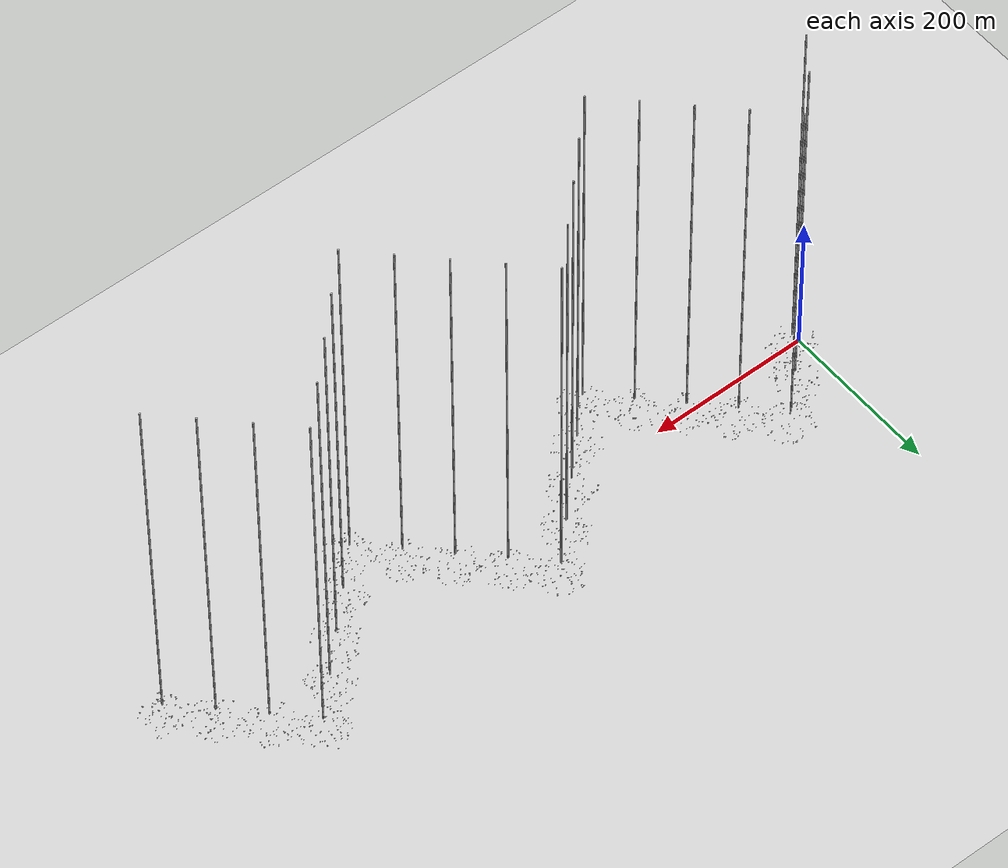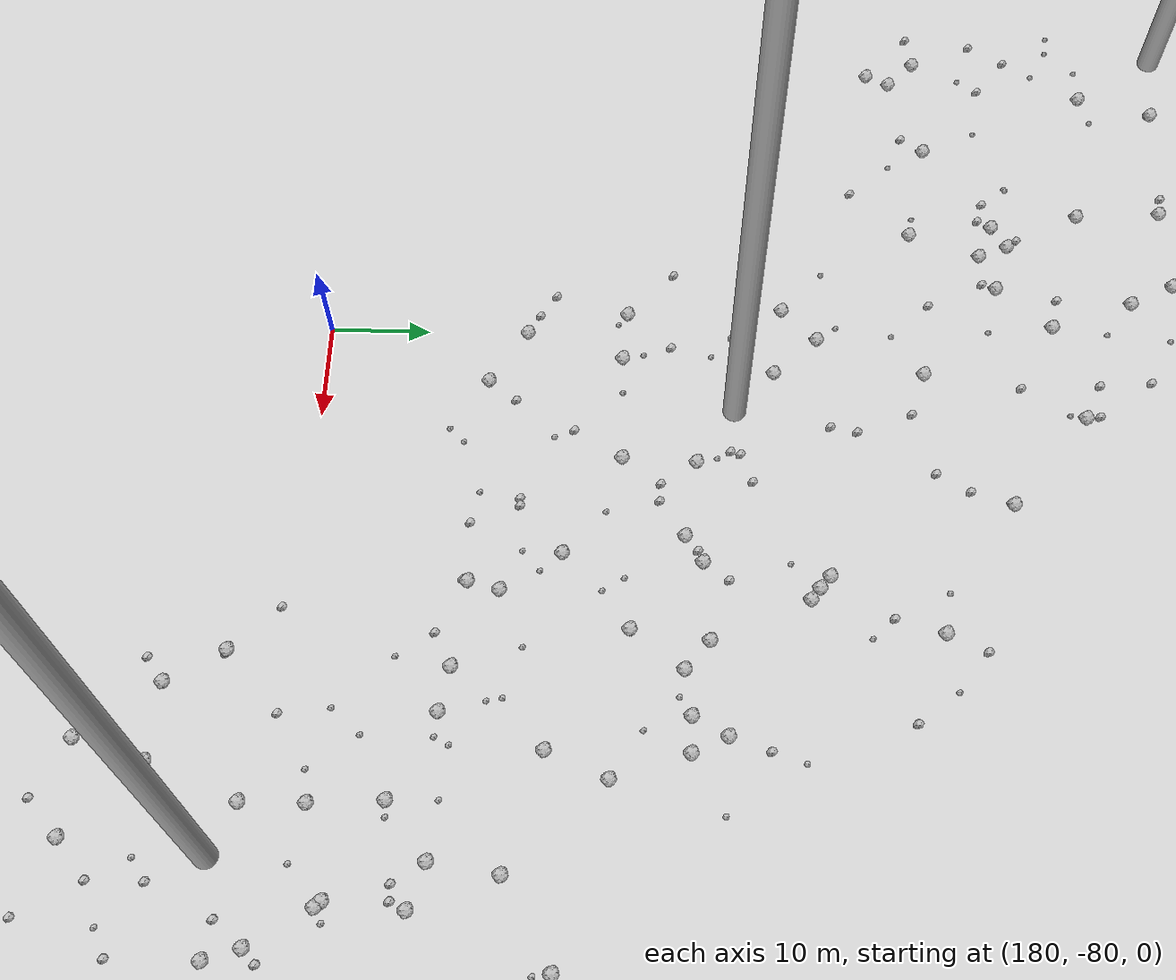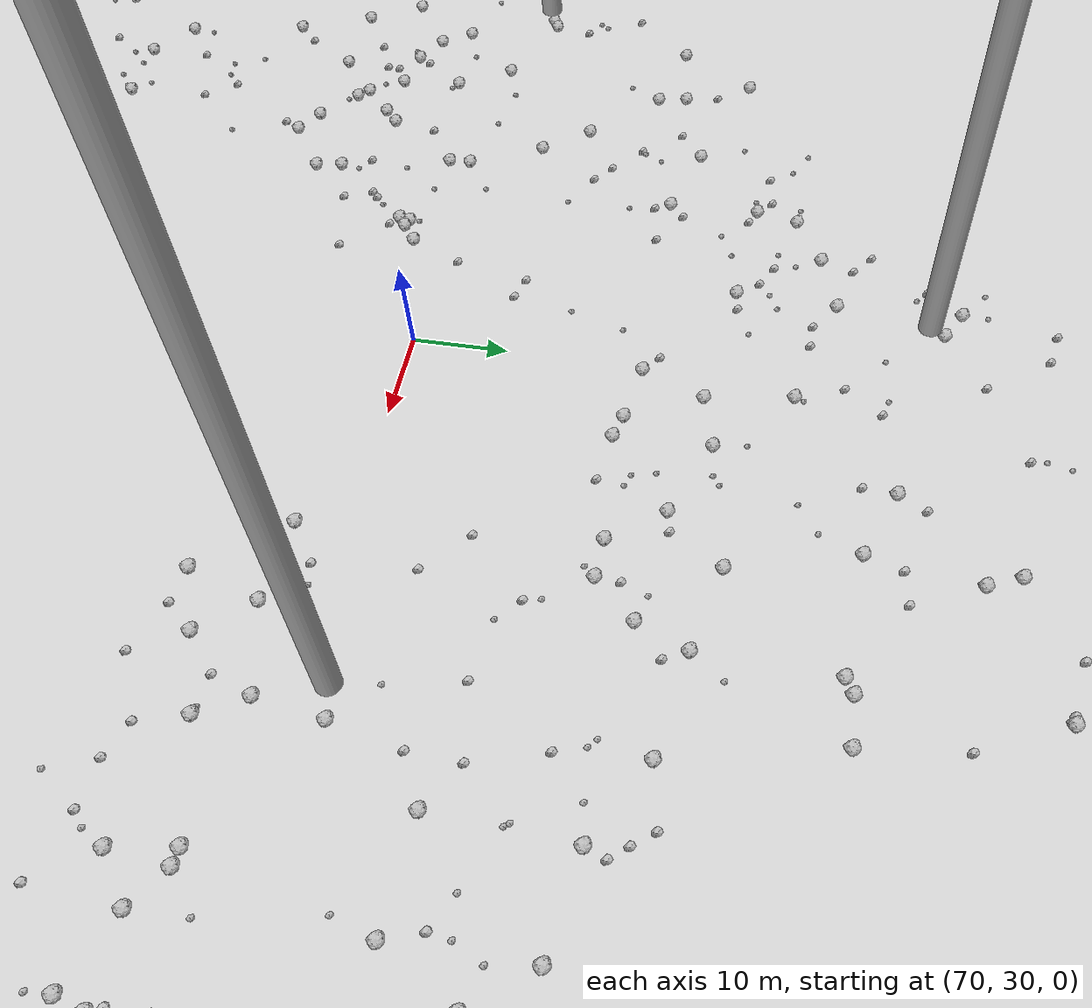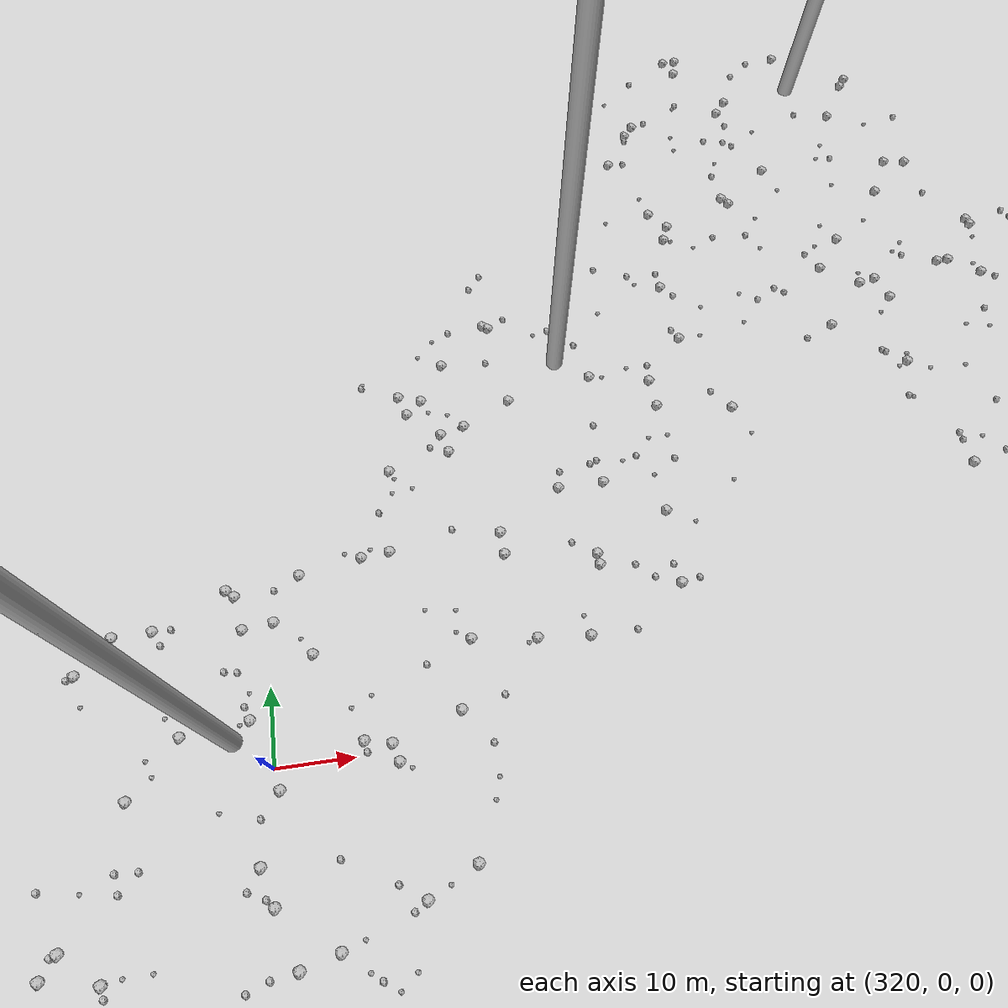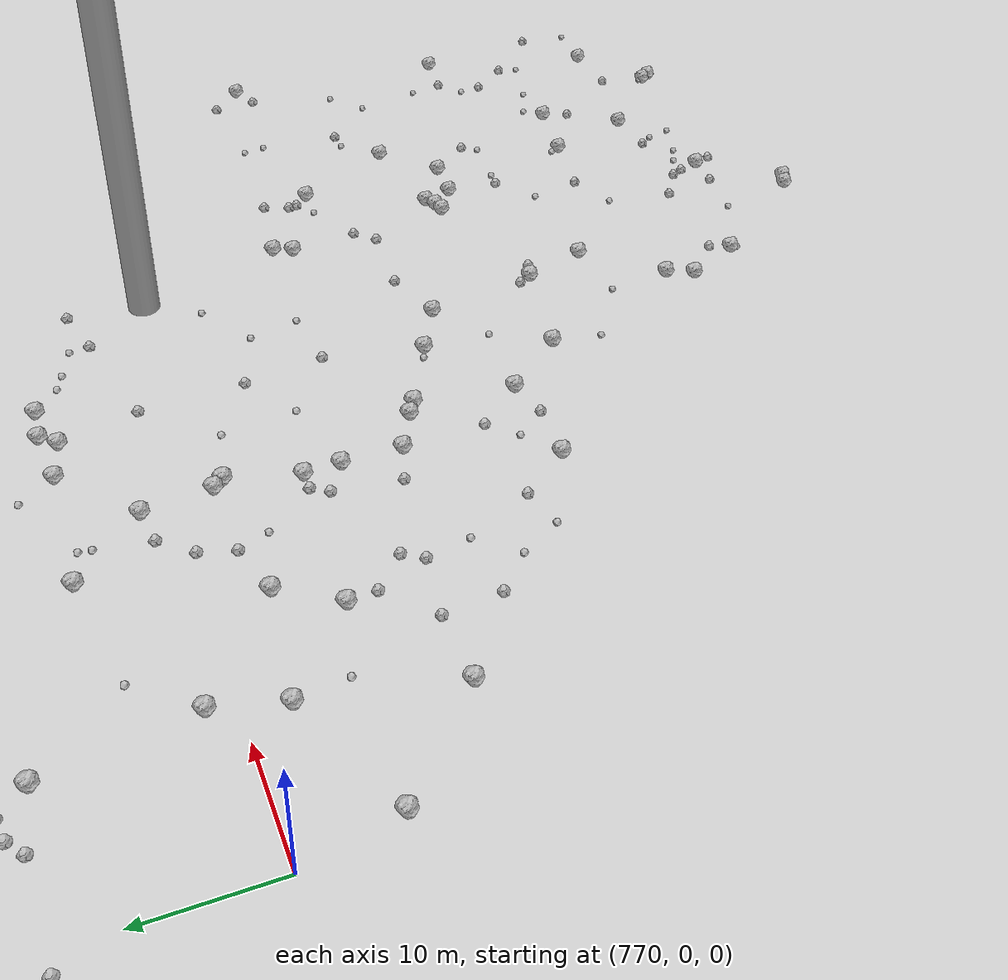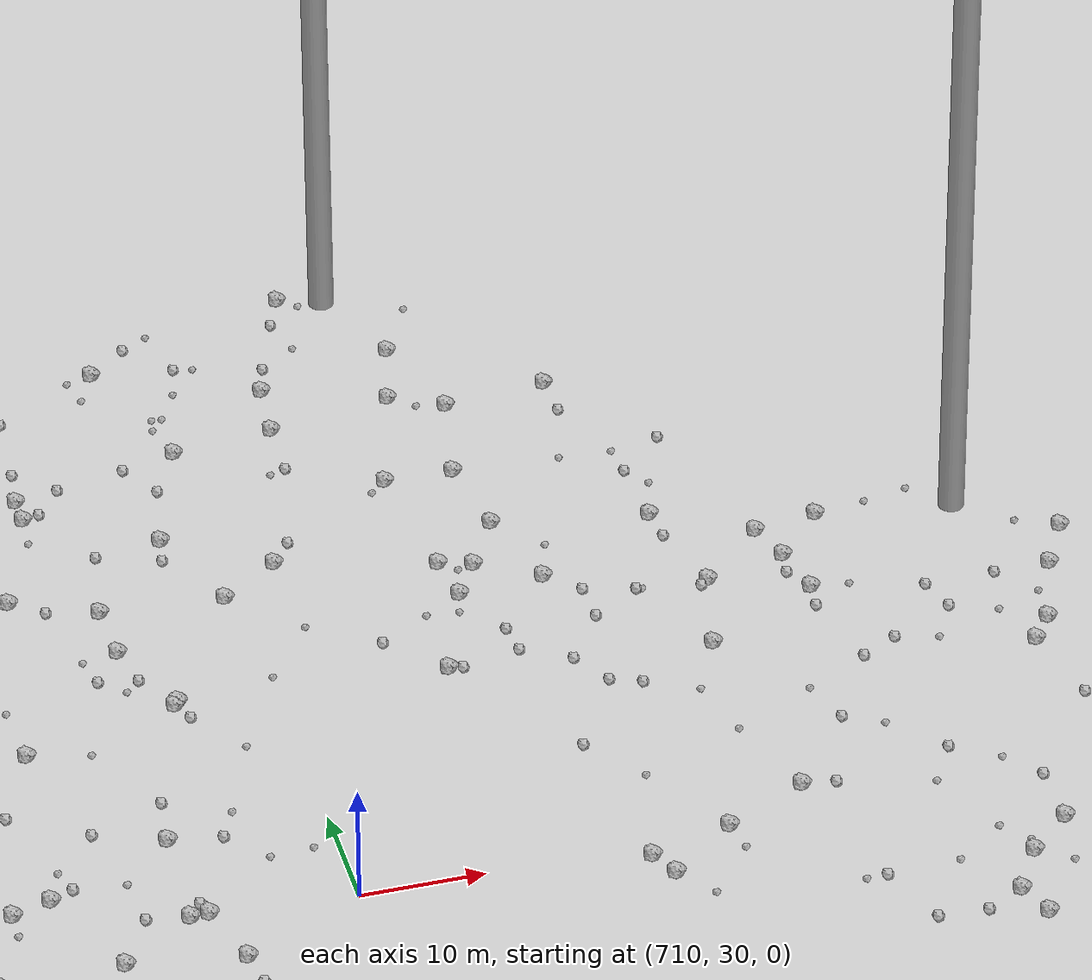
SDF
<sdf version="1.6">
 <world name="default">
  <include><uri>model://custom_ground</uri></include>
  <include><uri>model://sun</uri></include>
  <spherical_coordinates>
   <surface_model>EARTH_WGS84</surface_model>
   <latitude_deg>38.161479</latitude_deg>
   <longitude_deg>-122.454630</longitude_deg>
   <elevation>488.0</elevation>
   <heading_deg>90</heading_deg>
  </spherical_coordinates>
  <model name="rock1_0_0">
   <include><uri>model://rock1</uri><pose>-4.303871969672123 -7.698992740027663 0.5 0 0 0</pose></include>
  </model>
  <model name="rock1_0_1">
   <include><uri>model://rock1</uri><pose>5.9163128607475315 -17.05584468435616 0.5 0 0 0</pose></include>
  </model>
  <model name="rock1_0_2">
   <include><uri>model://rock1</uri><pose>9.714353764370642 -20.453960711691593 0.5 0 0 0</pose></include>
  </model>
  <model name="rock1_0_3">
   <include><uri>model://rock1</uri><pose>25.323442539957206 10.061556025729466 0.5 0 0 0</pose></include>
  </model>
  <model name="rock1_0_4">
   <include><uri>model://rock1</uri><pose>-2.310983132698393 19.217648858901462 0.5 0 0 0</pose></include>
  </model>
  <model name="rock1_0_5">
   <include><uri>model://rock1</uri><pose>26.554848240603846 -15.099107565912519 0.5 0 0 0</pose></include>
  </model>
  <model name="rock1_0_6">
   <include><uri>model://rock1</uri><pose>-17.71179040490471 2.993496011803977 0.5 0 0 0</pose></include>
  </model>
  <model name="rock1_0_7">
   <include><uri>model://rock1</uri><pose>35.8151594749186 9.527997872945114 0.5 0 0 0</pose></include>
  </model>
  <model name="rock1_0_8">
   <include><uri>model://rock1</uri><pose>34.68750626915344 -14.843394507315885 0.5 0 0 0</pose></include>
  </model>
  <model name="rock1_0_9">
   <include><uri>model://rock1</uri><pose>-5.272296925186534 10.536026966289093 0.5 0 0 0</pose></include>
  </model>
  <model name="rock1_0_10">
   <include><uri>model://rock1</uri><pose>15.958380754146937 -21.761986099890827 0.5 0 0 0</pose></include>
  </model>
  <model name="rock1_0_11">
   <include><uri>model://rock1</uri><pose>31.652774189917352 13.078066165233707 0.5 0 0 0</pose></include>
  </model>
  <model name="rock1_0_12">
   <include><uri>model://rock1</uri><pose>10.44710201669363 -13.554494029351826 0.5 0 0 0</pose></include>
  </model>
  <model name="rock1_0_13">
   <include><uri>model://rock1</uri><pose>18.989562190907293 2.0563418041743944 0.5 0 0 0</pose></include>
  </model>
  <model name="rock1_0_14">
   <include><uri>model://rock1</uri><pose>-19.85557977249265 0.45634263560155475 0.5 0 0 0</pose></include>
  </model>
  <model name="rock1_0_15">
   <include><uri>model://rock1</uri><pose>-14.357400732031294 6.374465759722149 0.5 0 0 0</pose></include>
  </model>
  <model name="rock1_0_16">
   <include><uri>model://rock1</uri><pose>15.723926547553333 10.230573015667979 0.5 0 0 0</pose></include>
  </model>
  <model name="rock1_0_17">
   <include><uri>model://rock1</uri><pose>23.05021433029861 18.67886218263866 0.5 0 0 0</pose></include>
  </model>
  <model name="rock1_0_18">
   <include><uri>model://rock1</uri><pose>-4.685007277369856 9.098412034277615 0.5 0 0 0</pose></include>
  </model>
  <model name="rock1_0_19">
   <include><uri>model://rock1</uri><pose>7.179717710703233 -0.8898872471285095 0.5 0 0 0</pose></include>
  </model>
  <model name="rock1_0_20">
   <include><uri>model://rock1</uri><pose>-11.01782244674398 14.607693531894498 0.5 0 0 0</pose></include>
  </model>
  <model name="rock1_0_21">
   <include><uri>model://rock1</uri><pose>5.618224780130859 13.695390029938679 0.5 0 0 0</pose></include>
  </model>
  <model name="rock1_0_22">
   <include><uri>model://rock1</uri><pose>21.529246710960876 -11.51920177784595 0.5 0 0 0</pose></include>
  </model>
  <model name="rock1_0_23">
   <include><uri>model://rock1</uri><pose>38.83185445872309 7.750444050828499 0.5 0 0 0</pose></include>
  </model>
  <model name="rock1_0_24">
   <include><uri>model://rock1</uri><pose>-5.828184617062986 17.375399389970475 0.5 0 0 0</pose></include>
  </model>
  <model name="rock1_0_25">
   <include><uri>model://rock1</uri><pose>12.311028002071843 16.19167625470226 0.5 0 0 0</pose></include>
  </model>
  <model name="rock1_0_26">
   <include><uri>model://rock1</uri><pose>30.485595033864826 14.196537078749898 0.5 0 0 0</pose></include>
  </model>
  <model name="rock2_0_0">
   <include><uri>model://rock2</uri><pose>-5.655811998859752 9.93881343701851 0.3 0 0 0</pose></include>
  </model>
  <model name="rock2_0_1">
   <include><uri>model://rock2</uri><pose>-0.9755510134310263 -7.25715896327387 0.3 0 0 0</pose></include>
  </model>
  <model name="rock2_0_2">
   <include><uri>model://rock2</uri><pose>0.03083017110095554 -5.164928305336886 0.3 0 0 0</pose></include>
  </model>
  <model name="rock2_0_3">
   <include><uri>model://rock2</uri><pose>1.712241048064982 -16.11732674553851 0.3 0 0 0</pose></include>
  </model>
  <model name="rock2_0_4">
   <include><uri>model://rock2</uri><pose>2.927546864962686 -26.992558756298074 0.3 0 0 0</pose></include>
  </model>
  <model name="rock2_0_5">
   <include><uri>model://rock2</uri><pose>-2.6371367697544343 -11.64593422712996 0.3 0 0 0</pose></include>
  </model>
  <model name="rock2_0_6">
   <include><uri>model://rock2</uri><pose>21.02024706593648 -12.086598903685115 0.3 0 0 0</pose></include>
  </model>
  <model name="rock2_0_7">
   <include><uri>model://rock2</uri><pose>34.085339655651715 -5.679567171977599 0.3 0 0 0</pose></include>
  </model>
  <model name="rock2_0_8">
   <include><uri>model://rock2</uri><pose>4.6623023242635 6.75378952803937 0.3 0 0 0</pose></include>
  </model>
  <model name="rock2_0_9">
   <include><uri>model://rock2</uri><pose>21.372282109192568 13.49369800263802 0.3 0 0 0</pose></include>
  </model>
  <model name="rock2_0_10">
   <include><uri>model://rock2</uri><pose>13.708496229354203 -14.761446469056924 0.3 0 0 0</pose></include>
  </model>
  <model name="rock2_0_11">
   <include><uri>model://rock2</uri><pose>31.543400338378163 -2.3849294221681987 0.3 0 0 0</pose></include>
  </model>
  <model name="rock2_0_12">
   <include><uri>model://rock2</uri><pose>-12.16851019745217 17.209461919084454 0.3 0 0 0</pose></include>
  </model>
  <model name="rock2_0_13">
   <include><uri>model://rock2</uri><pose>-13.930751791724463 -15.418076374050045 0.3 0 0 0</pose></include>
  </model>
  <model name="rock2_0_14">
   <include><uri>model://rock2</uri><pose>3.617569898033423 25.69160866633473 0.3 0 0 0</pose></include>
  </model>
  <model name="rock2_0_15">
   <include><uri>model://rock2</uri><pose>-1.8381047609254821 6.555805371337286 0.3 0 0 0</pose></include>
  </model>
  <model name="rock2_0_16">
   <include><uri>model://rock2</uri><pose>24.51289740735328 -20.607124132699482 0.3 0 0 0</pose></include>
  </model>
  <model name="rock2_0_17">
   <include><uri>model://rock2</uri><pose>21.348190991509917 4.36050356824699 0.3 0 0 0</pose></include>
  </model>
  <model name="rock2_0_18">
   <include><uri>model://rock2</uri><pose>26.36925290754175 -8.230324765752343 0.3 0 0 0</pose></include>
  </model>
  <model name="rock2_0_19">
   <include><uri>model://rock2</uri><pose>-10.510080638918776 -0.7402578987915689 0.3 0 0 0</pose></include>
  </model>
  <model name="rock2_0_20">
   <include><uri>model://rock2</uri><pose>-4.103801918513351 -16.64841727230168 0.3 0 0 0</pose></include>
  </model>
  <model name="rock2_0_21">
   <include><uri>model://rock2</uri><pose>-10.360204183837528 13.979679406997263 0.3 0 0 0</pose></include>
  </model>
  <model name="rock2_0_22">
   <include><uri>model://rock2</uri><pose>-15.539690756024537 4.122393624724587 0.3 0 0 0</pose></include>
  </model>
  <model name="rock2_0_23">
   <include><uri>model://rock2</uri><pose>-2.1790019161837826 15.960783996637467 0.3 0 0 0</pose></include>
  </model>
  <model name="rock2_0_24">
   <include><uri>model://rock2</uri><pose>25.345435932296013 15.163115612763264 0.3 0 0 0</pose></include>
  </model>
  <model name="rock2_0_25">
   <include><uri>model://rock2</uri><pose>37.642726219892516 5.858644933942259 0.3 0 0 0</pose></include>
  </model>
  <model name="rock2_0_26">
   <include><uri>model://rock2</uri><pose>8.332791691693327 12.89409538920576 0.3 0 0 0</pose></include>
  </model>
  <model name="rock3_0_0">
   <include><uri>model://rock3</uri><pose>39.89255488215653 -0.24820263026142442 0.2 0 0 0</pose></include>
  </model>
  <model name="rock3_0_1">
   <include><uri>model://rock3</uri><pose>5.988484403392761 -11.909132262702563 0.2 0 0 0</pose></include>
  </model>
  <model name="rock3_0_2">
   <include><uri>model://rock3</uri><pose>16.5092301580449 -24.475595365562192 0.2 0 0 0</pose></include>
  </model>
  <model name="rock3_0_3">
   <include><uri>model://rock3</uri><pose>3.6301770657339887 -10.189726246160859 0.2 0 0 0</pose></include>
  </model>
  <model name="rock3_0_4">
   <include><uri>model://rock3</uri><pose>28.541456815868358 15.643446905492944 0.2 0 0 0</pose></include>
  </model>
  <model name="rock3_0_5">
   <include><uri>model://rock3</uri><pose>-15.653801268579745 11.504093667288316 0.2 0 0 0</pose></include>
  </model>
  <model name="rock3_0_6">
   <include><uri>model://rock3</uri><pose>33.58253191240175 -15.901977277466866 0.2 0 0 0</pose></include>
  </model>
  <model name="rock3_0_7">
   <include><uri>model://rock3</uri><pose>31.6111042879848 -17.268559225382038 0.2 0 0 0</pose></include>
  </model>
  <model name="rock3_0_8">
   <include><uri>model://rock3</uri><pose>10.325192344437866 -6.149578795458158 0.2 0 0 0</pose></include>
  </model>
  <model name="rock3_0_9">
   <include><uri>model://rock3</uri><pose>1.1406888747348596 -6.9703985766711405 0.2 0 0 0</pose></include>
  </model>
  <model name="rock3_0_10">
   <include><uri>model://rock3</uri><pose>10.728649184169115 -20.991830837744452 0.2 0 0 0</pose></include>
  </model>
  <model name="rock3_0_11">
   <include><uri>model://rock3</uri><pose>28.946644581388867 -15.664091199755841 0.2 0 0 0</pose></include>
  </model>
  <model name="rock3_0_12">
   <include><uri>model://rock3</uri><pose>25.946641069258185 -0.771211299692812 0.2 0 0 0</pose></include>
  </model>
  <model name="rock3_0_13">
   <include><uri>model://rock3</uri><pose>-1.1920655094794128 9.275754589246972 0.2 0 0 0</pose></include>
  </model>
  <model name="rock3_0_14">
   <include><uri>model://rock3</uri><pose>32.671087132380265 -13.168598115012358 0.2 0 0 0</pose></include>
  </model>
  <model name="rock3_0_15">
   <include><uri>model://rock3</uri><pose>-7.56625136347216 -24.20669069599557 0.2 0 0 0</pose></include>
  </model>
  <model name="rock3_0_16">
   <include><uri>model://rock3</uri><pose>-15.792928950025427 6.727639650073144 0.2 0 0 0</pose></include>
  </model>
  <model name="rock3_0_17">
   <include><uri>model://rock3</uri><pose>26.92587684873091 -17.540564078538065 0.2 0 0 0</pose></include>
  </model>
  <model name="rock3_0_18">
   <include><uri>model://rock3</uri><pose>9.39214569548319 26.064679605533456 0.2 0 0 0</pose></include>
  </model>
  <model name="rock3_0_19">
   <include><uri>model://rock3</uri><pose>21.43795891576385 -9.096895283749266 0.2 0 0 0</pose></include>
  </model>
  <model name="rock3_0_20">
   <include><uri>model://rock3</uri><pose>12.031886978355622 -14.500060407194276 0.2 0 0 0</pose></include>
  </model>
  <model name="rock3_0_21">
   <include><uri>model://rock3</uri><pose>27.39531438306524 -4.233882482069532 0.2 0 0 0</pose></include>
  </model>
  <model name="rock3_0_22">
   <include><uri>model://rock3</uri><pose>21.38706861502709 17.805720499040262 0.2 0 0 0</pose></include>
  </model>
  <model name="rock3_0_23">
   <include><uri>model://rock3</uri><pose>29.619355541055356 -3.9952876112397853 0.2 0 0 0</pose></include>
  </model>
  <model name="rock3_0_24">
   <include><uri>model://rock3</uri><pose>-7.257727567648706 11.202699525146429 0.2 0 0 0</pose></include>
  </model>
  <model name="rock3_0_25">
   <include><uri>model://rock3</uri><pose>4.533769685980193 5.720509927760148 0.2 0 0 0</pose></include>
  </model>
  <model name="rock3_0_26">
   <include><uri>model://rock3</uri><pose>32.1181871124365 11.996697015910229 0.2 0 0 0</pose></include>
  </model>
  <model name="rock1_1_0">
   <include><uri>model://rock1</uri><pose>22.921612868691874 60.29186176499788 0.5 0 0 0</pose></include>
  </model>
  <model name="rock1_1_1">
   <include><uri>model://rock1</uri><pose>52.56383638180793 25.02749303017453 0.5 0 0 0</pose></include>
  </model>
  <model name="rock1_1_2">
   <include><uri>model://rock1</uri><pose>45.313884617668 63.471779960463465 0.5 0 0 0</pose></include>
  </model>
  <model name="rock1_1_3">
   <include><uri>model://rock1</uri><pose>36.730946657132925 55.98695569431955 0.5 0 0 0</pose></include>
  </model>
  <model name="rock1_1_4">
   <include><uri>model://rock1</uri><pose>52.268629072042515 23.769372915079003 0.5 0 0 0</pose></include>
  </model>
  <model name="rock1_1_5">
   <include><uri>model://rock1</uri><pose>41.84596382787835 27.02178113237606 0.5 0 0 0</pose></include>
  </model>
  <model name="rock1_1_6">
   <include><uri>model://rock1</uri><pose>19.32994050248936 20.65063778719255 0.5 0 0 0</pose></include>
  </model>
  <model name="rock1_1_7">
   <include><uri>model://rock1</uri><pose>23.9685587179722 30.551848628693172 0.5 0 0 0</pose></include>
  </model>
  <model name="rock1_1_8">
   <include><uri>model://rock1</uri><pose>33.980348245512225 17.32679540044675 0.5 0 0 0</pose></include>
  </model>
  <model name="rock1_1_9">
   <include><uri>model://rock1</uri><pose>17.14100681935943 23.972357871719936 0.5 0 0 0</pose></include>
  </model>
  <model name="rock1_1_10">
   <include><uri>model://rock1</uri><pose>44.43241970298878 14.744546799657464 0.5 0 0 0</pose></include>
  </model>
  <model name="rock1_1_11">
   <include><uri>model://rock1</uri><pose>27.452227159329016 24.73307485592899 0.5 0 0 0</pose></include>
  </model>
  <model name="rock1_1_12">
   <include><uri>model://rock1</uri><pose>45.49006082330123 53.63777586934096 0.5 0 0 0</pose></include>
  </model>
  <model name="rock1_1_13">
   <include><uri>model://rock1</uri><pose>35.78479207821705 18.90838403349118 0.5 0 0 0</pose></include>
  </model>
  <model name="rock1_1_14">
   <include><uri>model://rock1</uri><pose>46.33631449755555 68.03199273142857 0.5 0 0 0</pose></include>
  </model>
  <model name="rock1_1_15">
   <include><uri>model://rock1</uri><pose>12.795183145342916 33.913378156761475 0.5 0 0 0</pose></include>
  </model>
  <model name="rock1_1_16">
   <include><uri>model://rock1</uri><pose>44.893139324490335 11.834196167737359 0.5 0 0 0</pose></include>
  </model>
  <model name="rock1_1_17">
   <include><uri>model://rock1</uri><pose>13.944200685052607 34.534786213249035 0.5 0 0 0</pose></include>
  </model>
  <model name="rock1_1_18">
   <include><uri>model://rock1</uri><pose>28.100570504550554 17.934491440601345 0.5 0 0 0</pose></include>
  </model>
  <model name="rock1_1_19">
   <include><uri>model://rock1</uri><pose>26.30813321713418 52.89402071228179 0.5 0 0 0</pose></include>
  </model>
  <model name="rock1_1_20">
   <include><uri>model://rock1</uri><pose>17.575270616261058 51.71870273276556 0.5 0 0 0</pose></include>
  </model>
  <model name="rock1_1_21">
   <include><uri>model://rock1</uri><pose>26.882987588393824 49.592061735684915 0.5 0 0 0</pose></include>
  </model>
  <model name="rock1_1_22">
   <include><uri>model://rock1</uri><pose>55.57122700504919 26.247155457091896 0.5 0 0 0</pose></include>
  </model>
  <model name="rock1_1_23">
   <include><uri>model://rock1</uri><pose>41.745872653648256 29.43196067853911 0.5 0 0 0</pose></include>
  </model>
  <model name="rock1_1_24">
   <include><uri>model://rock1</uri><pose>34.19127513844908 42.36488052440308 0.5 0 0 0</pose></include>
  </model>
  <model name="rock1_1_25">
   <include><uri>model://rock1</uri><pose>53.4802418112752 24.69336094672176 0.5 0 0 0</pose></include>
  </model>
  <model name="rock1_1_26">
   <include><uri>model://rock1</uri><pose>38.04596981036256 37.33875399161561 0.5 0 0 0</pose></include>
  </model>
  <model name="rock2_1_0">
   <include><uri>model://rock2</uri><pose>59.79794843018846 39.85399718872391 0.3 0 0 0</pose></include>
  </model>
  <model name="rock2_1_1">
   <include><uri>model://rock2</uri><pose>40.17252960006513 46.059607781055625 0.3 0 0 0</pose></include>
  </model>
  <model name="rock2_1_2">
   <include><uri>model://rock2</uri><pose>11.219226296102276 45.09597999240529 0.3 0 0 0</pose></include>
  </model>
  <model name="rock2_1_3">
   <include><uri>model://rock2</uri><pose>62.401641851300006 39.10994027422201 0.3 0 0 0</pose></include>
  </model>
  <model name="rock2_1_4">
   <include><uri>model://rock2</uri><pose>36.64288093190181 49.095493904509944 0.3 0 0 0</pose></include>
  </model>
  <model name="rock2_1_5">
   <include><uri>model://rock2</uri><pose>25.483467469570435 56.667692581099125 0.3 0 0 0</pose></include>
  </model>
  <model name="rock2_1_6">
   <include><uri>model://rock2</uri><pose>39.548077178868944 64.44300358849448 0.3 0 0 0</pose></include>
  </model>
  <model name="rock2_1_7">
   <include><uri>model://rock2</uri><pose>56.571394387937765 64.85298130540124 0.3 0 0 0</pose></include>
  </model>
  <model name="rock2_1_8">
   <include><uri>model://rock2</uri><pose>51.348741099459225 52.82944056609096 0.3 0 0 0</pose></include>
  </model>
  <model name="rock2_1_9">
   <include><uri>model://rock2</uri><pose>46.27723873368315 51.930810484402826 0.3 0 0 0</pose></include>
  </model>
  <model name="rock2_1_10">
   <include><uri>model://rock2</uri><pose>23.789796731762536 20.109855768025522 0.3 0 0 0</pose></include>
  </model>
  <model name="rock2_1_11">
   <include><uri>model://rock2</uri><pose>53.98734884018728 66.17195174066316 0.3 0 0 0</pose></include>
  </model>
  <model name="rock2_1_12">
   <include><uri>model://rock2</uri><pose>49.58412445254992 16.514782423653216 0.3 0 0 0</pose></include>
  </model>
  <model name="rock2_1_13">
   <include><uri>model://rock2</uri><pose>48.389631150054875 19.591057781406697 0.3 0 0 0</pose></include>
  </model>
  <model name="rock2_1_14">
   <include><uri>model://rock2</uri><pose>57.42144911060968 18.2878538180425 0.3 0 0 0</pose></include>
  </model>
  <model name="rock2_1_15">
   <include><uri>model://rock2</uri><pose>25.412281930796922 16.59970522045472 0.3 0 0 0</pose></include>
  </model>
  <model name="rock2_1_16">
   <include><uri>model://rock2</uri><pose>47.20144621370575 55.28074007285215 0.3 0 0 0</pose></include>
  </model>
  <model name="rock2_1_17">
   <include><uri>model://rock2</uri><pose>46.98993506327635 62.69255203469109 0.3 0 0 0</pose></include>
  </model>
  <model name="rock2_1_18">
   <include><uri>model://rock2</uri><pose>33.138671232775195 53.33308888812556 0.3 0 0 0</pose></include>
  </model>
  <model name="rock2_1_19">
   <include><uri>model://rock2</uri><pose>42.99802558276047 18.00834380320697 0.3 0 0 0</pose></include>
  </model>
  <model name="rock2_1_20">
   <include><uri>model://rock2</uri><pose>43.55103015771908 65.00339227922716 0.3 0 0 0</pose></include>
  </model>
  <model name="rock2_1_21">
   <include><uri>model://rock2</uri><pose>14.544569014823253 38.77469084554224 0.3 0 0 0</pose></include>
  </model>
  <model name="rock2_1_22">
   <include><uri>model://rock2</uri><pose>36.63392422917157 23.8375928787686 0.3 0 0 0</pose></include>
  </model>
  <model name="rock2_1_23">
   <include><uri>model://rock2</uri><pose>49.22684090538941 20.362427550493116 0.3 0 0 0</pose></include>
  </model>
  <model name="rock2_1_24">
   <include><uri>model://rock2</uri><pose>53.29550762394143 22.89431794725416 0.3 0 0 0</pose></include>
  </model>
  <model name="rock2_1_25">
   <include><uri>model://rock2</uri><pose>42.38815966052128 44.28969742846621 0.3 0 0 0</pose></include>
  </model>
  <model name="rock2_1_26">
   <include><uri>model://rock2</uri><pose>58.11999642322637 31.888896230452993 0.3 0 0 0</pose></include>
  </model>
  <model name="rock3_1_0">
   <include><uri>model://rock3</uri><pose>28.039554199465883 23.96978295838837 0.2 0 0 0</pose></include>
  </model>
  <model name="rock3_1_1">
   <include><uri>model://rock3</uri><pose>24.712423056216885 45.988746117362055 0.2 0 0 0</pose></include>
  </model>
  <model name="rock3_1_2">
   <include><uri>model://rock3</uri><pose>44.48012756258646 16.76061189556127 0.2 0 0 0</pose></include>
  </model>
  <model name="rock3_1_3">
   <include><uri>model://rock3</uri><pose>33.96873986786659 31.09715027762949 0.2 0 0 0</pose></include>
  </model>
  <model name="rock3_1_4">
   <include><uri>model://rock3</uri><pose>51.62182601969161 66.43616842233811 0.2 0 0 0</pose></include>
  </model>
  <model name="rock3_1_5">
   <include><uri>model://rock3</uri><pose>65.353500123358 51.369308690935256 0.2 0 0 0</pose></include>
  </model>
  <model name="rock3_1_6">
   <include><uri>model://rock3</uri><pose>21.3983960498474 25.469071036407833 0.2 0 0 0</pose></include>
  </model>
  <model name="rock3_1_7">
   <include><uri>model://rock3</uri><pose>49.54927172352766 59.89942428234097 0.2 0 0 0</pose></include>
  </model>
  <model name="rock3_1_8">
   <include><uri>model://rock3</uri><pose>12.22568683617283 40.015238545899386 0.2 0 0 0</pose></include>
  </model>
  <model name="rock3_1_9">
   <include><uri>model://rock3</uri><pose>34.622809071384815 68.44071748706935 0.2 0 0 0</pose></include>
  </model>
  <model name="rock3_1_10">
   <include><uri>model://rock3</uri><pose>45.80005283039516 32.22324887542937 0.2 0 0 0</pose></include>
  </model>
  <model name="rock3_1_11">
   <include><uri>model://rock3</uri><pose>44.10448733569322 68.29584871999937 0.2 0 0 0</pose></include>
  </model>
  <model name="rock3_1_12">
   <include><uri>model://rock3</uri><pose>63.48996132728982 45.49659625639434 0.2 0 0 0</pose></include>
  </model>
  <model name="rock3_1_13">
   <include><uri>model://rock3</uri><pose>52.50090581604991 61.35964746468433 0.2 0 0 0</pose></include>
  </model>
  <model name="rock3_1_14">
   <include><uri>model://rock3</uri><pose>43.38825584588673 63.20152646809601 0.2 0 0 0</pose></include>
  </model>
  <model name="rock3_1_15">
   <include><uri>model://rock3</uri><pose>36.88960001908891 49.48118118339011 0.2 0 0 0</pose></include>
  </model>
  <model name="rock3_1_16">
   <include><uri>model://rock3</uri><pose>50.14370225867343 21.229832743693564 0.2 0 0 0</pose></include>
  </model>
  <model name="rock3_1_17">
   <include><uri>model://rock3</uri><pose>46.52009791340836 41.93224687195433 0.2 0 0 0</pose></include>
  </model>
  <model name="rock3_1_18">
   <include><uri>model://rock3</uri><pose>52.209512100103375 26.010779486442267 0.2 0 0 0</pose></include>
  </model>
  <model name="rock3_1_19">
   <include><uri>model://rock3</uri><pose>46.478335813453995 49.06994915912022 0.2 0 0 0</pose></include>
  </model>
  <model name="rock3_1_20">
   <include><uri>model://rock3</uri><pose>34.58663905540214 60.92848456005657 0.2 0 0 0</pose></include>
  </model>
  <model name="rock3_1_21">
   <include><uri>model://rock3</uri><pose>43.511370975444656 22.290502564996224 0.2 0 0 0</pose></include>
  </model>
  <model name="rock3_1_22">
   <include><uri>model://rock3</uri><pose>37.725910809796616 66.91479663499729 0.2 0 0 0</pose></include>
  </model>
  <model name="rock3_1_23">
   <include><uri>model://rock3</uri><pose>37.94728972995647 51.46583268322339 0.2 0 0 0</pose></include>
  </model>
  <model name="rock3_1_24">
   <include><uri>model://rock3</uri><pose>12.917580110680438 40.9422409831521 0.2 0 0 0</pose></include>
  </model>
  <model name="rock3_1_25">
   <include><uri>model://rock3</uri><pose>46.66781189840566 26.374863271542925 0.2 0 0 0</pose></include>
  </model>
  <model name="rock3_1_26">
   <include><uri>model://rock3</uri><pose>28.240707651820852 31.989467863082872 0.2 0 0 0</pose></include>
  </model>
  <model name="rock1_2_0">
   <include><uri>model://rock1</uri><pose>92.00562664475834 104.10915995487458 0.5 0 0 0</pose></include>
  </model>
  <model name="rock1_2_1">
   <include><uri>model://rock1</uri><pose>109.74280751378255 77.80934807196167 0.5 0 0 0</pose></include>
  </model>
  <model name="rock1_2_2">
   <include><uri>model://rock1</uri><pose>72.14384957392245 69.8855392732979 0.5 0 0 0</pose></include>
  </model>
  <model name="rock1_2_3">
   <include><uri>model://rock1</uri><pose>62.00621393435494 102.17938696844242 0.5 0 0 0</pose></include>
  </model>
  <model name="rock1_2_4">
   <include><uri>model://rock1</uri><pose>90.50395173951784 92.19181973718426 0.5 0 0 0</pose></include>
  </model>
  <model name="rock1_2_5">
   <include><uri>model://rock1</uri><pose>102.6436467464437 63.23966057544421 0.5 0 0 0</pose></include>
  </model>
  <model name="rock1_2_6">
   <include><uri>model://rock1</uri><pose>62.831067449591075 101.62211767530388 0.5 0 0 0</pose></include>
  </model>
  <model name="rock1_2_7">
   <include><uri>model://rock1</uri><pose>58.37808884081396 62.536244087946315 0.5 0 0 0</pose></include>
  </model>
  <model name="rock1_2_8">
   <include><uri>model://rock1</uri><pose>77.19972109806979 53.30149618322895 0.5 0 0 0</pose></include>
  </model>
  <model name="rock1_2_9">
   <include><uri>model://rock1</uri><pose>104.74785495256006 77.65413986136394 0.5 0 0 0</pose></include>
  </model>
  <model name="rock1_2_10">
   <include><uri>model://rock1</uri><pose>58.81187107370224 73.28254225566043 0.5 0 0 0</pose></include>
  </model>
  <model name="rock1_2_11">
   <include><uri>model://rock1</uri><pose>52.05116778714124 71.1459926960683 0.5 0 0 0</pose></include>
  </model>
  <model name="rock1_2_12">
   <include><uri>model://rock1</uri><pose>73.57991184996592 60.878096425345156 0.5 0 0 0</pose></include>
  </model>
  <model name="rock1_2_13">
   <include><uri>model://rock1</uri><pose>92.08545716762737 53.89094113653944 0.5 0 0 0</pose></include>
  </model>
  <model name="rock1_2_14">
   <include><uri>model://rock1</uri><pose>81.68340091740215 102.7212780190823 0.5 0 0 0</pose></include>
  </model>
  <model name="rock1_2_15">
   <include><uri>model://rock1</uri><pose>79.82605780046893 52.62766639389256 0.5 0 0 0</pose></include>
  </model>
  <model name="rock1_2_16">
   <include><uri>model://rock1</uri><pose>88.04206772897075 59.24325172283454 0.5 0 0 0</pose></include>
  </model>
  <model name="rock1_2_17">
   <include><uri>model://rock1</uri><pose>91.93336717577941 88.85427558546299 0.5 0 0 0</pose></include>
  </model>
  <model name="rock1_2_18">
   <include><uri>model://rock1</uri><pose>61.40899662395632 84.68971297351455 0.5 0 0 0</pose></include>
  </model>
  <model name="rock1_2_19">
   <include><uri>model://rock1</uri><pose>103.18113947376638 76.81254769036892 0.5 0 0 0</pose></include>
  </model>
  <model name="rock1_2_20">
   <include><uri>model://rock1</uri><pose>90.19105523705184 77.6866047370842 0.5 0 0 0</pose></include>
  </model>
  <model name="rock1_2_21">
   <include><uri>model://rock1</uri><pose>79.58534420488891 62.51093209609058 0.5 0 0 0</pose></include>
  </model>
  <model name="rock1_2_22">
   <include><uri>model://rock1</uri><pose>70.79274217887578 54.237528881656075 0.5 0 0 0</pose></include>
  </model>
  <model name="rock1_2_23">
   <include><uri>model://rock1</uri><pose>82.75906609703365 80.55750139504116 0.5 0 0 0</pose></include>
  </model>
  <model name="rock1_2_24">
   <include><uri>model://rock1</uri><pose>58.15009463297866 86.46277681435785 0.5 0 0 0</pose></include>
  </model>
  <model name="rock1_2_25">
   <include><uri>model://rock1</uri><pose>93.5867146216581 65.15705432121904 0.5 0 0 0</pose></include>
  </model>
  <model name="rock1_2_26">
   <include><uri>model://rock1</uri><pose>104.75686472507434 96.21477133331508 0.5 0 0 0</pose></include>
  </model>
  <model name="rock2_2_0">
   <include><uri>model://rock2</uri><pose>108.59532874554984 87.77977131479324 0.3 0 0 0</pose></include>
  </model>
  <model name="rock2_2_1">
   <include><uri>model://rock2</uri><pose>63.41313637316618 95.5171260239182 0.3 0 0 0</pose></include>
  </model>
  <model name="rock2_2_2">
   <include><uri>model://rock2</uri><pose>98.43195176185824 97.40923168681596 0.3 0 0 0</pose></include>
  </model>
  <model name="rock2_2_3">
   <include><uri>model://rock2</uri><pose>59.77927556344557 96.31645109611514 0.3 0 0 0</pose></include>
  </model>
  <model name="rock2_2_4">
   <include><uri>model://rock2</uri><pose>91.53501295897429 105.1781986052386 0.3 0 0 0</pose></include>
  </model>
  <model name="rock2_2_5">
   <include><uri>model://rock2</uri><pose>67.99396623084873 89.01230265231493 0.3 0 0 0</pose></include>
  </model>
  <model name="rock2_2_6">
   <include><uri>model://rock2</uri><pose>83.93915907716513 103.9999725268685 0.3 0 0 0</pose></include>
  </model>
  <model name="rock2_2_7">
   <include><uri>model://rock2</uri><pose>60.66618052177785 62.898025623236784 0.3 0 0 0</pose></include>
  </model>
  <model name="rock2_2_8">
   <include><uri>model://rock2</uri><pose>90.2979737118541 59.76878239704248 0.3 0 0 0</pose></include>
  </model>
  <model name="rock2_2_9">
   <include><uri>model://rock2</uri><pose>52.77377986579824 83.85333974323757 0.3 0 0 0</pose></include>
  </model>
  <model name="rock2_2_10">
   <include><uri>model://rock2</uri><pose>91.37680956663425 81.52701801336481 0.3 0 0 0</pose></include>
  </model>
  <model name="rock2_2_11">
   <include><uri>model://rock2</uri><pose>68.81434442696099 55.77334352924788 0.3 0 0 0</pose></include>
  </model>
  <model name="rock2_2_12">
   <include><uri>model://rock2</uri><pose>82.45420521331764 77.20475572657818 0.3 0 0 0</pose></include>
  </model>
  <model name="rock2_2_13">
   <include><uri>model://rock2</uri><pose>103.92579929502995 96.29039494190675 0.3 0 0 0</pose></include>
  </model>
  <model name="rock2_2_14">
   <include><uri>model://rock2</uri><pose>73.09462869956535 78.75971268402648 0.3 0 0 0</pose></include>
  </model>
  <model name="rock2_2_15">
   <include><uri>model://rock2</uri><pose>53.179648722287006 74.72180086196863 0.3 0 0 0</pose></include>
  </model>
  <model name="rock2_2_16">
   <include><uri>model://rock2</uri><pose>84.30791328816989 83.44838762114857 0.3 0 0 0</pose></include>
  </model>
  <model name="rock2_2_17">
   <include><uri>model://rock2</uri><pose>94.06568854647054 102.4743061594136 0.3 0 0 0</pose></include>
  </model>
  <model name="rock2_2_18">
   <include><uri>model://rock2</uri><pose>94.97080474065532 82.0867080594739 0.3 0 0 0</pose></include>
  </model>
  <model name="rock2_2_19">
   <include><uri>model://rock2</uri><pose>64.84467602048093 70.94076304249037 0.3 0 0 0</pose></include>
  </model>
  <model name="rock2_2_20">
   <include><uri>model://rock2</uri><pose>55.26614339097007 82.7212853601807 0.3 0 0 0</pose></include>
  </model>
  <model name="rock2_2_21">
   <include><uri>model://rock2</uri><pose>85.27982742205877 51.99172412133599 0.3 0 0 0</pose></include>
  </model>
  <model name="rock2_2_22">
   <include><uri>model://rock2</uri><pose>50.85458410937565 76.58162214954146 0.3 0 0 0</pose></include>
  </model>
  <model name="rock2_2_23">
   <include><uri>model://rock2</uri><pose>96.42991262131349 56.20049095056997 0.3 0 0 0</pose></include>
  </model>
  <model name="rock2_2_24">
   <include><uri>model://rock2</uri><pose>62.07168417574305 70.9956978772186 0.3 0 0 0</pose></include>
  </model>
  <model name="rock2_2_25">
   <include><uri>model://rock2</uri><pose>70.22539704804711 74.83654454342542 0.3 0 0 0</pose></include>
  </model>
  <model name="rock2_2_26">
   <include><uri>model://rock2</uri><pose>76.89493761769225 93.18862115295613 0.3 0 0 0</pose></include>
  </model>
  <model name="rock3_2_0">
   <include><uri>model://rock3</uri><pose>73.77598721010526 100.388333937248 0.2 0 0 0</pose></include>
  </model>
  <model name="rock3_2_1">
   <include><uri>model://rock3</uri><pose>85.49878981873297 54.665055243672334 0.2 0 0 0</pose></include>
  </model>
  <model name="rock3_2_2">
   <include><uri>model://rock3</uri><pose>84.1055527964944 63.7017362145862 0.2 0 0 0</pose></include>
  </model>
  <model name="rock3_2_3">
   <include><uri>model://rock3</uri><pose>104.99969219078035 66.59512088879106 0.2 0 0 0</pose></include>
  </model>
  <model name="rock3_2_4">
   <include><uri>model://rock3</uri><pose>83.57347877480981 57.54977471619151 0.2 0 0 0</pose></include>
  </model>
  <model name="rock3_2_5">
   <include><uri>model://rock3</uri><pose>72.31331884702567 70.85150530287329 0.2 0 0 0</pose></include>
  </model>
  <model name="rock3_2_6">
   <include><uri>model://rock3</uri><pose>65.73429237977652 78.78759800275131 0.2 0 0 0</pose></include>
  </model>
  <model name="rock3_2_7">
   <include><uri>model://rock3</uri><pose>53.179373979326556 68.47666232887087 0.2 0 0 0</pose></include>
  </model>
  <model name="rock3_2_8">
   <include><uri>model://rock3</uri><pose>83.06066294499334 62.963090010467894 0.2 0 0 0</pose></include>
  </model>
  <model name="rock3_2_9">
   <include><uri>model://rock3</uri><pose>89.56974177962357 102.96063787042036 0.2 0 0 0</pose></include>
  </model>
  <model name="rock3_2_10">
   <include><uri>model://rock3</uri><pose>57.967458634074276 89.23123982114181 0.2 0 0 0</pose></include>
  </model>
  <model name="rock3_2_11">
   <include><uri>model://rock3</uri><pose>76.56803444486164 94.79108682256233 0.2 0 0 0</pose></include>
  </model>
  <model name="rock3_2_12">
   <include><uri>model://rock3</uri><pose>96.00349375681535 103.82372350385847 0.2 0 0 0</pose></include>
  </model>
  <model name="rock3_2_13">
   <include><uri>model://rock3</uri><pose>71.1204596286469 79.29649360103159 0.2 0 0 0</pose></include>
  </model>
  <model name="rock3_2_14">
   <include><uri>model://rock3</uri><pose>85.26239421557315 71.32244251530625 0.2 0 0 0</pose></include>
  </model>
  <model name="rock3_2_15">
   <include><uri>model://rock3</uri><pose>56.45483971387649 81.69383293570174 0.2 0 0 0</pose></include>
  </model>
  <model name="rock3_2_16">
   <include><uri>model://rock3</uri><pose>84.15514729379927 55.17890179178513 0.2 0 0 0</pose></include>
  </model>
  <model name="rock3_2_17">
   <include><uri>model://rock3</uri><pose>97.44522718713563 58.8221442968943 0.2 0 0 0</pose></include>
  </model>
  <model name="rock3_2_18">
   <include><uri>model://rock3</uri><pose>63.97346317631978 64.43459497938386 0.2 0 0 0</pose></include>
  </model>
  <model name="rock3_2_19">
   <include><uri>model://rock3</uri><pose>89.85805671312704 103.45251895193626 0.2 0 0 0</pose></include>
  </model>
  <model name="rock3_2_20">
   <include><uri>model://rock3</uri><pose>54.70197737360724 88.92701046784293 0.2 0 0 0</pose></include>
  </model>
  <model name="rock3_2_21">
   <include><uri>model://rock3</uri><pose>59.88455701753995 67.03283014040288 0.2 0 0 0</pose></include>
  </model>
  <model name="rock3_2_22">
   <include><uri>model://rock3</uri><pose>77.14159982651802 97.18255159611559 0.2 0 0 0</pose></include>
  </model>
  <model name="rock3_2_23">
   <include><uri>model://rock3</uri><pose>88.34209675673964 73.4590912992992 0.2 0 0 0</pose></include>
  </model>
  <model name="rock3_2_24">
   <include><uri>model://rock3</uri><pose>101.86439646507553 99.32548854475417 0.2 0 0 0</pose></include>
  </model>
  <model name="rock3_2_25">
   <include><uri>model://rock3</uri><pose>78.9144871853587 65.84423587813644 0.2 0 0 0</pose></include>
  </model>
  <model name="rock3_2_26">
   <include><uri>model://rock3</uri><pose>57.9541472555151 66.0701691225378 0.2 0 0 0</pose></include>
  </model>
  <model name="rock1_3_0">
   <include><uri>model://rock1</uri><pose>94.51768665162655 25.012478558222448 0.5 0 0 0</pose></include>
  </model>
  <model name="rock1_3_1">
   <include><uri>model://rock1</uri><pose>139.15094726091428 28.171951186501087 0.5 0 0 0</pose></include>
  </model>
  <model name="rock1_3_2">
   <include><uri>model://rock1</uri><pose>113.81213119842874 33.83345746981589 0.5 0 0 0</pose></include>
  </model>
  <model name="rock1_3_3">
   <include><uri>model://rock1</uri><pose>121.39975857961353 57.217851918317876 0.5 0 0 0</pose></include>
  </model>
  <model name="rock1_3_4">
   <include><uri>model://rock1</uri><pose>131.69785500382721 23.15663542428242 0.5 0 0 0</pose></include>
  </model>
  <model name="rock1_3_5">
   <include><uri>model://rock1</uri><pose>115.06712114529198 22.455937602638503 0.5 0 0 0</pose></include>
  </model>
  <model name="rock1_3_6">
   <include><uri>model://rock1</uri><pose>135.92340469666266 58.90120775121557 0.5 0 0 0</pose></include>
  </model>
  <model name="rock1_3_7">
   <include><uri>model://rock1</uri><pose>127.94433827681603 25.610650963682183 0.5 0 0 0</pose></include>
  </model>
  <model name="rock1_3_8">
   <include><uri>model://rock1</uri><pose>100.89467358041182 16.98371219731405 0.5 0 0 0</pose></include>
  </model>
  <model name="rock1_3_9">
   <include><uri>model://rock1</uri><pose>131.09656872314852 43.036673653200964 0.5 0 0 0</pose></include>
  </model>
  <model name="rock1_3_10">
   <include><uri>model://rock1</uri><pose>103.33406969803129 24.437306500924535 0.5 0 0 0</pose></include>
  </model>
  <model name="rock1_3_11">
   <include><uri>model://rock1</uri><pose>113.24862999701412 61.606373915344605 0.5 0 0 0</pose></include>
  </model>
  <model name="rock1_3_12">
   <include><uri>model://rock1</uri><pose>140.91244415731165 26.76057274026919 0.5 0 0 0</pose></include>
  </model>
  <model name="rock1_3_13">
   <include><uri>model://rock1</uri><pose>139.4689406887626 23.292710411255392 0.5 0 0 0</pose></include>
  </model>
  <model name="rock1_3_14">
   <include><uri>model://rock1</uri><pose>126.31178820311099 25.72001392890165 0.5 0 0 0</pose></include>
  </model>
  <model name="rock1_3_15">
   <include><uri>model://rock1</uri><pose>147.03268050459053 51.09917572163862 0.5 0 0 0</pose></include>
  </model>
  <model name="rock1_3_16">
   <include><uri>model://rock1</uri><pose>140.62641176472832 35.19839803126785 0.5 0 0 0</pose></include>
  </model>
  <model name="rock1_3_17">
   <include><uri>model://rock1</uri><pose>148.16053255902665 50.12183227139839 0.5 0 0 0</pose></include>
  </model>
  <model name="rock1_3_18">
   <include><uri>model://rock1</uri><pose>131.05801587167306 55.848720376568764 0.5 0 0 0</pose></include>
  </model>
  <model name="rock1_3_19">
   <include><uri>model://rock1</uri><pose>127.26410160854707 19.756785341069723 0.5 0 0 0</pose></include>
  </model>
  <model name="rock1_3_20">
   <include><uri>model://rock1</uri><pose>140.56418666621164 59.82604711722519 0.5 0 0 0</pose></include>
  </model>
  <model name="rock1_3_21">
   <include><uri>model://rock1</uri><pose>135.35628357627 50.35735170290481 0.5 0 0 0</pose></include>
  </model>
  <model name="rock1_3_22">
   <include><uri>model://rock1</uri><pose>100.40104541181664 58.00070665161264 0.5 0 0 0</pose></include>
  </model>
  <model name="rock1_3_23">
   <include><uri>model://rock1</uri><pose>120.4906164774561 43.55527051977359 0.5 0 0 0</pose></include>
  </model>
  <model name="rock1_3_24">
   <include><uri>model://rock1</uri><pose>96.29845026009441 53.71956310880386 0.5 0 0 0</pose></include>
  </model>
  <model name="rock1_3_25">
   <include><uri>model://rock1</uri><pose>112.61958992513165 26.928983830357062 0.5 0 0 0</pose></include>
  </model>
  <model name="rock1_3_26">
   <include><uri>model://rock1</uri><pose>107.25204226336402 19.52098952650863 0.5 0 0 0</pose></include>
  </model>
  <model name="rock2_3_0">
   <include><uri>model://rock2</uri><pose>115.52980439130124 41.06490086146335 0.3 0 0 0</pose></include>
  </model>
  <model name="rock2_3_1">
   <include><uri>model://rock2</uri><pose>98.67458803970301 27.846655603842155 0.3 0 0 0</pose></include>
  </model>
  <model name="rock2_3_2">
   <include><uri>model://rock2</uri><pose>116.36220486359966 17.704770915423463 0.3 0 0 0</pose></include>
  </model>
  <model name="rock2_3_3">
   <include><uri>model://rock2</uri><pose>138.88309948037784 24.518395118551958 0.3 0 0 0</pose></include>
  </model>
  <model name="rock2_3_4">
   <include><uri>model://rock2</uri><pose>97.84168645894131 37.71514465824264 0.3 0 0 0</pose></include>
  </model>
  <model name="rock2_3_5">
   <include><uri>model://rock2</uri><pose>104.65381613171235 16.535468215930955 0.3 0 0 0</pose></include>
  </model>
  <model name="rock2_3_6">
   <include><uri>model://rock2</uri><pose>113.77268101232808 53.1977785212035 0.3 0 0 0</pose></include>
  </model>
  <model name="rock2_3_7">
   <include><uri>model://rock2</uri><pose>98.50539977882335 25.344752345559122 0.3 0 0 0</pose></include>
  </model>
  <model name="rock2_3_8">
   <include><uri>model://rock2</uri><pose>143.58799108419822 58.12719981127546 0.3 0 0 0</pose></include>
  </model>
  <model name="rock2_3_9">
   <include><uri>model://rock2</uri><pose>124.55779055080228 16.121542581634515 0.3 0 0 0</pose></include>
  </model>
  <model name="rock2_3_10">
   <include><uri>model://rock2</uri><pose>122.16418506261007 59.28674509835006 0.3 0 0 0</pose></include>
  </model>
  <model name="rock2_3_11">
   <include><uri>model://rock2</uri><pose>119.30265734433382 62.85949598078526 0.3 0 0 0</pose></include>
  </model>
  <model name="rock2_3_12">
   <include><uri>model://rock2</uri><pose>144.61297767467866 34.679371397184966 0.3 0 0 0</pose></include>
  </model>
  <model name="rock2_3_13">
   <include><uri>model://rock2</uri><pose>111.06323384494942 22.791981452100334 0.3 0 0 0</pose></include>
  </model>
  <model name="rock2_3_14">
   <include><uri>model://rock2</uri><pose>144.85492604276777 33.87095950760717 0.3 0 0 0</pose></include>
  </model>
  <model name="rock2_3_15">
   <include><uri>model://rock2</uri><pose>143.23382489065708 53.74470014604538 0.3 0 0 0</pose></include>
  </model>
  <model name="rock2_3_16">
   <include><uri>model://rock2</uri><pose>99.64834237946147 47.78382668699041 0.3 0 0 0</pose></include>
  </model>
  <model name="rock2_3_17">
   <include><uri>model://rock2</uri><pose>108.33192693216841 44.83802637537604 0.3 0 0 0</pose></include>
  </model>
  <model name="rock2_3_18">
   <include><uri>model://rock2</uri><pose>93.39870095178817 41.74588466917693 0.3 0 0 0</pose></include>
  </model>
  <model name="rock2_3_19">
   <include><uri>model://rock2</uri><pose>109.95780606812752 14.61076751754701 0.3 0 0 0</pose></include>
  </model>
  <model name="rock2_3_20">
   <include><uri>model://rock2</uri><pose>120.80998234417387 60.90196410100703 0.3 0 0 0</pose></include>
  </model>
  <model name="rock2_3_21">
   <include><uri>model://rock2</uri><pose>119.91835606663577 16.430310979378014 0.3 0 0 0</pose></include>
  </model>
  <model name="rock2_3_22">
   <include><uri>model://rock2</uri><pose>129.82690215090972 46.623748937264196 0.3 0 0 0</pose></include>
  </model>
  <model name="rock2_3_23">
   <include><uri>model://rock2</uri><pose>130.88614109195777 14.44418930956762 0.3 0 0 0</pose></include>
  </model>
  <model name="rock2_3_24">
   <include><uri>model://rock2</uri><pose>103.75051040209749 60.9726167808885 0.3 0 0 0</pose></include>
  </model>
  <model name="rock2_3_25">
   <include><uri>model://rock2</uri><pose>115.84575703331464 46.22989967631664 0.3 0 0 0</pose></include>
  </model>
  <model name="rock2_3_26">
   <include><uri>model://rock2</uri><pose>145.48667360166525 46.409151567210365 0.3 0 0 0</pose></include>
  </model>
  <model name="rock3_3_0">
   <include><uri>model://rock3</uri><pose>131.59216229405484 51.45675120246996 0.2 0 0 0</pose></include>
  </model>
  <model name="rock3_3_1">
   <include><uri>model://rock3</uri><pose>135.45811153468986 55.34159845489903 0.2 0 0 0</pose></include>
  </model>
  <model name="rock3_3_2">
   <include><uri>model://rock3</uri><pose>112.00563852629065 56.717403959917434 0.2 0 0 0</pose></include>
  </model>
  <model name="rock3_3_3">
   <include><uri>model://rock3</uri><pose>130.15159039875843 48.644833611999026 0.2 0 0 0</pose></include>
  </model>
  <model name="rock3_3_4">
   <include><uri>model://rock3</uri><pose>101.93017154041112 45.65799231222906 0.2 0 0 0</pose></include>
  </model>
  <model name="rock3_3_5">
   <include><uri>model://rock3</uri><pose>109.7394319658526 37.50216665644007 0.2 0 0 0</pose></include>
  </model>
  <model name="rock3_3_6">
   <include><uri>model://rock3</uri><pose>120.3277791299782 51.03422519652865 0.2 0 0 0</pose></include>
  </model>
  <model name="rock3_3_7">
   <include><uri>model://rock3</uri><pose>131.77654720902459 12.61007033094127 0.2 0 0 0</pose></include>
  </model>
  <model name="rock3_3_8">
   <include><uri>model://rock3</uri><pose>114.19117436920152 22.50398950106863 0.2 0 0 0</pose></include>
  </model>
  <model name="rock3_3_9">
   <include><uri>model://rock3</uri><pose>143.45806220029402 56.282889533759835 0.2 0 0 0</pose></include>
  </model>
  <model name="rock3_3_10">
   <include><uri>model://rock3</uri><pose>129.66801010894395 38.91073209743342 0.2 0 0 0</pose></include>
  </model>
  <model name="rock3_3_11">
   <include><uri>model://rock3</uri><pose>100.92273100871388 28.203092985351812 0.2 0 0 0</pose></include>
  </model>
  <model name="rock3_3_12">
   <include><uri>model://rock3</uri><pose>117.69408508748168 56.57502903528702 0.2 0 0 0</pose></include>
  </model>
  <model name="rock3_3_13">
   <include><uri>model://rock3</uri><pose>144.7021390430317 27.936335450192846 0.2 0 0 0</pose></include>
  </model>
  <model name="rock3_3_14">
   <include><uri>model://rock3</uri><pose>136.45832744000347 52.712932749106 0.2 0 0 0</pose></include>
  </model>
  <model name="rock3_3_15">
   <include><uri>model://rock3</uri><pose>112.84692667659866 56.02746825552434 0.2 0 0 0</pose></include>
  </model>
  <model name="rock3_3_16">
   <include><uri>model://rock3</uri><pose>95.1285472822607 52.57427901951551 0.2 0 0 0</pose></include>
  </model>
  <model name="rock3_3_17">
   <include><uri>model://rock3</uri><pose>99.21897680052282 49.40982580568561 0.2 0 0 0</pose></include>
  </model>
  <model name="rock3_3_18">
   <include><uri>model://rock3</uri><pose>125.88846723526758 17.24670171349384 0.2 0 0 0</pose></include>
  </model>
  <model name="rock3_3_19">
   <include><uri>model://rock3</uri><pose>145.5080396760469 34.712539099008666 0.2 0 0 0</pose></include>
  </model>
  <model name="rock3_3_20">
   <include><uri>model://rock3</uri><pose>131.50838506935168 28.444399562895796 0.2 0 0 0</pose></include>
  </model>
  <model name="rock3_3_21">
   <include><uri>model://rock3</uri><pose>98.40065501223302 25.020104118235857 0.2 0 0 0</pose></include>
  </model>
  <model name="rock3_3_22">
   <include><uri>model://rock3</uri><pose>126.50225125486459 48.198002737830926 0.2 0 0 0</pose></include>
  </model>
  <model name="rock3_3_23">
   <include><uri>model://rock3</uri><pose>138.04860281852595 40.74555407514744 0.2 0 0 0</pose></include>
  </model>
  <model name="rock3_3_24">
   <include><uri>model://rock3</uri><pose>120.66484520294108 50.57535010335984 0.2 0 0 0</pose></include>
  </model>
  <model name="rock3_3_25">
   <include><uri>model://rock3</uri><pose>131.39931517408974 63.25114448005847 0.2 0 0 0</pose></include>
  </model>
  <model name="rock3_3_26">
   <include><uri>model://rock3</uri><pose>121.56669963584764 11.884394125803086 0.2 0 0 0</pose></include>
  </model>
  <model name="rock1_4_0">
   <include><uri>model://rock1</uri><pose>155.97567921087153 17.07616597364877 0.5 0 0 0</pose></include>
  </model>
  <model name="rock1_4_1">
   <include><uri>model://rock1</uri><pose>163.8462325642574 -2.5967290308213506 0.5 0 0 0</pose></include>
  </model>
  <model name="rock1_4_2">
   <include><uri>model://rock1</uri><pose>141.0560266343992 20.14636525306463 0.5 0 0 0</pose></include>
  </model>
  <model name="rock1_4_3">
   <include><uri>model://rock1</uri><pose>177.8515989010603 -6.312187277774591 0.5 0 0 0</pose></include>
  </model>
  <model name="rock1_4_4">
   <include><uri>model://rock1</uri><pose>149.84480215611484 6.794439751423077 0.5 0 0 0</pose></include>
  </model>
  <model name="rock1_4_5">
   <include><uri>model://rock1</uri><pose>143.4771052780727 -19.03511132456902 0.5 0 0 0</pose></include>
  </model>
  <model name="rock1_4_6">
   <include><uri>model://rock1</uri><pose>172.8288042612766 16.019656489912123 0.5 0 0 0</pose></include>
  </model>
  <model name="rock1_4_7">
   <include><uri>model://rock1</uri><pose>172.4633638527768 6.567745307419941 0.5 0 0 0</pose></include>
  </model>
  <model name="rock1_4_8">
   <include><uri>model://rock1</uri><pose>188.4782875926486 -3.8497846484178027 0.5 0 0 0</pose></include>
  </model>
  <model name="rock1_4_9">
   <include><uri>model://rock1</uri><pose>165.85513018736725 19.035200565650683 0.5 0 0 0</pose></include>
  </model>
  <model name="rock1_4_10">
   <include><uri>model://rock1</uri><pose>169.25056184063493 -13.254371288467542 0.5 0 0 0</pose></include>
  </model>
  <model name="rock1_4_11">
   <include><uri>model://rock1</uri><pose>155.59283398787042 -18.440932690361187 0.5 0 0 0</pose></include>
  </model>
  <model name="rock1_4_12">
   <include><uri>model://rock1</uri><pose>145.2654588432042 -24.214713217499096 0.5 0 0 0</pose></include>
  </model>
  <model name="rock1_4_13">
   <include><uri>model://rock1</uri><pose>153.00427966936527 19.596211376517253 0.5 0 0 0</pose></include>
  </model>
  <model name="rock1_4_14">
   <include><uri>model://rock1</uri><pose>173.27010947445834 -11.79649672419523 0.5 0 0 0</pose></include>
  </model>
  <model name="rock1_4_15">
   <include><uri>model://rock1</uri><pose>163.22776901372617 6.22784845896112 0.5 0 0 0</pose></include>
  </model>
  <model name="rock1_4_16">
   <include><uri>model://rock1</uri><pose>167.9666199384982 -10.234750178880041 0.5 0 0 0</pose></include>
  </model>
  <model name="rock1_4_17">
   <include><uri>model://rock1</uri><pose>138.3272582015937 13.784681683808287 0.5 0 0 0</pose></include>
  </model>
  <model name="rock1_4_18">
   <include><uri>model://rock1</uri><pose>166.71539899658464 -20.44888376863975 0.5 0 0 0</pose></include>
  </model>
  <model name="rock1_4_19">
   <include><uri>model://rock1</uri><pose>156.96224453751333 13.448217814610764 0.5 0 0 0</pose></include>
  </model>
  <model name="rock1_4_20">
   <include><uri>model://rock1</uri><pose>138.56772695533942 20.516504491286035 0.5 0 0 0</pose></include>
  </model>
  <model name="rock1_4_21">
   <include><uri>model://rock1</uri><pose>165.5072550109148 -11.7449029455764 0.5 0 0 0</pose></include>
  </model>
  <model name="rock1_4_22">
   <include><uri>model://rock1</uri><pose>149.52014243435687 24.54717190079728 0.5 0 0 0</pose></include>
  </model>
  <model name="rock1_4_23">
   <include><uri>model://rock1</uri><pose>147.8740581702038 -0.9277833717583128 0.5 0 0 0</pose></include>
  </model>
  <model name="rock1_4_24">
   <include><uri>model://rock1</uri><pose>174.75258975073785 2.0694240031583178 0.5 0 0 0</pose></include>
  </model>
  <model name="rock1_4_25">
   <include><uri>model://rock1</uri><pose>160.703887319173 19.950177566648996 0.5 0 0 0</pose></include>
  </model>
  <model name="rock1_4_26">
   <include><uri>model://rock1</uri><pose>146.37548123132194 -21.811498048125692 0.5 0 0 0</pose></include>
  </model>
  <model name="rock2_4_0">
   <include><uri>model://rock2</uri><pose>184.6305638021164 -2.0765720587781935 0.3 0 0 0</pose></include>
  </model>
  <model name="rock2_4_1">
   <include><uri>model://rock2</uri><pose>139.77862444875242 -19.594674223662025 0.3 0 0 0</pose></include>
  </model>
  <model name="rock2_4_2">
   <include><uri>model://rock2</uri><pose>146.96843961177328 -11.994800173569342 0.3 0 0 0</pose></include>
  </model>
  <model name="rock2_4_3">
   <include><uri>model://rock2</uri><pose>164.62226236461424 -13.09311113590985 0.3 0 0 0</pose></include>
  </model>
  <model name="rock2_4_4">
   <include><uri>model://rock2</uri><pose>149.7673758662403 6.631216830914461 0.3 0 0 0</pose></include>
  </model>
  <model name="rock2_4_5">
   <include><uri>model://rock2</uri><pose>167.26647895374427 20.434285994215458 0.3 0 0 0</pose></include>
  </model>
  <model name="rock2_4_6">
   <include><uri>model://rock2</uri><pose>140.65366141974883 -12.54300723742136 0.3 0 0 0</pose></include>
  </model>
  <model name="rock2_4_7">
   <include><uri>model://rock2</uri><pose>188.20428638741794 -2.3808298366033647 0.3 0 0 0</pose></include>
  </model>
  <model name="rock2_4_8">
   <include><uri>model://rock2</uri><pose>167.05387034530213 -9.182196484767044 0.3 0 0 0</pose></include>
  </model>
  <model name="rock2_4_9">
   <include><uri>model://rock2</uri><pose>175.46161748321458 -18.840651797337486 0.3 0 0 0</pose></include>
  </model>
  <model name="rock2_4_10">
   <include><uri>model://rock2</uri><pose>168.71152661007463 16.47210829742508 0.3 0 0 0</pose></include>
  </model>
  <model name="rock2_4_11">
   <include><uri>model://rock2</uri><pose>153.89409638497443 -20.72636878112651 0.3 0 0 0</pose></include>
  </model>
  <model name="rock2_4_12">
   <include><uri>model://rock2</uri><pose>147.05675170947848 18.56351371190113 0.3 0 0 0</pose></include>
  </model>
  <model name="rock2_4_13">
   <include><uri>model://rock2</uri><pose>146.4053448147082 13.861308131505318 0.3 0 0 0</pose></include>
  </model>
  <model name="rock2_4_14">
   <include><uri>model://rock2</uri><pose>156.05673004714941 18.780707093882818 0.3 0 0 0</pose></include>
  </model>
  <model name="rock2_4_15">
   <include><uri>model://rock2</uri><pose>161.41102829574265 -26.495084875185068 0.3 0 0 0</pose></include>
  </model>
  <model name="rock2_4_16">
   <include><uri>model://rock2</uri><pose>146.7536284614192 13.051647686094789 0.3 0 0 0</pose></include>
  </model>
  <model name="rock2_4_17">
   <include><uri>model://rock2</uri><pose>182.521808367534 7.467562725530755 0.3 0 0 0</pose></include>
  </model>
  <model name="rock2_4_18">
   <include><uri>model://rock2</uri><pose>178.3520981468559 22.52480695354084 0.3 0 0 0</pose></include>
  </model>
  <model name="rock2_4_19">
   <include><uri>model://rock2</uri><pose>161.1671836212171 6.629597033593868 0.3 0 0 0</pose></include>
  </model>
  <model name="rock2_4_20">
   <include><uri>model://rock2</uri><pose>155.33284682359312 26.34478051936493 0.3 0 0 0</pose></include>
  </model>
  <model name="rock2_4_21">
   <include><uri>model://rock2</uri><pose>185.1408441133933 -10.039179656112513 0.3 0 0 0</pose></include>
  </model>
  <model name="rock2_4_22">
   <include><uri>model://rock2</uri><pose>142.83374854925157 -8.860582921752304 0.3 0 0 0</pose></include>
  </model>
  <model name="rock2_4_23">
   <include><uri>model://rock2</uri><pose>174.44928367904643 -5.541391135115447 0.3 0 0 0</pose></include>
  </model>
  <model name="rock2_4_24">
   <include><uri>model://rock2</uri><pose>184.15253544973933 3.1584384049181153 0.3 0 0 0</pose></include>
  </model>
  <model name="rock2_4_25">
   <include><uri>model://rock2</uri><pose>162.42140084756178 -12.491570753016173 0.3 0 0 0</pose></include>
  </model>
  <model name="rock2_4_26">
   <include><uri>model://rock2</uri><pose>172.66911704652583 -13.13079951803611 0.3 0 0 0</pose></include>
  </model>
  <model name="rock3_4_0">
   <include><uri>model://rock3</uri><pose>188.08740800906259 9.201727500739906 0.2 0 0 0</pose></include>
  </model>
  <model name="rock3_4_1">
   <include><uri>model://rock3</uri><pose>130.97705042032095 5.8003856275345385 0.2 0 0 0</pose></include>
  </model>
  <model name="rock3_4_2">
   <include><uri>model://rock3</uri><pose>145.4669792756114 -14.03515607690245 0.2 0 0 0</pose></include>
  </model>
  <model name="rock3_4_3">
   <include><uri>model://rock3</uri><pose>188.07134340754865 -5.319002686319806 0.2 0 0 0</pose></include>
  </model>
  <model name="rock3_4_4">
   <include><uri>model://rock3</uri><pose>157.64716016355038 -22.232672821509937 0.2 0 0 0</pose></include>
  </model>
  <model name="rock3_4_5">
   <include><uri>model://rock3</uri><pose>144.8092840534864 19.7453746395408 0.2 0 0 0</pose></include>
  </model>
  <model name="rock3_4_6">
   <include><uri>model://rock3</uri><pose>181.856584833132 9.481074125682774 0.2 0 0 0</pose></include>
  </model>
  <model name="rock3_4_7">
   <include><uri>model://rock3</uri><pose>159.85623837433107 22.02141851515057 0.2 0 0 0</pose></include>
  </model>
  <model name="rock3_4_8">
   <include><uri>model://rock3</uri><pose>153.46971736173822 23.610496041605757 0.2 0 0 0</pose></include>
  </model>
  <model name="rock3_4_9">
   <include><uri>model://rock3</uri><pose>164.46217095049698 -20.045630322852777 0.2 0 0 0</pose></include>
  </model>
  <model name="rock3_4_10">
   <include><uri>model://rock3</uri><pose>144.59158597929058 -5.849903428028696 0.2 0 0 0</pose></include>
  </model>
  <model name="rock3_4_11">
   <include><uri>model://rock3</uri><pose>152.83823340719704 -12.811828895583034 0.2 0 0 0</pose></include>
  </model>
  <model name="rock3_4_12">
   <include><uri>model://rock3</uri><pose>138.9970573883614 -3.6975194726572234 0.2 0 0 0</pose></include>
  </model>
  <model name="rock3_4_13">
   <include><uri>model://rock3</uri><pose>180.38397255783585 14.373794647293394 0.2 0 0 0</pose></include>
  </model>
  <model name="rock3_4_14">
   <include><uri>model://rock3</uri><pose>177.5581911234137 10.778379389556704 0.2 0 0 0</pose></include>
  </model>
  <model name="rock3_4_15">
   <include><uri>model://rock3</uri><pose>168.33250241581806 8.869195529999622 0.2 0 0 0</pose></include>
  </model>
  <model name="rock3_4_16">
   <include><uri>model://rock3</uri><pose>179.02732932679157 5.70830263488638 0.2 0 0 0</pose></include>
  </model>
  <model name="rock3_4_17">
   <include><uri>model://rock3</uri><pose>132.34584262738628 -8.995149777102974 0.2 0 0 0</pose></include>
  </model>
  <model name="rock3_4_18">
   <include><uri>model://rock3</uri><pose>141.11767973674304 -3.9798451351912973 0.2 0 0 0</pose></include>
  </model>
  <model name="rock3_4_19">
   <include><uri>model://rock3</uri><pose>160.16030503121928 -9.957043967961376 0.2 0 0 0</pose></include>
  </model>
  <model name="rock3_4_20">
   <include><uri>model://rock3</uri><pose>178.41100111547325 -0.6936072619706799 0.2 0 0 0</pose></include>
  </model>
  <model name="rock3_4_21">
   <include><uri>model://rock3</uri><pose>160.364126345928 -9.830366494215852 0.2 0 0 0</pose></include>
  </model>
  <model name="rock3_4_22">
   <include><uri>model://rock3</uri><pose>156.08484469949255 11.788887402832891 0.2 0 0 0</pose></include>
  </model>
  <model name="rock3_4_23">
   <include><uri>model://rock3</uri><pose>150.89311216956872 0.10689371715486828 0.2 0 0 0</pose></include>
  </model>
  <model name="rock3_4_24">
   <include><uri>model://rock3</uri><pose>143.8845899177493 -0.9540113111255977 0.2 0 0 0</pose></include>
  </model>
  <model name="rock3_4_25">
   <include><uri>model://rock3</uri><pose>178.47169244940133 -12.864608771820922 0.2 0 0 0</pose></include>
  </model>
  <model name="rock3_4_26">
   <include><uri>model://rock3</uri><pose>138.63822700842297 18.124360226507022 0.2 0 0 0</pose></include>
  </model>
  <model name="rock1_5_0">
   <include><uri>model://rock1</uri><pose>207.94160057242655 -64.15731477426729 0.5 0 0 0</pose></include>
  </model>
  <model name="rock1_5_1">
   <include><uri>model://rock1</uri><pose>180.04779854729685 -59.90678830650676 0.5 0 0 0</pose></include>
  </model>
  <model name="rock1_5_2">
   <include><uri>model://rock1</uri><pose>224.30649656904188 -42.75896482265445 0.5 0 0 0</pose></include>
  </model>
  <model name="rock1_5_3">
   <include><uri>model://rock1</uri><pose>184.14808467099195 -34.906053741281696 0.5 0 0 0</pose></include>
  </model>
  <model name="rock1_5_4">
   <include><uri>model://rock1</uri><pose>194.52843867364805 -42.57315673749507 0.5 0 0 0</pose></include>
  </model>
  <model name="rock1_5_5">
   <include><uri>model://rock1</uri><pose>205.33155340053708 -41.84857161257142 0.5 0 0 0</pose></include>
  </model>
  <model name="rock1_5_6">
   <include><uri>model://rock1</uri><pose>212.40992999300073 -48.65164375761084 0.5 0 0 0</pose></include>
  </model>
  <model name="rock1_5_7">
   <include><uri>model://rock1</uri><pose>182.82719724562654 -50.16318639846435 0.5 0 0 0</pose></include>
  </model>
  <model name="rock1_5_8">
   <include><uri>model://rock1</uri><pose>222.61694695306355 -39.39377559403745 0.5 0 0 0</pose></include>
  </model>
  <model name="rock1_5_9">
   <include><uri>model://rock1</uri><pose>176.62701336440787 -34.02822101659771 0.5 0 0 0</pose></include>
  </model>
  <model name="rock1_5_10">
   <include><uri>model://rock1</uri><pose>177.54892172107463 -49.79869277978689 0.5 0 0 0</pose></include>
  </model>
  <model name="rock1_5_11">
   <include><uri>model://rock1</uri><pose>208.74754887381883 -61.061837077927734 0.5 0 0 0</pose></include>
  </model>
  <model name="rock1_5_12">
   <include><uri>model://rock1</uri><pose>213.33025659332242 -41.12609436858846 0.5 0 0 0</pose></include>
  </model>
  <model name="rock1_5_13">
   <include><uri>model://rock1</uri><pose>183.85367494365337 -19.76369218710191 0.5 0 0 0</pose></include>
  </model>
  <model name="rock1_5_14">
   <include><uri>model://rock1</uri><pose>207.71612789786192 -30.75369061807706 0.5 0 0 0</pose></include>
  </model>
  <model name="rock1_5_15">
   <include><uri>model://rock1</uri><pose>212.0242403279386 -19.11088021822357 0.5 0 0 0</pose></include>
  </model>
  <model name="rock1_5_16">
   <include><uri>model://rock1</uri><pose>194.25441465371154 -49.89501684453978 0.5 0 0 0</pose></include>
  </model>
  <model name="rock1_5_17">
   <include><uri>model://rock1</uri><pose>216.26719874391688 -43.469882992488195 0.5 0 0 0</pose></include>
  </model>
  <model name="rock1_5_18">
   <include><uri>model://rock1</uri><pose>220.77230635491284 -42.75643831202908 0.5 0 0 0</pose></include>
  </model>
  <model name="rock1_5_19">
   <include><uri>model://rock1</uri><pose>204.74245905292895 -55.304297058559186 0.5 0 0 0</pose></include>
  </model>
  <model name="rock1_5_20">
   <include><uri>model://rock1</uri><pose>226.93737874902087 -50.11513066496938 0.5 0 0 0</pose></include>
  </model>
  <model name="rock1_5_21">
   <include><uri>model://rock1</uri><pose>198.33648081562265 -11.736691746260917 0.5 0 0 0</pose></include>
  </model>
  <model name="rock1_5_22">
   <include><uri>model://rock1</uri><pose>180.04552923589242 -30.497744190078564 0.5 0 0 0</pose></include>
  </model>
  <model name="rock1_5_23">
   <include><uri>model://rock1</uri><pose>185.84424672466406 -63.50348130119301 0.5 0 0 0</pose></include>
  </model>
  <model name="rock1_5_24">
   <include><uri>model://rock1</uri><pose>208.93818712362372 -31.6529377990448 0.5 0 0 0</pose></include>
  </model>
  <model name="rock1_5_25">
   <include><uri>model://rock1</uri><pose>206.44555656760053 -29.75808455399627 0.5 0 0 0</pose></include>
  </model>
  <model name="rock1_5_26">
   <include><uri>model://rock1</uri><pose>202.60134726379087 -43.59451834284809 0.5 0 0 0</pose></include>
  </model>
  <model name="rock2_5_0">
   <include><uri>model://rock2</uri><pose>199.72422614815827 -59.60990009748275 0.3 0 0 0</pose></include>
  </model>
  <model name="rock2_5_1">
   <include><uri>model://rock2</uri><pose>198.89785656083274 -59.64045230319756 0.3 0 0 0</pose></include>
  </model>
  <model name="rock2_5_2">
   <include><uri>model://rock2</uri><pose>196.4849953944411 -37.04118915369514 0.3 0 0 0</pose></include>
  </model>
  <model name="rock2_5_3">
   <include><uri>model://rock2</uri><pose>220.8915781150943 -22.12049807475035 0.3 0 0 0</pose></include>
  </model>
  <model name="rock2_5_4">
   <include><uri>model://rock2</uri><pose>210.58243489407684 -23.81458565801575 0.3 0 0 0</pose></include>
  </model>
  <model name="rock2_5_5">
   <include><uri>model://rock2</uri><pose>188.47381271634816 -21.161637392985376 0.3 0 0 0</pose></include>
  </model>
  <model name="rock2_5_6">
   <include><uri>model://rock2</uri><pose>213.6893257970884 -15.227389401386276 0.3 0 0 0</pose></include>
  </model>
  <model name="rock2_5_7">
   <include><uri>model://rock2</uri><pose>201.69546256536646 -64.31420919560006 0.3 0 0 0</pose></include>
  </model>
  <model name="rock2_5_8">
   <include><uri>model://rock2</uri><pose>187.93277692053582 -60.652010151555054 0.3 0 0 0</pose></include>
  </model>
  <model name="rock2_5_9">
   <include><uri>model://rock2</uri><pose>207.08545125210279 -39.33533131059261 0.3 0 0 0</pose></include>
  </model>
  <model name="rock2_5_10">
   <include><uri>model://rock2</uri><pose>191.2240101158355 -54.689119411621334 0.3 0 0 0</pose></include>
  </model>
  <model name="rock2_5_11">
   <include><uri>model://rock2</uri><pose>196.9774553784019 -46.01787881939984 0.3 0 0 0</pose></include>
  </model>
  <model name="rock2_5_12">
   <include><uri>model://rock2</uri><pose>196.99694728230955 -15.824217993364314 0.3 0 0 0</pose></include>
  </model>
  <model name="rock2_5_13">
   <include><uri>model://rock2</uri><pose>190.1272357143005 -29.29716323275425 0.3 0 0 0</pose></include>
  </model>
  <model name="rock2_5_14">
   <include><uri>model://rock2</uri><pose>190.62562499208397 -26.650665685464283 0.3 0 0 0</pose></include>
  </model>
  <model name="rock2_5_15">
   <include><uri>model://rock2</uri><pose>193.1838998701869 -39.21315824058499 0.3 0 0 0</pose></include>
  </model>
  <model name="rock2_5_16">
   <include><uri>model://rock2</uri><pose>177.86345676109326 -58.731936551476906 0.3 0 0 0</pose></include>
  </model>
  <model name="rock2_5_17">
   <include><uri>model://rock2</uri><pose>198.85389346508782 -46.08745303126328 0.3 0 0 0</pose></include>
  </model>
  <model name="rock2_5_18">
   <include><uri>model://rock2</uri><pose>172.5153730667432 -45.180609115489524 0.3 0 0 0</pose></include>
  </model>
  <model name="rock2_5_19">
   <include><uri>model://rock2</uri><pose>223.88910918792337 -35.46491397642049 0.3 0 0 0</pose></include>
  </model>
  <model name="rock2_5_20">
   <include><uri>model://rock2</uri><pose>193.4484557548415 -38.24037319375908 0.3 0 0 0</pose></include>
  </model>
  <model name="rock2_5_21">
   <include><uri>model://rock2</uri><pose>175.45120443283662 -57.1502221236493 0.3 0 0 0</pose></include>
  </model>
  <model name="rock2_5_22">
   <include><uri>model://rock2</uri><pose>204.05394225047354 -42.31222612449161 0.3 0 0 0</pose></include>
  </model>
  <model name="rock2_5_23">
   <include><uri>model://rock2</uri><pose>207.65238633231618 -64.58052995491565 0.3 0 0 0</pose></include>
  </model>
  <model name="rock2_5_24">
   <include><uri>model://rock2</uri><pose>181.3375080234371 -45.27883744090197 0.3 0 0 0</pose></include>
  </model>
  <model name="rock2_5_25">
   <include><uri>model://rock2</uri><pose>179.86087045873649 -39.0196412616514 0.3 0 0 0</pose></include>
  </model>
  <model name="rock2_5_26">
   <include><uri>model://rock2</uri><pose>195.109428668639 -19.10724400252512 0.3 0 0 0</pose></include>
  </model>
  <model name="rock3_5_0">
   <include><uri>model://rock3</uri><pose>171.91231662761055 -29.87068943941764 0.2 0 0 0</pose></include>
  </model>
  <model name="rock3_5_1">
   <include><uri>model://rock3</uri><pose>192.7617713064408 -65.59283644771372 0.2 0 0 0</pose></include>
  </model>
  <model name="rock3_5_2">
   <include><uri>model://rock3</uri><pose>200.07957737132648 -51.26272823210744 0.2 0 0 0</pose></include>
  </model>
  <model name="rock3_5_3">
   <include><uri>model://rock3</uri><pose>207.779114279643 -18.476327907374767 0.2 0 0 0</pose></include>
  </model>
  <model name="rock3_5_4">
   <include><uri>model://rock3</uri><pose>217.70710882210506 -18.196109723536637 0.2 0 0 0</pose></include>
  </model>
  <model name="rock3_5_5">
   <include><uri>model://rock3</uri><pose>191.97077548732534 -56.65976606141058 0.2 0 0 0</pose></include>
  </model>
  <model name="rock3_5_6">
   <include><uri>model://rock3</uri><pose>178.42979011963496 -28.486569222421075 0.2 0 0 0</pose></include>
  </model>
  <model name="rock3_5_7">
   <include><uri>model://rock3</uri><pose>222.17892804500778 -47.14375352313111 0.2 0 0 0</pose></include>
  </model>
  <model name="rock3_5_8">
   <include><uri>model://rock3</uri><pose>198.30638196140413 -63.63070338725954 0.2 0 0 0</pose></include>
  </model>
  <model name="rock3_5_9">
   <include><uri>model://rock3</uri><pose>229.96542989418148 -39.617936311555155 0.2 0 0 0</pose></include>
  </model>
  <model name="rock3_5_10">
   <include><uri>model://rock3</uri><pose>205.1670257794996 -33.48217977117363 0.2 0 0 0</pose></include>
  </model>
  <model name="rock3_5_11">
   <include><uri>model://rock3</uri><pose>191.3158708518291 -67.08364778561997 0.2 0 0 0</pose></include>
  </model>
  <model name="rock3_5_12">
   <include><uri>model://rock3</uri><pose>208.45580464638735 -51.37786334621467 0.2 0 0 0</pose></include>
  </model>
  <model name="rock3_5_13">
   <include><uri>model://rock3</uri><pose>179.27127440537996 -22.83788317960321 0.2 0 0 0</pose></include>
  </model>
  <model name="rock3_5_14">
   <include><uri>model://rock3</uri><pose>206.54492847789922 -57.37046471596945 0.2 0 0 0</pose></include>
  </model>
  <model name="rock3_5_15">
   <include><uri>model://rock3</uri><pose>207.08826683356403 -49.29600065209162 0.2 0 0 0</pose></include>
  </model>
  <model name="rock3_5_16">
   <include><uri>model://rock3</uri><pose>224.91231314652973 -32.310474025975154 0.2 0 0 0</pose></include>
  </model>
  <model name="rock3_5_17">
   <include><uri>model://rock3</uri><pose>193.94148779454278 -40.540771127382015 0.2 0 0 0</pose></include>
  </model>
  <model name="rock3_5_18">
   <include><uri>model://rock3</uri><pose>186.7103559621758 -50.04479218258013 0.2 0 0 0</pose></include>
  </model>
  <model name="rock3_5_19">
   <include><uri>model://rock3</uri><pose>218.8733724903321 -43.901074983490204 0.2 0 0 0</pose></include>
  </model>
  <model name="rock3_5_20">
   <include><uri>model://rock3</uri><pose>214.39229319482644 -58.583442242261974 0.2 0 0 0</pose></include>
  </model>
  <model name="rock3_5_21">
   <include><uri>model://rock3</uri><pose>182.24335747717572 -41.200555436440894 0.2 0 0 0</pose></include>
  </model>
  <model name="rock3_5_22">
   <include><uri>model://rock3</uri><pose>212.63762388279522 -25.936016667981065 0.2 0 0 0</pose></include>
  </model>
  <model name="rock3_5_23">
   <include><uri>model://rock3</uri><pose>178.63724288028038 -50.702584573439665 0.2 0 0 0</pose></include>
  </model>
  <model name="rock3_5_24">
   <include><uri>model://rock3</uri><pose>204.51235339053704 -59.15157731598992 0.2 0 0 0</pose></include>
  </model>
  <model name="rock3_5_25">
   <include><uri>model://rock3</uri><pose>219.4316869716017 -60.13114112345647 0.2 0 0 0</pose></include>
  </model>
  <model name="rock3_5_26">
   <include><uri>model://rock3</uri><pose>182.24149317518376 -48.065363272461596 0.2 0 0 0</pose></include>
  </model>
  <model name="rock1_6_0">
   <include><uri>model://rock1</uri><pose>234.83242065577815 -65.82636839090898 0.5 0 0 0</pose></include>
  </model>
  <model name="rock1_6_1">
   <include><uri>model://rock1</uri><pose>239.12522690326665 -67.23370012875665 0.5 0 0 0</pose></include>
  </model>
  <model name="rock1_6_2">
   <include><uri>model://rock1</uri><pose>254.741502356958 -67.7267659679598 0.5 0 0 0</pose></include>
  </model>
  <model name="rock1_6_3">
   <include><uri>model://rock1</uri><pose>229.4278287291951 -69.90068011456617 0.5 0 0 0</pose></include>
  </model>
  <model name="rock1_6_4">
   <include><uri>model://rock1</uri><pose>218.859470568688 -91.42175591610706 0.5 0 0 0</pose></include>
  </model>
  <model name="rock1_6_5">
   <include><uri>model://rock1</uri><pose>243.8741883955563 -84.28192572059828 0.5 0 0 0</pose></include>
  </model>
  <model name="rock1_6_6">
   <include><uri>model://rock1</uri><pose>255.19681867471752 -103.95928089956722 0.5 0 0 0</pose></include>
  </model>
  <model name="rock1_6_7">
   <include><uri>model://rock1</uri><pose>215.5391347002733 -85.92800207130512 0.5 0 0 0</pose></include>
  </model>
  <model name="rock1_6_8">
   <include><uri>model://rock1</uri><pose>224.42272429643003 -98.73215173928457 0.5 0 0 0</pose></include>
  </model>
  <model name="rock1_6_9">
   <include><uri>model://rock1</uri><pose>242.7079572515142 -80.91310362656888 0.5 0 0 0</pose></include>
  </model>
  <model name="rock1_6_10">
   <include><uri>model://rock1</uri><pose>244.1430131534345 -54.43163252892731 0.5 0 0 0</pose></include>
  </model>
  <model name="rock1_6_11">
   <include><uri>model://rock1</uri><pose>221.01185204051717 -65.91123531402881 0.5 0 0 0</pose></include>
  </model>
  <model name="rock1_6_12">
   <include><uri>model://rock1</uri><pose>239.06925104100483 -75.15650547778863 0.5 0 0 0</pose></include>
  </model>
  <model name="rock1_6_13">
   <include><uri>model://rock1</uri><pose>248.1932791712625 -71.71093466266196 0.5 0 0 0</pose></include>
  </model>
  <model name="rock1_6_14">
   <include><uri>model://rock1</uri><pose>266.41141395921613 -87.86639700913875 0.5 0 0 0</pose></include>
  </model>
  <model name="rock1_6_15">
   <include><uri>model://rock1</uri><pose>251.04869704896606 -104.20852461353151 0.5 0 0 0</pose></include>
  </model>
  <model name="rock1_6_16">
   <include><uri>model://rock1</uri><pose>263.3216555979573 -68.8695686236426 0.5 0 0 0</pose></include>
  </model>
  <model name="rock1_6_17">
   <include><uri>model://rock1</uri><pose>229.8702337673989 -76.91823047599657 0.5 0 0 0</pose></include>
  </model>
  <model name="rock1_6_18">
   <include><uri>model://rock1</uri><pose>229.9452331631377 -82.98706238353137 0.5 0 0 0</pose></include>
  </model>
  <model name="rock1_6_19">
   <include><uri>model://rock1</uri><pose>226.44270400390675 -91.91601179993202 0.5 0 0 0</pose></include>
  </model>
  <model name="rock1_6_20">
   <include><uri>model://rock1</uri><pose>235.82859472503426 -59.255435604485186 0.5 0 0 0</pose></include>
  </model>
  <model name="rock1_6_21">
   <include><uri>model://rock1</uri><pose>238.5414114614273 -74.5972614325388 0.5 0 0 0</pose></include>
  </model>
  <model name="rock1_6_22">
   <include><uri>model://rock1</uri><pose>251.0902235756638 -83.63744900502493 0.5 0 0 0</pose></include>
  </model>
  <model name="rock1_6_23">
   <include><uri>model://rock1</uri><pose>224.4005134850769 -56.06921436524003 0.5 0 0 0</pose></include>
  </model>
  <model name="rock1_6_24">
   <include><uri>model://rock1</uri><pose>260.1047195044653 -82.8049137754566 0.5 0 0 0</pose></include>
  </model>
  <model name="rock1_6_25">
   <include><uri>model://rock1</uri><pose>233.59968335257796 -98.46557555874858 0.5 0 0 0</pose></include>
  </model>
  <model name="rock1_6_26">
   <include><uri>model://rock1</uri><pose>216.5936636978565 -65.07700057510925 0.5 0 0 0</pose></include>
  </model>
  <model name="rock2_6_0">
   <include><uri>model://rock2</uri><pose>211.01568684446218 -81.35687622363058 0.3 0 0 0</pose></include>
  </model>
  <model name="rock2_6_1">
   <include><uri>model://rock2</uri><pose>221.53465851719042 -80.52989546099221 0.3 0 0 0</pose></include>
  </model>
  <model name="rock2_6_2">
   <include><uri>model://rock2</uri><pose>230.05738952633538 -101.69332447872534 0.3 0 0 0</pose></include>
  </model>
  <model name="rock2_6_3">
   <include><uri>model://rock2</uri><pose>265.70120761526033 -83.73051768384565 0.3 0 0 0</pose></include>
  </model>
  <model name="rock2_6_4">
   <include><uri>model://rock2</uri><pose>248.80419380086926 -88.57204284037803 0.3 0 0 0</pose></include>
  </model>
  <model name="rock2_6_5">
   <include><uri>model://rock2</uri><pose>256.16801967588225 -70.69618668332828 0.3 0 0 0</pose></include>
  </model>
  <model name="rock2_6_6">
   <include><uri>model://rock2</uri><pose>253.86672976626244 -77.8564377692915 0.3 0 0 0</pose></include>
  </model>
  <model name="rock2_6_7">
   <include><uri>model://rock2</uri><pose>247.79122871927842 -107.30923567138055 0.3 0 0 0</pose></include>
  </model>
  <model name="rock2_6_8">
   <include><uri>model://rock2</uri><pose>213.2003618857966 -66.79844178981087 0.3 0 0 0</pose></include>
  </model>
  <model name="rock2_6_9">
   <include><uri>model://rock2</uri><pose>215.86435273459722 -85.98220963745554 0.3 0 0 0</pose></include>
  </model>
  <model name="rock2_6_10">
   <include><uri>model://rock2</uri><pose>240.31369428695746 -83.75684843126221 0.3 0 0 0</pose></include>
  </model>
  <model name="rock2_6_11">
   <include><uri>model://rock2</uri><pose>237.22431723773613 -90.13849867627705 0.3 0 0 0</pose></include>
  </model>
  <model name="rock2_6_12">
   <include><uri>model://rock2</uri><pose>236.80961252414855 -68.77069501181441 0.3 0 0 0</pose></include>
  </model>
  <model name="rock2_6_13">
   <include><uri>model://rock2</uri><pose>262.9115134848986 -81.78810847641063 0.3 0 0 0</pose></include>
  </model>
  <model name="rock2_6_14">
   <include><uri>model://rock2</uri><pose>244.02276985860345 -79.64789136292423 0.3 0 0 0</pose></include>
  </model>
  <model name="rock2_6_15">
   <include><uri>model://rock2</uri><pose>243.90986718583915 -92.61170857421801 0.3 0 0 0</pose></include>
  </model>
  <model name="rock2_6_16">
   <include><uri>model://rock2</uri><pose>264.49242918514716 -69.61641081747487 0.3 0 0 0</pose></include>
  </model>
  <model name="rock2_6_17">
   <include><uri>model://rock2</uri><pose>216.39269034232598 -93.20282246434857 0.3 0 0 0</pose></include>
  </model>
  <model name="rock2_6_18">
   <include><uri>model://rock2</uri><pose>241.3301768880092 -108.83584467617469 0.3 0 0 0</pose></include>
  </model>
  <model name="rock2_6_19">
   <include><uri>model://rock2</uri><pose>240.63957763143685 -101.3070705822916 0.3 0 0 0</pose></include>
  </model>
  <model name="rock2_6_20">
   <include><uri>model://rock2</uri><pose>249.89898095916175 -108.0220809683703 0.3 0 0 0</pose></include>
  </model>
  <model name="rock2_6_21">
   <include><uri>model://rock2</uri><pose>254.43189767570067 -96.46559593523264 0.3 0 0 0</pose></include>
  </model>
  <model name="rock2_6_22">
   <include><uri>model://rock2</uri><pose>237.25179485341005 -95.40349245097151 0.3 0 0 0</pose></include>
  </model>
  <model name="rock2_6_23">
   <include><uri>model://rock2</uri><pose>234.0878859520626 -104.13984506467665 0.3 0 0 0</pose></include>
  </model>
  <model name="rock2_6_24">
   <include><uri>model://rock2</uri><pose>246.0499603382393 -106.96800226611131 0.3 0 0 0</pose></include>
  </model>
  <model name="rock2_6_25">
   <include><uri>model://rock2</uri><pose>238.34368632504913 -68.7211828032556 0.3 0 0 0</pose></include>
  </model>
  <model name="rock2_6_26">
   <include><uri>model://rock2</uri><pose>248.95884660003352 -77.49523683281686 0.3 0 0 0</pose></include>
  </model>
  <model name="rock3_6_0">
   <include><uri>model://rock3</uri><pose>219.75652714043832 -61.61073566556778 0.2 0 0 0</pose></include>
  </model>
  <model name="rock3_6_1">
   <include><uri>model://rock3</uri><pose>246.06895047705825 -72.07033169284074 0.2 0 0 0</pose></include>
  </model>
  <model name="rock3_6_2">
   <include><uri>model://rock3</uri><pose>235.109987723737 -91.68835228578595 0.2 0 0 0</pose></include>
  </model>
  <model name="rock3_6_3">
   <include><uri>model://rock3</uri><pose>260.41017333145425 -83.61013109786118 0.2 0 0 0</pose></include>
  </model>
  <model name="rock3_6_4">
   <include><uri>model://rock3</uri><pose>244.27049514198447 -109.06763990026388 0.2 0 0 0</pose></include>
  </model>
  <model name="rock3_6_5">
   <include><uri>model://rock3</uri><pose>268.3164966945394 -75.25455198338916 0.2 0 0 0</pose></include>
  </model>
  <model name="rock3_6_6">
   <include><uri>model://rock3</uri><pose>259.83139485066675 -63.65383361856525 0.2 0 0 0</pose></include>
  </model>
  <model name="rock3_6_7">
   <include><uri>model://rock3</uri><pose>229.7689180623675 -89.30187555151542 0.2 0 0 0</pose></include>
  </model>
  <model name="rock3_6_8">
   <include><uri>model://rock3</uri><pose>235.2719167008994 -77.9534159468591 0.2 0 0 0</pose></include>
  </model>
  <model name="rock3_6_9">
   <include><uri>model://rock3</uri><pose>244.32778084570344 -56.08235957937357 0.2 0 0 0</pose></include>
  </model>
  <model name="rock3_6_10">
   <include><uri>model://rock3</uri><pose>240.37232348897848 -74.47428579396855 0.2 0 0 0</pose></include>
  </model>
  <model name="rock3_6_11">
   <include><uri>model://rock3</uri><pose>265.9631311760324 -87.39692675433493 0.2 0 0 0</pose></include>
  </model>
  <model name="rock3_6_12">
   <include><uri>model://rock3</uri><pose>257.2479629452599 -92.91654414431417 0.2 0 0 0</pose></include>
  </model>
  <model name="rock3_6_13">
   <include><uri>model://rock3</uri><pose>258.7392371078768 -100.6344225210517 0.2 0 0 0</pose></include>
  </model>
  <model name="rock3_6_14">
   <include><uri>model://rock3</uri><pose>229.19839241922995 -65.20476136155503 0.2 0 0 0</pose></include>
  </model>
  <model name="rock3_6_15">
   <include><uri>model://rock3</uri><pose>249.13090026635032 -64.75876655883789 0.2 0 0 0</pose></include>
  </model>
  <model name="rock3_6_16">
   <include><uri>model://rock3</uri><pose>226.67449696717847 -77.4220884666046 0.2 0 0 0</pose></include>
  </model>
  <model name="rock3_6_17">
   <include><uri>model://rock3</uri><pose>223.3233011300904 -66.11668171697804 0.2 0 0 0</pose></include>
  </model>
  <model name="rock3_6_18">
   <include><uri>model://rock3</uri><pose>220.81944972360984 -75.70976444246017 0.2 0 0 0</pose></include>
  </model>
  <model name="rock3_6_19">
   <include><uri>model://rock3</uri><pose>215.6268088783153 -70.3264285888961 0.2 0 0 0</pose></include>
  </model>
  <model name="rock3_6_20">
   <include><uri>model://rock3</uri><pose>254.36360052611175 -87.66991121400937 0.2 0 0 0</pose></include>
  </model>
  <model name="rock3_6_21">
   <include><uri>model://rock3</uri><pose>224.05316889933292 -64.72071356497347 0.2 0 0 0</pose></include>
  </model>
  <model name="rock3_6_22">
   <include><uri>model://rock3</uri><pose>223.33373759391785 -72.84258933961786 0.2 0 0 0</pose></include>
  </model>
  <model name="rock3_6_23">
   <include><uri>model://rock3</uri><pose>245.75799575664115 -69.00956023865231 0.2 0 0 0</pose></include>
  </model>
  <model name="rock3_6_24">
   <include><uri>model://rock3</uri><pose>251.33950154311992 -82.02429436563614 0.2 0 0 0</pose></include>
  </model>
  <model name="rock3_6_25">
   <include><uri>model://rock3</uri><pose>230.87731834269 -69.84171220694307 0.2 0 0 0</pose></include>
  </model>
  <model name="rock3_6_26">
   <include><uri>model://rock3</uri><pose>241.27480311066614 -93.90743309720261 0.2 0 0 0</pose></include>
  </model>
  <model name="rock1_7_0">
   <include><uri>model://rock1</uri><pose>294.4876099422941 -23.526826569761155 0.5 0 0 0</pose></include>
  </model>
  <model name="rock1_7_1">
   <include><uri>model://rock1</uri><pose>289.4661389774953 -44.861790924564076 0.5 0 0 0</pose></include>
  </model>
  <model name="rock1_7_2">
   <include><uri>model://rock1</uri><pose>278.91640576788217 -29.199702330010695 0.5 0 0 0</pose></include>
  </model>
  <model name="rock1_7_3">
   <include><uri>model://rock1</uri><pose>289.2754384531804 -56.27938605969932 0.5 0 0 0</pose></include>
  </model>
  <model name="rock1_7_4">
   <include><uri>model://rock1</uri><pose>277.1536991285987 -40.23063098153915 0.5 0 0 0</pose></include>
  </model>
  <model name="rock1_7_5">
   <include><uri>model://rock1</uri><pose>266.30397320854325 -66.28008937764577 0.5 0 0 0</pose></include>
  </model>
  <model name="rock1_7_6">
   <include><uri>model://rock1</uri><pose>304.4198844141136 -49.346469067090865 0.5 0 0 0</pose></include>
  </model>
  <model name="rock1_7_7">
   <include><uri>model://rock1</uri><pose>285.8552209290474 -29.24136343268806 0.5 0 0 0</pose></include>
  </model>
  <model name="rock1_7_8">
   <include><uri>model://rock1</uri><pose>276.4720483549114 -30.21671569997143 0.5 0 0 0</pose></include>
  </model>
  <model name="rock1_7_9">
   <include><uri>model://rock1</uri><pose>274.82466936712 -62.264045361779004 0.5 0 0 0</pose></include>
  </model>
  <model name="rock1_7_10">
   <include><uri>model://rock1</uri><pose>269.70033800873773 -60.19977089867233 0.5 0 0 0</pose></include>
  </model>
  <model name="rock1_7_11">
   <include><uri>model://rock1</uri><pose>277.6882314223906 -47.782456828026355 0.5 0 0 0</pose></include>
  </model>
  <model name="rock1_7_12">
   <include><uri>model://rock1</uri><pose>286.0105049445595 -50.15298394311473 0.5 0 0 0</pose></include>
  </model>
  <model name="rock1_7_13">
   <include><uri>model://rock1</uri><pose>290.416872272222 -44.54410037526489 0.5 0 0 0</pose></include>
  </model>
  <model name="rock1_7_14">
   <include><uri>model://rock1</uri><pose>293.2415287438524 -19.24015626389722 0.5 0 0 0</pose></include>
  </model>
  <model name="rock1_7_15">
   <include><uri>model://rock1</uri><pose>261.6076289804769 -39.66028877129522 0.5 0 0 0</pose></include>
  </model>
  <model name="rock1_7_16">
   <include><uri>model://rock1</uri><pose>301.28880991594343 -36.22815243921541 0.5 0 0 0</pose></include>
  </model>
  <model name="rock1_7_17">
   <include><uri>model://rock1</uri><pose>251.08936735376156 -32.74381391064969 0.5 0 0 0</pose></include>
  </model>
  <model name="rock1_7_18">
   <include><uri>model://rock1</uri><pose>287.74178793709245 -24.252398410187176 0.5 0 0 0</pose></include>
  </model>
  <model name="rock1_7_19">
   <include><uri>model://rock1</uri><pose>295.2013834616792 -16.728612523237096 0.5 0 0 0</pose></include>
  </model>
  <model name="rock1_7_20">
   <include><uri>model://rock1</uri><pose>307.1034006066745 -51.40201143328249 0.5 0 0 0</pose></include>
  </model>
  <model name="rock1_7_21">
   <include><uri>model://rock1</uri><pose>260.92695836852675 -54.88527823190247 0.5 0 0 0</pose></include>
  </model>
  <model name="rock1_7_22">
   <include><uri>model://rock1</uri><pose>268.5612411728227 -53.14781333831133 0.5 0 0 0</pose></include>
  </model>
  <model name="rock1_7_23">
   <include><uri>model://rock1</uri><pose>278.1269285095922 -42.34795720629941 0.5 0 0 0</pose></include>
  </model>
  <model name="rock1_7_24">
   <include><uri>model://rock1</uri><pose>278.7627438441627 -67.1645876851107 0.5 0 0 0</pose></include>
  </model>
  <model name="rock1_7_25">
   <include><uri>model://rock1</uri><pose>290.36411452614243 -39.07849366675686 0.5 0 0 0</pose></include>
  </model>
  <model name="rock1_7_26">
   <include><uri>model://rock1</uri><pose>270.6637207334404 -21.57100613161171 0.5 0 0 0</pose></include>
  </model>
  <model name="rock2_7_0">
   <include><uri>model://rock2</uri><pose>300.81199613248276 -43.8906786346551 0.3 0 0 0</pose></include>
  </model>
  <model name="rock2_7_1">
   <include><uri>model://rock2</uri><pose>262.9252886933437 -30.710549209677517 0.3 0 0 0</pose></include>
  </model>
  <model name="rock2_7_2">
   <include><uri>model://rock2</uri><pose>260.3979319226838 -19.47668461119298 0.3 0 0 0</pose></include>
  </model>
  <model name="rock2_7_3">
   <include><uri>model://rock2</uri><pose>268.5054776020719 -31.08613456367773 0.3 0 0 0</pose></include>
  </model>
  <model name="rock2_7_4">
   <include><uri>model://rock2</uri><pose>272.8374368964662 -61.152701707341826 0.3 0 0 0</pose></include>
  </model>
  <model name="rock2_7_5">
   <include><uri>model://rock2</uri><pose>277.0090121033945 -69.27759931241995 0.3 0 0 0</pose></include>
  </model>
  <model name="rock2_7_6">
   <include><uri>model://rock2</uri><pose>300.6780556791199 -45.42950279875391 0.3 0 0 0</pose></include>
  </model>
  <model name="rock2_7_7">
   <include><uri>model://rock2</uri><pose>291.43189886713253 -65.01519466480217 0.3 0 0 0</pose></include>
  </model>
  <model name="rock2_7_8">
   <include><uri>model://rock2</uri><pose>282.01158653248405 -37.21132949229284 0.3 0 0 0</pose></include>
  </model>
  <model name="rock2_7_9">
   <include><uri>model://rock2</uri><pose>284.0404665432071 -14.54022980823595 0.3 0 0 0</pose></include>
  </model>
  <model name="rock2_7_10">
   <include><uri>model://rock2</uri><pose>269.6606598227446 -66.80697597712111 0.3 0 0 0</pose></include>
  </model>
  <model name="rock2_7_11">
   <include><uri>model://rock2</uri><pose>251.6611220403078 -47.797348292287325 0.3 0 0 0</pose></include>
  </model>
  <model name="rock2_7_12">
   <include><uri>model://rock2</uri><pose>272.4985815903476 -27.548090995880273 0.3 0 0 0</pose></include>
  </model>
  <model name="rock2_7_13">
   <include><uri>model://rock2</uri><pose>294.2123887723593 -16.97290262262588 0.3 0 0 0</pose></include>
  </model>
  <model name="rock2_7_14">
   <include><uri>model://rock2</uri><pose>277.75124205162945 -28.844451810403427 0.3 0 0 0</pose></include>
  </model>
  <model name="rock2_7_15">
   <include><uri>model://rock2</uri><pose>275.10230998628515 -37.9930914997986 0.3 0 0 0</pose></include>
  </model>
  <model name="rock2_7_16">
   <include><uri>model://rock2</uri><pose>260.68005189548603 -40.587634432978774 0.3 0 0 0</pose></include>
  </model>
  <model name="rock2_7_17">
   <include><uri>model://rock2</uri><pose>275.43263023607045 -29.487685098377284 0.3 0 0 0</pose></include>
  </model>
  <model name="rock2_7_18">
   <include><uri>model://rock2</uri><pose>270.0292460044721 -64.00463006274046 0.3 0 0 0</pose></include>
  </model>
  <model name="rock2_7_19">
   <include><uri>model://rock2</uri><pose>288.6121668365963 -49.87876869402861 0.3 0 0 0</pose></include>
  </model>
  <model name="rock2_7_20">
   <include><uri>model://rock2</uri><pose>297.4905618092165 -59.21952181788883 0.3 0 0 0</pose></include>
  </model>
  <model name="rock2_7_21">
   <include><uri>model://rock2</uri><pose>276.75566499889135 -69.50469196501068 0.3 0 0 0</pose></include>
  </model>
  <model name="rock2_7_22">
   <include><uri>model://rock2</uri><pose>287.6764604224627 -39.76946586743799 0.3 0 0 0</pose></include>
  </model>
  <model name="rock2_7_23">
   <include><uri>model://rock2</uri><pose>273.75697776574486 -18.641822673519087 0.3 0 0 0</pose></include>
  </model>
  <model name="rock2_7_24">
   <include><uri>model://rock2</uri><pose>264.87167540153035 -39.07401066502584 0.3 0 0 0</pose></include>
  </model>
  <model name="rock2_7_25">
   <include><uri>model://rock2</uri><pose>284.8001204796652 -17.554907122837932 0.3 0 0 0</pose></include>
  </model>
  <model name="rock2_7_26">
   <include><uri>model://rock2</uri><pose>289.97261606782627 -67.57610247621618 0.3 0 0 0</pose></include>
  </model>
  <model name="rock3_7_0">
   <include><uri>model://rock3</uri><pose>302.1564040193702 -48.25975928679556 0.2 0 0 0</pose></include>
  </model>
  <model name="rock3_7_1">
   <include><uri>model://rock3</uri><pose>277.4513433924422 -55.120920072084644 0.2 0 0 0</pose></include>
  </model>
  <model name="rock3_7_2">
   <include><uri>model://rock3</uri><pose>268.12188410143574 -57.94613750688568 0.2 0 0 0</pose></include>
  </model>
  <model name="rock3_7_3">
   <include><uri>model://rock3</uri><pose>276.9144004136751 -20.47556964801116 0.2 0 0 0</pose></include>
  </model>
  <model name="rock3_7_4">
   <include><uri>model://rock3</uri><pose>288.51072382315704 -47.5963993792793 0.2 0 0 0</pose></include>
  </model>
  <model name="rock3_7_5">
   <include><uri>model://rock3</uri><pose>291.3601198657838 -36.290254809179345 0.2 0 0 0</pose></include>
  </model>
  <model name="rock3_7_6">
   <include><uri>model://rock3</uri><pose>266.79824896131504 -46.06241845606023 0.2 0 0 0</pose></include>
  </model>
  <model name="rock3_7_7">
   <include><uri>model://rock3</uri><pose>285.03612309407316 -64.96203996081547 0.2 0 0 0</pose></include>
  </model>
  <model name="rock3_7_8">
   <include><uri>model://rock3</uri><pose>277.87419087074943 -61.523311408854525 0.2 0 0 0</pose></include>
  </model>
  <model name="rock3_7_9">
   <include><uri>model://rock3</uri><pose>286.3492455292583 -44.83284352041567 0.2 0 0 0</pose></include>
  </model>
  <model name="rock3_7_10">
   <include><uri>model://rock3</uri><pose>298.5062216320445 -28.685641066683033 0.2 0 0 0</pose></include>
  </model>
  <model name="rock3_7_11">
   <include><uri>model://rock3</uri><pose>274.4510134149427 -10.796475232526696 0.2 0 0 0</pose></include>
  </model>
  <model name="rock3_7_12">
   <include><uri>model://rock3</uri><pose>258.294584209345 -59.616914845345086 0.2 0 0 0</pose></include>
  </model>
  <model name="rock3_7_13">
   <include><uri>model://rock3</uri><pose>272.50253405981937 -43.67292994648767 0.2 0 0 0</pose></include>
  </model>
  <model name="rock3_7_14">
   <include><uri>model://rock3</uri><pose>278.4376918614401 -28.76049243337478 0.2 0 0 0</pose></include>
  </model>
  <model name="rock3_7_15">
   <include><uri>model://rock3</uri><pose>289.47139221061576 -48.44665368394101 0.2 0 0 0</pose></include>
  </model>
  <model name="rock3_7_16">
   <include><uri>model://rock3</uri><pose>279.07817900026333 -20.996410310872662 0.2 0 0 0</pose></include>
  </model>
  <model name="rock3_7_17">
   <include><uri>model://rock3</uri><pose>281.99956846953 -64.823773946529 0.2 0 0 0</pose></include>
  </model>
  <model name="rock3_7_18">
   <include><uri>model://rock3</uri><pose>277.34935921816754 -35.48524622610703 0.2 0 0 0</pose></include>
  </model>
  <model name="rock3_7_19">
   <include><uri>model://rock3</uri><pose>303.62394551998324 -31.129663183539584 0.2 0 0 0</pose></include>
  </model>
  <model name="rock3_7_20">
   <include><uri>model://rock3</uri><pose>270.90432537181977 -25.51749740838136 0.2 0 0 0</pose></include>
  </model>
  <model name="rock3_7_21">
   <include><uri>model://rock3</uri><pose>269.78600676382655 -55.35043694582154 0.2 0 0 0</pose></include>
  </model>
  <model name="rock3_7_22">
   <include><uri>model://rock3</uri><pose>263.32854299970035 -22.808647805638834 0.2 0 0 0</pose></include>
  </model>
  <model name="rock3_7_23">
   <include><uri>model://rock3</uri><pose>274.9481836782726 -14.972019950322931 0.2 0 0 0</pose></include>
  </model>
  <model name="rock3_7_24">
   <include><uri>model://rock3</uri><pose>287.09280212338587 -63.0347674040558 0.2 0 0 0</pose></include>
  </model>
  <model name="rock3_7_25">
   <include><uri>model://rock3</uri><pose>290.8385688990867 -23.851150966332092 0.2 0 0 0</pose></include>
  </model>
  <model name="rock3_7_26">
   <include><uri>model://rock3</uri><pose>271.2308325199314 -27.41107506584406 0.2 0 0 0</pose></include>
  </model>
  <model name="rock1_8_0">
   <include><uri>model://rock1</uri><pose>326.7576277759258 -20.989874258338425 0.5 0 0 0</pose></include>
  </model>
  <model name="rock1_8_1">
   <include><uri>model://rock1</uri><pose>332.66077426138577 25.466559057119007 0.5 0 0 0</pose></include>
  </model>
  <model name="rock1_8_2">
   <include><uri>model://rock1</uri><pose>345.7595475924703 12.590763377130635 0.5 0 0 0</pose></include>
  </model>
  <model name="rock1_8_3">
   <include><uri>model://rock1</uri><pose>300.1414240461365 -20.56201742047824 0.5 0 0 0</pose></include>
  </model>
  <model name="rock1_8_4">
   <include><uri>model://rock1</uri><pose>302.3449213157717 -1.3821625170013974 0.5 0 0 0</pose></include>
  </model>
  <model name="rock1_8_5">
   <include><uri>model://rock1</uri><pose>300.13850032841236 19.078557738778983 0.5 0 0 0</pose></include>
  </model>
  <model name="rock1_8_6">
   <include><uri>model://rock1</uri><pose>336.9578406349414 -17.034499469413884 0.5 0 0 0</pose></include>
  </model>
  <model name="rock1_8_7">
   <include><uri>model://rock1</uri><pose>314.76398029207115 23.370966625193454 0.5 0 0 0</pose></include>
  </model>
  <model name="rock1_8_8">
   <include><uri>model://rock1</uri><pose>334.54571382482743 1.0045438663263653 0.5 0 0 0</pose></include>
  </model>
  <model name="rock1_8_9">
   <include><uri>model://rock1</uri><pose>331.15650415536226 1.7674040900078474 0.5 0 0 0</pose></include>
  </model>
  <model name="rock1_8_10">
   <include><uri>model://rock1</uri><pose>343.47789975536233 3.8267610069681837 0.5 0 0 0</pose></include>
  </model>
  <model name="rock1_8_11">
   <include><uri>model://rock1</uri><pose>327.81602853981957 -28.8900333105018 0.5 0 0 0</pose></include>
  </model>
  <model name="rock1_8_12">
   <include><uri>model://rock1</uri><pose>335.2342143454312 -1.3080880031227515 0.5 0 0 0</pose></include>
  </model>
  <model name="rock1_8_13">
   <include><uri>model://rock1</uri><pose>318.0643017794896 -10.880589785747635 0.5 0 0 0</pose></include>
  </model>
  <model name="rock1_8_14">
   <include><uri>model://rock1</uri><pose>317.356557840222 6.183397914975771 0.5 0 0 0</pose></include>
  </model>
  <model name="rock1_8_15">
   <include><uri>model://rock1</uri><pose>343.2288005816051 -13.97393262040854 0.5 0 0 0</pose></include>
  </model>
  <model name="rock1_8_16">
   <include><uri>model://rock1</uri><pose>319.53354597570257 -15.401559747356854 0.5 0 0 0</pose></include>
  </model>
  <model name="rock1_8_17">
   <include><uri>model://rock1</uri><pose>308.72766137613877 5.301752713561164 0.5 0 0 0</pose></include>
  </model>
  <model name="rock1_8_18">
   <include><uri>model://rock1</uri><pose>315.8284723769954 22.403349961345867 0.5 0 0 0</pose></include>
  </model>
  <model name="rock1_8_19">
   <include><uri>model://rock1</uri><pose>316.7172081882584 17.8023873590527 0.5 0 0 0</pose></include>
  </model>
  <model name="rock1_8_20">
   <include><uri>model://rock1</uri><pose>321.98940703598555 -22.23021623821242 0.5 0 0 0</pose></include>
  </model>
  <model name="rock1_8_21">
   <include><uri>model://rock1</uri><pose>320.67860605758375 -2.618545761533678 0.5 0 0 0</pose></include>
  </model>
  <model name="rock1_8_22">
   <include><uri>model://rock1</uri><pose>325.55704867235994 13.375916424499167 0.5 0 0 0</pose></include>
  </model>
  <model name="rock1_8_23">
   <include><uri>model://rock1</uri><pose>295.5789098057569 14.726787778707774 0.5 0 0 0</pose></include>
  </model>
  <model name="rock1_8_24">
   <include><uri>model://rock1</uri><pose>305.27555212877706 19.181018486342253 0.5 0 0 0</pose></include>
  </model>
  <model name="rock1_8_25">
   <include><uri>model://rock1</uri><pose>324.360164154832 24.17390656972048 0.5 0 0 0</pose></include>
  </model>
  <model name="rock1_8_26">
   <include><uri>model://rock1</uri><pose>320.7680922155191 18.24414620910892 0.5 0 0 0</pose></include>
  </model>
  <model name="rock2_8_0">
   <include><uri>model://rock2</uri><pose>346.8651350170288 -0.5969225569099734 0.3 0 0 0</pose></include>
  </model>
  <model name="rock2_8_1">
   <include><uri>model://rock2</uri><pose>292.34187479789125 -9.973892158958122 0.3 0 0 0</pose></include>
  </model>
  <model name="rock2_8_2">
   <include><uri>model://rock2</uri><pose>339.71610830681766 10.102814972249895 0.3 0 0 0</pose></include>
  </model>
  <model name="rock2_8_3">
   <include><uri>model://rock2</uri><pose>300.40172368315746 -21.95159200692395 0.3 0 0 0</pose></include>
  </model>
  <model name="rock2_8_4">
   <include><uri>model://rock2</uri><pose>320.94854992465605 22.584806012269595 0.3 0 0 0</pose></include>
  </model>
  <model name="rock2_8_5">
   <include><uri>model://rock2</uri><pose>331.11154381556474 -24.47864334401602 0.3 0 0 0</pose></include>
  </model>
  <model name="rock2_8_6">
   <include><uri>model://rock2</uri><pose>318.5327729525517 -14.403389770958961 0.3 0 0 0</pose></include>
  </model>
  <model name="rock2_8_7">
   <include><uri>model://rock2</uri><pose>318.2246954847589 -5.527632398720968 0.3 0 0 0</pose></include>
  </model>
  <model name="rock2_8_8">
   <include><uri>model://rock2</uri><pose>318.6236336459394 -22.693551495693264 0.3 0 0 0</pose></include>
  </model>
  <model name="rock2_8_9">
   <include><uri>model://rock2</uri><pose>316.37130600144826 -13.320758173805704 0.3 0 0 0</pose></include>
  </model>
  <model name="rock2_8_10">
   <include><uri>model://rock2</uri><pose>331.36868707283554 0.41659198797982455 0.3 0 0 0</pose></include>
  </model>
  <model name="rock2_8_11">
   <include><uri>model://rock2</uri><pose>315.915177054471 -23.654925790630656 0.3 0 0 0</pose></include>
  </model>
  <model name="rock2_8_12">
   <include><uri>model://rock2</uri><pose>307.61807481074914 19.193666024449 0.3 0 0 0</pose></include>
  </model>
  <model name="rock2_8_13">
   <include><uri>model://rock2</uri><pose>335.29498320525187 -18.033470124919766 0.3 0 0 0</pose></include>
  </model>
  <model name="rock2_8_14">
   <include><uri>model://rock2</uri><pose>301.67378105779767 -11.498830206729643 0.3 0 0 0</pose></include>
  </model>
  <model name="rock2_8_15">
   <include><uri>model://rock2</uri><pose>333.7534457402274 -14.906332599952457 0.3 0 0 0</pose></include>
  </model>
  <model name="rock2_8_16">
   <include><uri>model://rock2</uri><pose>315.9078505045817 12.414565493785922 0.3 0 0 0</pose></include>
  </model>
  <model name="rock2_8_17">
   <include><uri>model://rock2</uri><pose>316.6816456752774 7.961673181854998 0.3 0 0 0</pose></include>
  </model>
  <model name="rock2_8_18">
   <include><uri>model://rock2</uri><pose>349.0303854114114 4.990565423668613 0.3 0 0 0</pose></include>
  </model>
  <model name="rock2_8_19">
   <include><uri>model://rock2</uri><pose>301.19406361431595 -9.182813662201625 0.3 0 0 0</pose></include>
  </model>
  <model name="rock2_8_20">
   <include><uri>model://rock2</uri><pose>327.28784111007656 -11.254223581804538 0.3 0 0 0</pose></include>
  </model>
  <model name="rock2_8_21">
   <include><uri>model://rock2</uri><pose>314.248863367385 12.711444123255212 0.3 0 0 0</pose></include>
  </model>
  <model name="rock2_8_22">
   <include><uri>model://rock2</uri><pose>304.00101873934386 -9.348739494013987 0.3 0 0 0</pose></include>
  </model>
  <model name="rock2_8_23">
   <include><uri>model://rock2</uri><pose>303.6552561457301 -23.693093193740207 0.3 0 0 0</pose></include>
  </model>
  <model name="rock2_8_24">
   <include><uri>model://rock2</uri><pose>294.50353926595886 14.389864497941723 0.3 0 0 0</pose></include>
  </model>
  <model name="rock2_8_25">
   <include><uri>model://rock2</uri><pose>318.93448112852116 -26.287085283894022 0.3 0 0 0</pose></include>
  </model>
  <model name="rock2_8_26">
   <include><uri>model://rock2</uri><pose>306.254421018847 17.252424115965702 0.3 0 0 0</pose></include>
  </model>
  <model name="rock3_8_0">
   <include><uri>model://rock3</uri><pose>316.0106165929192 5.812592826386442 0.2 0 0 0</pose></include>
  </model>
  <model name="rock3_8_1">
   <include><uri>model://rock3</uri><pose>324.0674289192038 15.662211737049326 0.2 0 0 0</pose></include>
  </model>
  <model name="rock3_8_2">
   <include><uri>model://rock3</uri><pose>329.7684572909251 -23.495496344503255 0.2 0 0 0</pose></include>
  </model>
  <model name="rock3_8_3">
   <include><uri>model://rock3</uri><pose>304.5251992776916 3.051036508248764 0.2 0 0 0</pose></include>
  </model>
  <model name="rock3_8_4">
   <include><uri>model://rock3</uri><pose>343.89971429971706 13.726357300607553 0.2 0 0 0</pose></include>
  </model>
  <model name="rock3_8_5">
   <include><uri>model://rock3</uri><pose>332.4387605226168 7.2043291050843905 0.2 0 0 0</pose></include>
  </model>
  <model name="rock3_8_6">
   <include><uri>model://rock3</uri><pose>346.9517609975744 -4.692732030416661 0.2 0 0 0</pose></include>
  </model>
  <model name="rock3_8_7">
   <include><uri>model://rock3</uri><pose>329.8407291530243 5.991643762018143 0.2 0 0 0</pose></include>
  </model>
  <model name="rock3_8_8">
   <include><uri>model://rock3</uri><pose>330.4740472409236 26.361551143499362 0.2 0 0 0</pose></include>
  </model>
  <model name="rock3_8_9">
   <include><uri>model://rock3</uri><pose>317.3152243513758 9.581637320936991 0.2 0 0 0</pose></include>
  </model>
  <model name="rock3_8_10">
   <include><uri>model://rock3</uri><pose>302.36061813764434 -20.20734325782373 0.2 0 0 0</pose></include>
  </model>
  <model name="rock3_8_11">
   <include><uri>model://rock3</uri><pose>313.3141401755744 -4.20113615267779 0.2 0 0 0</pose></include>
  </model>
  <model name="rock3_8_12">
   <include><uri>model://rock3</uri><pose>346.16649780045134 -7.276361414104322 0.2 0 0 0</pose></include>
  </model>
  <model name="rock3_8_13">
   <include><uri>model://rock3</uri><pose>314.18325503510397 23.26391929518644 0.2 0 0 0</pose></include>
  </model>
  <model name="rock3_8_14">
   <include><uri>model://rock3</uri><pose>340.22737193853453 17.20939830782187 0.2 0 0 0</pose></include>
  </model>
  <model name="rock3_8_15">
   <include><uri>model://rock3</uri><pose>296.42258938151514 10.753358529430344 0.2 0 0 0</pose></include>
  </model>
  <model name="rock3_8_16">
   <include><uri>model://rock3</uri><pose>332.9403058934569 -25.793406391337573 0.2 0 0 0</pose></include>
  </model>
  <model name="rock3_8_17">
   <include><uri>model://rock3</uri><pose>344.20800383841834 16.649950019412728 0.2 0 0 0</pose></include>
  </model>
  <model name="rock3_8_18">
   <include><uri>model://rock3</uri><pose>297.2199531935018 -10.826067965662084 0.2 0 0 0</pose></include>
  </model>
  <model name="rock3_8_19">
   <include><uri>model://rock3</uri><pose>336.6171828140675 -2.165363102939544 0.2 0 0 0</pose></include>
  </model>
  <model name="rock3_8_20">
   <include><uri>model://rock3</uri><pose>307.7377469139019 -25.556313529532574 0.2 0 0 0</pose></include>
  </model>
  <model name="rock3_8_21">
   <include><uri>model://rock3</uri><pose>305.7753347961953 -20.184959732435814 0.2 0 0 0</pose></include>
  </model>
  <model name="rock3_8_22">
   <include><uri>model://rock3</uri><pose>339.72311501965464 -15.783509020743782 0.2 0 0 0</pose></include>
  </model>
  <model name="rock3_8_23">
   <include><uri>model://rock3</uri><pose>329.47448409390097 -20.083590685751716 0.2 0 0 0</pose></include>
  </model>
  <model name="rock3_8_24">
   <include><uri>model://rock3</uri><pose>334.99784247972195 -24.15206278323094 0.2 0 0 0</pose></include>
  </model>
  <model name="rock3_8_25">
   <include><uri>model://rock3</uri><pose>305.332206642058 1.0591144548944307 0.2 0 0 0</pose></include>
  </model>
  <model name="rock3_8_26">
   <include><uri>model://rock3</uri><pose>306.8536439288608 7.876856422916539 0.2 0 0 0</pose></include>
  </model>
  <model name="rock1_9_0">
   <include><uri>model://rock1</uri><pose>345.2455502165359 42.23191739471086 0.5 0 0 0</pose></include>
  </model>
  <model name="rock1_9_1">
   <include><uri>model://rock1</uri><pose>343.0547236124929 48.00508019214971 0.5 0 0 0</pose></include>
  </model>
  <model name="rock1_9_2">
   <include><uri>model://rock1</uri><pose>374.13552526404084 16.17507069987372 0.5 0 0 0</pose></include>
  </model>
  <model name="rock1_9_3">
   <include><uri>model://rock1</uri><pose>336.47776242498867 25.8093619120476 0.5 0 0 0</pose></include>
  </model>
  <model name="rock1_9_4">
   <include><uri>model://rock1</uri><pose>363.95438714596844 20.160247536929383 0.5 0 0 0</pose></include>
  </model>
  <model name="rock1_9_5">
   <include><uri>model://rock1</uri><pose>363.88758325496974 21.706774436829406 0.5 0 0 0</pose></include>
  </model>
  <model name="rock1_9_6">
   <include><uri>model://rock1</uri><pose>355.4777069900739 46.314609216309215 0.5 0 0 0</pose></include>
  </model>
  <model name="rock1_9_7">
   <include><uri>model://rock1</uri><pose>354.22673234378533 58.8742531073786 0.5 0 0 0</pose></include>
  </model>
  <model name="rock1_9_8">
   <include><uri>model://rock1</uri><pose>348.6314317897158 43.13415928457192 0.5 0 0 0</pose></include>
  </model>
  <model name="rock1_9_9">
   <include><uri>model://rock1</uri><pose>354.2097648100164 11.514637747792875 0.5 0 0 0</pose></include>
  </model>
  <model name="rock1_9_10">
   <include><uri>model://rock1</uri><pose>351.49636222162377 26.49677992331538 0.5 0 0 0</pose></include>
  </model>
  <model name="rock1_9_11">
   <include><uri>model://rock1</uri><pose>387.04620965951744 40.83658140177125 0.5 0 0 0</pose></include>
  </model>
  <model name="rock1_9_12">
   <include><uri>model://rock1</uri><pose>382.07564733475766 53.27003095001279 0.5 0 0 0</pose></include>
  </model>
  <model name="rock1_9_13">
   <include><uri>model://rock1</uri><pose>376.1774194617084 46.77904983297175 0.5 0 0 0</pose></include>
  </model>
  <model name="rock1_9_14">
   <include><uri>model://rock1</uri><pose>339.89711097315245 49.030922356595326 0.5 0 0 0</pose></include>
  </model>
  <model name="rock1_9_15">
   <include><uri>model://rock1</uri><pose>366.60406967797127 31.876546632689674 0.5 0 0 0</pose></include>
  </model>
  <model name="rock1_9_16">
   <include><uri>model://rock1</uri><pose>376.41278341007904 42.5787415947997 0.5 0 0 0</pose></include>
  </model>
  <model name="rock1_9_17">
   <include><uri>model://rock1</uri><pose>351.6272652844706 23.34845577715644 0.5 0 0 0</pose></include>
  </model>
  <model name="rock1_9_18">
   <include><uri>model://rock1</uri><pose>367.6693453701309 48.61282656440099 0.5 0 0 0</pose></include>
  </model>
  <model name="rock1_9_19">
   <include><uri>model://rock1</uri><pose>346.65525925148165 53.42765149572608 0.5 0 0 0</pose></include>
  </model>
  <model name="rock1_9_20">
   <include><uri>model://rock1</uri><pose>346.03922915490347 39.46664791633178 0.5 0 0 0</pose></include>
  </model>
  <model name="rock1_9_21">
   <include><uri>model://rock1</uri><pose>353.4989555139209 59.38912139926179 0.5 0 0 0</pose></include>
  </model>
  <model name="rock1_9_22">
   <include><uri>model://rock1</uri><pose>340.8456513583394 46.09002768250244 0.5 0 0 0</pose></include>
  </model>
  <model name="rock1_9_23">
   <include><uri>model://rock1</uri><pose>337.5281710338066 37.571341343251675 0.5 0 0 0</pose></include>
  </model>
  <model name="rock1_9_24">
   <include><uri>model://rock1</uri><pose>374.30040063859707 26.49637542654912 0.5 0 0 0</pose></include>
  </model>
  <model name="rock1_9_25">
   <include><uri>model://rock1</uri><pose>360.3364946447471 31.842185336789388 0.5 0 0 0</pose></include>
  </model>
  <model name="rock1_9_26">
   <include><uri>model://rock1</uri><pose>361.04690161637785 10.86828123029319 0.5 0 0 0</pose></include>
  </model>
  <model name="rock2_9_0">
   <include><uri>model://rock2</uri><pose>360.77394089058635 23.77096090799257 0.3 0 0 0</pose></include>
  </model>
  <model name="rock2_9_1">
   <include><uri>model://rock2</uri><pose>384.64125513006184 43.88678281309918 0.3 0 0 0</pose></include>
  </model>
  <model name="rock2_9_2">
   <include><uri>model://rock2</uri><pose>354.1068784869899 68.5026384448075 0.3 0 0 0</pose></include>
  </model>
  <model name="rock2_9_3">
   <include><uri>model://rock2</uri><pose>348.2116848171023 58.998474409633204 0.3 0 0 0</pose></include>
  </model>
  <model name="rock2_9_4">
   <include><uri>model://rock2</uri><pose>367.1530628350797 10.866148969773908 0.3 0 0 0</pose></include>
  </model>
  <model name="rock2_9_5">
   <include><uri>model://rock2</uri><pose>334.72507653977664 51.32419400750419 0.3 0 0 0</pose></include>
  </model>
  <model name="rock2_9_6">
   <include><uri>model://rock2</uri><pose>376.6686075461125 16.623999571944424 0.3 0 0 0</pose></include>
  </model>
  <model name="rock2_9_7">
   <include><uri>model://rock2</uri><pose>370.8865156342797 17.48137506332472 0.3 0 0 0</pose></include>
  </model>
  <model name="rock2_9_8">
   <include><uri>model://rock2</uri><pose>343.50913756580655 40.53762590639708 0.3 0 0 0</pose></include>
  </model>
  <model name="rock2_9_9">
   <include><uri>model://rock2</uri><pose>381.2241798761643 54.92494325344276 0.3 0 0 0</pose></include>
  </model>
  <model name="rock2_9_10">
   <include><uri>model://rock2</uri><pose>366.33999864509605 54.33866392105096 0.3 0 0 0</pose></include>
  </model>
  <model name="rock2_9_11">
   <include><uri>model://rock2</uri><pose>360.88015455620217 34.30856666315657 0.3 0 0 0</pose></include>
  </model>
  <model name="rock2_9_12">
   <include><uri>model://rock2</uri><pose>353.03438321100793 53.11304836763733 0.3 0 0 0</pose></include>
  </model>
  <model name="rock2_9_13">
   <include><uri>model://rock2</uri><pose>376.43447737278274 49.41119636530127 0.3 0 0 0</pose></include>
  </model>
  <model name="rock2_9_14">
   <include><uri>model://rock2</uri><pose>373.6212719131162 18.892858137190128 0.3 0 0 0</pose></include>
  </model>
  <model name="rock2_9_15">
   <include><uri>model://rock2</uri><pose>356.6409243380844 60.30402319162329 0.3 0 0 0</pose></include>
  </model>
  <model name="rock2_9_16">
   <include><uri>model://rock2</uri><pose>371.9061119340492 35.26422600127013 0.3 0 0 0</pose></include>
  </model>
  <model name="rock2_9_17">
   <include><uri>model://rock2</uri><pose>377.1825191887997 34.16200250505491 0.3 0 0 0</pose></include>
  </model>
  <model name="rock2_9_18">
   <include><uri>model://rock2</uri><pose>366.2860371797668 35.32554292385837 0.3 0 0 0</pose></include>
  </model>
  <model name="rock2_9_19">
   <include><uri>model://rock2</uri><pose>365.2876554805883 34.917263521467845 0.3 0 0 0</pose></include>
  </model>
  <model name="rock2_9_20">
   <include><uri>model://rock2</uri><pose>345.069110571656 27.86246033456424 0.3 0 0 0</pose></include>
  </model>
  <model name="rock2_9_21">
   <include><uri>model://rock2</uri><pose>366.83581781099576 40.75527577533445 0.3 0 0 0</pose></include>
  </model>
  <model name="rock2_9_22">
   <include><uri>model://rock2</uri><pose>335.5222708069192 31.640230236216087 0.3 0 0 0</pose></include>
  </model>
  <model name="rock2_9_23">
   <include><uri>model://rock2</uri><pose>352.2458221535864 66.37850905234545 0.3 0 0 0</pose></include>
  </model>
  <model name="rock2_9_24">
   <include><uri>model://rock2</uri><pose>371.7311367722331 67.33366602045572 0.3 0 0 0</pose></include>
  </model>
  <model name="rock2_9_25">
   <include><uri>model://rock2</uri><pose>368.60989206083013 19.53793495505437 0.3 0 0 0</pose></include>
  </model>
  <model name="rock2_9_26">
   <include><uri>model://rock2</uri><pose>362.8555736303291 57.368601778896654 0.3 0 0 0</pose></include>
  </model>
  <model name="rock3_9_0">
   <include><uri>model://rock3</uri><pose>377.9663594367105 24.469386793620284 0.2 0 0 0</pose></include>
  </model>
  <model name="rock3_9_1">
   <include><uri>model://rock3</uri><pose>360.5793276133221 13.56102949166609 0.2 0 0 0</pose></include>
  </model>
  <model name="rock3_9_2">
   <include><uri>model://rock3</uri><pose>384.603963176574 29.82036158663985 0.2 0 0 0</pose></include>
  </model>
  <model name="rock3_9_3">
   <include><uri>model://rock3</uri><pose>376.732765238168 16.391408731895073 0.2 0 0 0</pose></include>
  </model>
  <model name="rock3_9_4">
   <include><uri>model://rock3</uri><pose>352.99703847935524 11.09003088635269 0.2 0 0 0</pose></include>
  </model>
  <model name="rock3_9_5">
   <include><uri>model://rock3</uri><pose>373.3303561778947 49.39323637032635 0.2 0 0 0</pose></include>
  </model>
  <model name="rock3_9_6">
   <include><uri>model://rock3</uri><pose>369.90399797723035 34.785709990505254 0.2 0 0 0</pose></include>
  </model>
  <model name="rock3_9_7">
   <include><uri>model://rock3</uri><pose>376.9708678881501 37.85859793053507 0.2 0 0 0</pose></include>
  </model>
  <model name="rock3_9_8">
   <include><uri>model://rock3</uri><pose>333.88993172461994 26.51767755464231 0.2 0 0 0</pose></include>
  </model>
  <model name="rock3_9_9">
   <include><uri>model://rock3</uri><pose>338.07343348357205 36.46223242483407 0.2 0 0 0</pose></include>
  </model>
  <model name="rock3_9_10">
   <include><uri>model://rock3</uri><pose>374.23243538557426 37.76864640854993 0.2 0 0 0</pose></include>
  </model>
  <model name="rock3_9_11">
   <include><uri>model://rock3</uri><pose>345.68226750489697 57.86076221213254 0.2 0 0 0</pose></include>
  </model>
  <model name="rock3_9_12">
   <include><uri>model://rock3</uri><pose>360.6788402820176 56.92249894674809 0.2 0 0 0</pose></include>
  </model>
  <model name="rock3_9_13">
   <include><uri>model://rock3</uri><pose>377.5121371910321 63.798016884649755 0.2 0 0 0</pose></include>
  </model>
  <model name="rock3_9_14">
   <include><uri>model://rock3</uri><pose>334.8743895757881 51.84790529175301 0.2 0 0 0</pose></include>
  </model>
  <model name="rock3_9_15">
   <include><uri>model://rock3</uri><pose>373.8617725819113 32.028957293658664 0.2 0 0 0</pose></include>
  </model>
  <model name="rock3_9_16">
   <include><uri>model://rock3</uri><pose>343.33604046799246 55.40568553925941 0.2 0 0 0</pose></include>
  </model>
  <model name="rock3_9_17">
   <include><uri>model://rock3</uri><pose>345.99383861165336 39.01712161641385 0.2 0 0 0</pose></include>
  </model>
  <model name="rock3_9_18">
   <include><uri>model://rock3</uri><pose>385.3373523279028 53.48036841199374 0.2 0 0 0</pose></include>
  </model>
  <model name="rock3_9_19">
   <include><uri>model://rock3</uri><pose>370.96233702621635 59.366510418766005 0.2 0 0 0</pose></include>
  </model>
  <model name="rock3_9_20">
   <include><uri>model://rock3</uri><pose>337.56784674246325 34.32294265128367 0.2 0 0 0</pose></include>
  </model>
  <model name="rock3_9_21">
   <include><uri>model://rock3</uri><pose>388.8230442454669 36.51686387801311 0.2 0 0 0</pose></include>
  </model>
  <model name="rock3_9_22">
   <include><uri>model://rock3</uri><pose>346.52016076277874 45.355156551254346 0.2 0 0 0</pose></include>
  </model>
  <model name="rock3_9_23">
   <include><uri>model://rock3</uri><pose>348.0148677279829 43.07048820747823 0.2 0 0 0</pose></include>
  </model>
  <model name="rock3_9_24">
   <include><uri>model://rock3</uri><pose>340.3770073410104 34.69484419032493 0.2 0 0 0</pose></include>
  </model>
  <model name="rock3_9_25">
   <include><uri>model://rock3</uri><pose>343.86611849897446 46.11952522159036 0.2 0 0 0</pose></include>
  </model>
  <model name="rock3_9_26">
   <include><uri>model://rock3</uri><pose>369.51751161778833 48.41475685096624 0.2 0 0 0</pose></include>
  </model>
  <model name="rock1_10_0">
   <include><uri>model://rock1</uri><pose>381.2380553518386 62.61291054987683 0.5 0 0 0</pose></include>
  </model>
  <model name="rock1_10_1">
   <include><uri>model://rock1</uri><pose>381.79276065266646 93.16728852545117 0.5 0 0 0</pose></include>
  </model>
  <model name="rock1_10_2">
   <include><uri>model://rock1</uri><pose>425.9658145275904 81.36164966099567 0.5 0 0 0</pose></include>
  </model>
  <model name="rock1_10_3">
   <include><uri>model://rock1</uri><pose>416.31759794425494 92.73113666052208 0.5 0 0 0</pose></include>
  </model>
  <model name="rock1_10_4">
   <include><uri>model://rock1</uri><pose>391.6518193525173 108.5846391974747 0.5 0 0 0</pose></include>
  </model>
  <model name="rock1_10_5">
   <include><uri>model://rock1</uri><pose>411.64019698086435 59.21556729583607 0.5 0 0 0</pose></include>
  </model>
  <model name="rock1_10_6">
   <include><uri>model://rock1</uri><pose>383.3602319510488 94.91064259302752 0.5 0 0 0</pose></include>
  </model>
  <model name="rock1_10_7">
   <include><uri>model://rock1</uri><pose>393.6921770388425 108.64881597574893 0.5 0 0 0</pose></include>
  </model>
  <model name="rock1_10_8">
   <include><uri>model://rock1</uri><pose>420.42853979110885 99.07781152106077 0.5 0 0 0</pose></include>
  </model>
  <model name="rock1_10_9">
   <include><uri>model://rock1</uri><pose>377.9817037492868 87.40006937208929 0.5 0 0 0</pose></include>
  </model>
  <model name="rock1_10_10">
   <include><uri>model://rock1</uri><pose>421.5490784651401 100.55189562450849 0.5 0 0 0</pose></include>
  </model>
  <model name="rock1_10_11">
   <include><uri>model://rock1</uri><pose>410.5505377688728 106.90110372943322 0.5 0 0 0</pose></include>
  </model>
  <model name="rock1_10_12">
   <include><uri>model://rock1</uri><pose>394.53334143755364 78.10415375551034 0.5 0 0 0</pose></include>
  </model>
  <model name="rock1_10_13">
   <include><uri>model://rock1</uri><pose>405.1861724688752 52.42151555204299 0.5 0 0 0</pose></include>
  </model>
  <model name="rock1_10_14">
   <include><uri>model://rock1</uri><pose>384.7247657034416 73.74398660241303 0.5 0 0 0</pose></include>
  </model>
  <model name="rock1_10_15">
   <include><uri>model://rock1</uri><pose>422.6527941800867 81.86451019079578 0.5 0 0 0</pose></include>
  </model>
  <model name="rock1_10_16">
   <include><uri>model://rock1</uri><pose>392.94171456563265 105.90813435275582 0.5 0 0 0</pose></include>
  </model>
  <model name="rock1_10_17">
   <include><uri>model://rock1</uri><pose>419.3450043232351 76.07629312741584 0.5 0 0 0</pose></include>
  </model>
  <model name="rock1_10_18">
   <include><uri>model://rock1</uri><pose>410.4703987803159 67.67512748920507 0.5 0 0 0</pose></include>
  </model>
  <model name="rock1_10_19">
   <include><uri>model://rock1</uri><pose>395.4465329711797 76.91843151626733 0.5 0 0 0</pose></include>
  </model>
  <model name="rock1_10_20">
   <include><uri>model://rock1</uri><pose>399.91817314539475 98.18358177966499 0.5 0 0 0</pose></include>
  </model>
  <model name="rock1_10_21">
   <include><uri>model://rock1</uri><pose>398.05851310103446 95.95358932861939 0.5 0 0 0</pose></include>
  </model>
  <model name="rock1_10_22">
   <include><uri>model://rock1</uri><pose>406.35757708938684 62.711549916872976 0.5 0 0 0</pose></include>
  </model>
  <model name="rock1_10_23">
   <include><uri>model://rock1</uri><pose>414.05953602826037 59.660876523685786 0.5 0 0 0</pose></include>
  </model>
  <model name="rock1_10_24">
   <include><uri>model://rock1</uri><pose>382.3104335204536 76.52686939735825 0.5 0 0 0</pose></include>
  </model>
  <model name="rock1_10_25">
   <include><uri>model://rock1</uri><pose>402.48868231606093 82.81926053386525 0.5 0 0 0</pose></include>
  </model>
  <model name="rock1_10_26">
   <include><uri>model://rock1</uri><pose>383.68209624577105 71.29992480741932 0.5 0 0 0</pose></include>
  </model>
  <model name="rock2_10_0">
   <include><uri>model://rock2</uri><pose>401.00380912828706 50.703672905925934 0.3 0 0 0</pose></include>
  </model>
  <model name="rock2_10_1">
   <include><uri>model://rock2</uri><pose>419.6433563479002 63.46461825717278 0.3 0 0 0</pose></include>
  </model>
  <model name="rock2_10_2">
   <include><uri>model://rock2</uri><pose>384.9116860341041 104.69590035351348 0.3 0 0 0</pose></include>
  </model>
  <model name="rock2_10_3">
   <include><uri>model://rock2</uri><pose>394.56013531571523 90.47416078013565 0.3 0 0 0</pose></include>
  </model>
  <model name="rock2_10_4">
   <include><uri>model://rock2</uri><pose>391.47419766719867 98.78494173192107 0.3 0 0 0</pose></include>
  </model>
  <model name="rock2_10_5">
   <include><uri>model://rock2</uri><pose>405.8399049469708 106.6509657563052 0.3 0 0 0</pose></include>
  </model>
  <model name="rock2_10_6">
   <include><uri>model://rock2</uri><pose>398.450761336968 60.154048540083906 0.3 0 0 0</pose></include>
  </model>
  <model name="rock2_10_7">
   <include><uri>model://rock2</uri><pose>391.4238235129504 70.8831545350969 0.3 0 0 0</pose></include>
  </model>
  <model name="rock2_10_8">
   <include><uri>model://rock2</uri><pose>426.90523137638945 74.93145409701268 0.3 0 0 0</pose></include>
  </model>
  <model name="rock2_10_9">
   <include><uri>model://rock2</uri><pose>380.3392639927658 87.4517275896151 0.3 0 0 0</pose></include>
  </model>
  <model name="rock2_10_10">
   <include><uri>model://rock2</uri><pose>402.5038597861253 104.0993415490439 0.3 0 0 0</pose></include>
  </model>
  <model name="rock2_10_11">
   <include><uri>model://rock2</uri><pose>427.30947099746425 91.25684628959446 0.3 0 0 0</pose></include>
  </model>
  <model name="rock2_10_12">
   <include><uri>model://rock2</uri><pose>398.8181749062634 93.27387627747945 0.3 0 0 0</pose></include>
  </model>
  <model name="rock2_10_13">
   <include><uri>model://rock2</uri><pose>381.06659924354017 65.23560765954991 0.3 0 0 0</pose></include>
  </model>
  <model name="rock2_10_14">
   <include><uri>model://rock2</uri><pose>410.93661240394124 94.05720840408365 0.3 0 0 0</pose></include>
  </model>
  <model name="rock2_10_15">
   <include><uri>model://rock2</uri><pose>396.6329700088645 70.59426769916827 0.3 0 0 0</pose></include>
  </model>
  <model name="rock2_10_16">
   <include><uri>model://rock2</uri><pose>376.5920257525813 65.44443936923247 0.3 0 0 0</pose></include>
  </model>
  <model name="rock2_10_17">
   <include><uri>model://rock2</uri><pose>399.75104680272364 59.23751308917994 0.3 0 0 0</pose></include>
  </model>
  <model name="rock2_10_18">
   <include><uri>model://rock2</uri><pose>385.4802520561203 95.6813547414315 0.3 0 0 0</pose></include>
  </model>
  <model name="rock2_10_19">
   <include><uri>model://rock2</uri><pose>395.4284733103367 58.49205081273155 0.3 0 0 0</pose></include>
  </model>
  <model name="rock2_10_20">
   <include><uri>model://rock2</uri><pose>414.21587843751064 83.95495431470692 0.3 0 0 0</pose></include>
  </model>
  <model name="rock2_10_21">
   <include><uri>model://rock2</uri><pose>398.89338701690843 88.8077775456656 0.3 0 0 0</pose></include>
  </model>
  <model name="rock2_10_22">
   <include><uri>model://rock2</uri><pose>404.7903066495331 65.68314067133034 0.3 0 0 0</pose></include>
  </model>
  <model name="rock2_10_23">
   <include><uri>model://rock2</uri><pose>382.8504368199101 60.988095652300345 0.3 0 0 0</pose></include>
  </model>
  <model name="rock2_10_24">
   <include><uri>model://rock2</uri><pose>397.67413477083693 89.7697667449032 0.3 0 0 0</pose></include>
  </model>
  <model name="rock2_10_25">
   <include><uri>model://rock2</uri><pose>381.55085564455015 92.29170894723444 0.3 0 0 0</pose></include>
  </model>
  <model name="rock2_10_26">
   <include><uri>model://rock2</uri><pose>394.1666301211409 82.93213748076252 0.3 0 0 0</pose></include>
  </model>
  <model name="rock3_10_0">
   <include><uri>model://rock3</uri><pose>412.01183448587403 84.22402795097636 0.2 0 0 0</pose></include>
  </model>
  <model name="rock3_10_1">
   <include><uri>model://rock3</uri><pose>379.83030554322806 100.70526627480692 0.2 0 0 0</pose></include>
  </model>
  <model name="rock3_10_2">
   <include><uri>model://rock3</uri><pose>422.06384413737203 90.39858391239042 0.2 0 0 0</pose></include>
  </model>
  <model name="rock3_10_3">
   <include><uri>model://rock3</uri><pose>412.9399608200685 78.55340728370334 0.2 0 0 0</pose></include>
  </model>
  <model name="rock3_10_4">
   <include><uri>model://rock3</uri><pose>420.158832111838 65.8611085697149 0.2 0 0 0</pose></include>
  </model>
  <model name="rock3_10_5">
   <include><uri>model://rock3</uri><pose>381.5811941361841 79.992224198976 0.2 0 0 0</pose></include>
  </model>
  <model name="rock3_10_6">
   <include><uri>model://rock3</uri><pose>389.3231252374755 89.24566220135443 0.2 0 0 0</pose></include>
  </model>
  <model name="rock3_10_7">
   <include><uri>model://rock3</uri><pose>415.8865626730808 70.9022237906878 0.2 0 0 0</pose></include>
  </model>
  <model name="rock3_10_8">
   <include><uri>model://rock3</uri><pose>392.932122840656 59.95049049619901 0.2 0 0 0</pose></include>
  </model>
  <model name="rock3_10_9">
   <include><uri>model://rock3</uri><pose>372.68720140917486 86.26378452467219 0.2 0 0 0</pose></include>
  </model>
  <model name="rock3_10_10">
   <include><uri>model://rock3</uri><pose>390.9850560224986 98.19980616367235 0.2 0 0 0</pose></include>
  </model>
  <model name="rock3_10_11">
   <include><uri>model://rock3</uri><pose>389.3293003055066 92.02401207126974 0.2 0 0 0</pose></include>
  </model>
  <model name="rock3_10_12">
   <include><uri>model://rock3</uri><pose>412.0225763655014 61.12570833241512 0.2 0 0 0</pose></include>
  </model>
  <model name="rock3_10_13">
   <include><uri>model://rock3</uri><pose>403.9817061207748 78.7035137578281 0.2 0 0 0</pose></include>
  </model>
  <model name="rock3_10_14">
   <include><uri>model://rock3</uri><pose>406.78640110206646 67.00521338613224 0.2 0 0 0</pose></include>
  </model>
  <model name="rock3_10_15">
   <include><uri>model://rock3</uri><pose>418.5289290738448 64.37880819490947 0.2 0 0 0</pose></include>
  </model>
  <model name="rock3_10_16">
   <include><uri>model://rock3</uri><pose>386.59872833305786 58.38970748075147 0.2 0 0 0</pose></include>
  </model>
  <model name="rock3_10_17">
   <include><uri>model://rock3</uri><pose>398.29950534655114 67.86297083405519 0.2 0 0 0</pose></include>
  </model>
  <model name="rock3_10_18">
   <include><uri>model://rock3</uri><pose>384.6961295251109 71.04584027576414 0.2 0 0 0</pose></include>
  </model>
  <model name="rock3_10_19">
   <include><uri>model://rock3</uri><pose>392.41121683304027 54.84195059743583 0.2 0 0 0</pose></include>
  </model>
  <model name="rock3_10_20">
   <include><uri>model://rock3</uri><pose>403.0470194125344 91.38210494060937 0.2 0 0 0</pose></include>
  </model>
  <model name="rock3_10_21">
   <include><uri>model://rock3</uri><pose>375.34884716105137 75.91381117598478 0.2 0 0 0</pose></include>
  </model>
  <model name="rock3_10_22">
   <include><uri>model://rock3</uri><pose>398.9988815635644 73.65786069088415 0.2 0 0 0</pose></include>
  </model>
  <model name="rock3_10_23">
   <include><uri>model://rock3</uri><pose>413.45302846490745 86.90804377350207 0.2 0 0 0</pose></include>
  </model>
  <model name="rock3_10_24">
   <include><uri>model://rock3</uri><pose>388.01026587575444 69.39860422345104 0.2 0 0 0</pose></include>
  </model>
  <model name="rock3_10_25">
   <include><uri>model://rock3</uri><pose>395.2872444699541 85.53354131457056 0.2 0 0 0</pose></include>
  </model>
  <model name="rock3_10_26">
   <include><uri>model://rock3</uri><pose>408.73409891220297 70.78799760662649 0.2 0 0 0</pose></include>
  </model>
  <model name="rock1_11_0">
   <include><uri>model://rock1</uri><pose>415.3448512271778 56.0913771769901 0.5 0 0 0</pose></include>
  </model>
  <model name="rock1_11_1">
   <include><uri>model://rock1</uri><pose>433.9287781174027 15.613761500698459 0.5 0 0 0</pose></include>
  </model>
  <model name="rock1_11_2">
   <include><uri>model://rock1</uri><pose>431.93278129416336 18.379829693138657 0.5 0 0 0</pose></include>
  </model>
  <model name="rock1_11_3">
   <include><uri>model://rock1</uri><pose>424.6759542237751 61.49518440967586 0.5 0 0 0</pose></include>
  </model>
  <model name="rock1_11_4">
   <include><uri>model://rock1</uri><pose>426.96803357201264 24.222474754444903 0.5 0 0 0</pose></include>
  </model>
  <model name="rock1_11_5">
   <include><uri>model://rock1</uri><pose>433.76691768199055 20.05612241755938 0.5 0 0 0</pose></include>
  </model>
  <model name="rock1_11_6">
   <include><uri>model://rock1</uri><pose>422.4484135393813 22.250282679340717 0.5 0 0 0</pose></include>
  </model>
  <model name="rock1_11_7">
   <include><uri>model://rock1</uri><pose>430.7105170314182 58.62830820082968 0.5 0 0 0</pose></include>
  </model>
  <model name="rock1_11_8">
   <include><uri>model://rock1</uri><pose>459.43996161668883 42.13745713316791 0.5 0 0 0</pose></include>
  </model>
  <model name="rock1_11_9">
   <include><uri>model://rock1</uri><pose>445.0815131639233 22.76713115496113 0.5 0 0 0</pose></include>
  </model>
  <model name="rock1_11_10">
   <include><uri>model://rock1</uri><pose>444.22105771846986 14.490760763361632 0.5 0 0 0</pose></include>
  </model>
  <model name="rock1_11_11">
   <include><uri>model://rock1</uri><pose>418.33047783335644 27.6522383574136 0.5 0 0 0</pose></include>
  </model>
  <model name="rock1_11_12">
   <include><uri>model://rock1</uri><pose>455.55485227915824 59.649267095847264 0.5 0 0 0</pose></include>
  </model>
  <model name="rock1_11_13">
   <include><uri>model://rock1</uri><pose>448.86920583065745 28.65811358008227 0.5 0 0 0</pose></include>
  </model>
  <model name="rock1_11_14">
   <include><uri>model://rock1</uri><pose>437.5281480221497 35.10390344954594 0.5 0 0 0</pose></include>
  </model>
  <model name="rock1_11_15">
   <include><uri>model://rock1</uri><pose>431.84110110097953 68.72732844849716 0.5 0 0 0</pose></include>
  </model>
  <model name="rock1_11_16">
   <include><uri>model://rock1</uri><pose>432.1321851998087 67.67100551025734 0.5 0 0 0</pose></include>
  </model>
  <model name="rock1_11_17">
   <include><uri>model://rock1</uri><pose>454.5164594680601 42.40811762839023 0.5 0 0 0</pose></include>
  </model>
  <model name="rock1_11_18">
   <include><uri>model://rock1</uri><pose>441.94129032659276 13.475413589106353 0.5 0 0 0</pose></include>
  </model>
  <model name="rock1_11_19">
   <include><uri>model://rock1</uri><pose>447.9795350105008 54.165500406607336 0.5 0 0 0</pose></include>
  </model>
  <model name="rock1_11_20">
   <include><uri>model://rock1</uri><pose>458.0702739030378 23.889589047273958 0.5 0 0 0</pose></include>
  </model>
  <model name="rock1_11_21">
   <include><uri>model://rock1</uri><pose>438.5839721283084 50.23918586163392 0.5 0 0 0</pose></include>
  </model>
  <model name="rock1_11_22">
   <include><uri>model://rock1</uri><pose>426.43078816112245 61.56926194470402 0.5 0 0 0</pose></include>
  </model>
  <model name="rock1_11_23">
   <include><uri>model://rock1</uri><pose>440.351822550775 15.848567287865498 0.5 0 0 0</pose></include>
  </model>
  <model name="rock1_11_24">
   <include><uri>model://rock1</uri><pose>433.1050328775117 20.007190228907117 0.5 0 0 0</pose></include>
  </model>
  <model name="rock1_11_25">
   <include><uri>model://rock1</uri><pose>453.7073347036641 37.37229115522398 0.5 0 0 0</pose></include>
  </model>
  <model name="rock1_11_26">
   <include><uri>model://rock1</uri><pose>414.3413036978954 44.76919532149816 0.5 0 0 0</pose></include>
  </model>
  <model name="rock2_11_0">
   <include><uri>model://rock2</uri><pose>448.23582497123624 43.565096631826364 0.3 0 0 0</pose></include>
  </model>
  <model name="rock2_11_1">
   <include><uri>model://rock2</uri><pose>438.03153122990193 69.70443965908363 0.3 0 0 0</pose></include>
  </model>
  <model name="rock2_11_2">
   <include><uri>model://rock2</uri><pose>446.11984581253074 30.61011933168526 0.3 0 0 0</pose></include>
  </model>
  <model name="rock2_11_3">
   <include><uri>model://rock2</uri><pose>435.7176804928624 42.41146773696882 0.3 0 0 0</pose></include>
  </model>
  <model name="rock2_11_4">
   <include><uri>model://rock2</uri><pose>467.4668748459775 49.50434984055266 0.3 0 0 0</pose></include>
  </model>
  <model name="rock2_11_5">
   <include><uri>model://rock2</uri><pose>457.7444151631591 57.37559862714672 0.3 0 0 0</pose></include>
  </model>
  <model name="rock2_11_6">
   <include><uri>model://rock2</uri><pose>460.4478136128895 56.381547006950846 0.3 0 0 0</pose></include>
  </model>
  <model name="rock2_11_7">
   <include><uri>model://rock2</uri><pose>438.9729035994257 68.37970775058682 0.3 0 0 0</pose></include>
  </model>
  <model name="rock2_11_8">
   <include><uri>model://rock2</uri><pose>425.00589580765876 36.8057898074357 0.3 0 0 0</pose></include>
  </model>
  <model name="rock2_11_9">
   <include><uri>model://rock2</uri><pose>469.18385178911126 42.70597516981747 0.3 0 0 0</pose></include>
  </model>
  <model name="rock2_11_10">
   <include><uri>model://rock2</uri><pose>423.5641082062056 28.918704599152164 0.3 0 0 0</pose></include>
  </model>
  <model name="rock2_11_11">
   <include><uri>model://rock2</uri><pose>455.1009603864046 42.78104009347571 0.3 0 0 0</pose></include>
  </model>
  <model name="rock2_11_12">
   <include><uri>model://rock2</uri><pose>434.6573898557211 51.05854763339424 0.3 0 0 0</pose></include>
  </model>
  <model name="rock2_11_13">
   <include><uri>model://rock2</uri><pose>411.78956680120035 46.8571976975378 0.3 0 0 0</pose></include>
  </model>
  <model name="rock2_11_14">
   <include><uri>model://rock2</uri><pose>417.91840683492086 32.43211621559715 0.3 0 0 0</pose></include>
  </model>
  <model name="rock2_11_15">
   <include><uri>model://rock2</uri><pose>432.6350081194843 57.64558462940733 0.3 0 0 0</pose></include>
  </model>
  <model name="rock2_11_16">
   <include><uri>model://rock2</uri><pose>451.5958811017596 16.038230080405288 0.3 0 0 0</pose></include>
  </model>
  <model name="rock2_11_17">
   <include><uri>model://rock2</uri><pose>464.14544094291915 48.02259369124897 0.3 0 0 0</pose></include>
  </model>
  <model name="rock2_11_18">
   <include><uri>model://rock2</uri><pose>440.3890507404415 20.038692153693653 0.3 0 0 0</pose></include>
  </model>
  <model name="rock2_11_19">
   <include><uri>model://rock2</uri><pose>428.9110206527762 52.18731761693782 0.3 0 0 0</pose></include>
  </model>
  <model name="rock2_11_20">
   <include><uri>model://rock2</uri><pose>458.94804385126565 50.08785922509574 0.3 0 0 0</pose></include>
  </model>
  <model name="rock2_11_21">
   <include><uri>model://rock2</uri><pose>412.8483500659794 39.289840960730324 0.3 0 0 0</pose></include>
  </model>
  <model name="rock2_11_22">
   <include><uri>model://rock2</uri><pose>448.31563278050913 64.45474516667973 0.3 0 0 0</pose></include>
  </model>
  <model name="rock2_11_23">
   <include><uri>model://rock2</uri><pose>462.8889622887552 50.461355691818156 0.3 0 0 0</pose></include>
  </model>
  <model name="rock2_11_24">
   <include><uri>model://rock2</uri><pose>447.2462425884677 46.89105268616403 0.3 0 0 0</pose></include>
  </model>
  <model name="rock2_11_25">
   <include><uri>model://rock2</uri><pose>418.07515863136786 31.301550058728584 0.3 0 0 0</pose></include>
  </model>
  <model name="rock2_11_26">
   <include><uri>model://rock2</uri><pose>411.3683475696645 47.264035917669254 0.3 0 0 0</pose></include>
  </model>
  <model name="rock3_11_0">
   <include><uri>model://rock3</uri><pose>422.706288039146 43.083184120840244 0.2 0 0 0</pose></include>
  </model>
  <model name="rock3_11_1">
   <include><uri>model://rock3</uri><pose>443.09312905809605 20.951423887349794 0.2 0 0 0</pose></include>
  </model>
  <model name="rock3_11_2">
   <include><uri>model://rock3</uri><pose>425.2979720065041 49.8975475200144 0.2 0 0 0</pose></include>
  </model>
  <model name="rock3_11_3">
   <include><uri>model://rock3</uri><pose>413.31530989772847 53.691952849449535 0.2 0 0 0</pose></include>
  </model>
  <model name="rock3_11_4">
   <include><uri>model://rock3</uri><pose>431.84385063536615 65.34772834210196 0.2 0 0 0</pose></include>
  </model>
  <model name="rock3_11_5">
   <include><uri>model://rock3</uri><pose>447.7204619461669 22.621561626191713 0.2 0 0 0</pose></include>
  </model>
  <model name="rock3_11_6">
   <include><uri>model://rock3</uri><pose>443.46840637462134 46.49949768724314 0.2 0 0 0</pose></include>
  </model>
  <model name="rock3_11_7">
   <include><uri>model://rock3</uri><pose>421.03890605676423 31.50316145320055 0.2 0 0 0</pose></include>
  </model>
  <model name="rock3_11_8">
   <include><uri>model://rock3</uri><pose>413.07881527450644 44.202618286560686 0.2 0 0 0</pose></include>
  </model>
  <model name="rock3_11_9">
   <include><uri>model://rock3</uri><pose>439.24256298240823 27.332347518133012 0.2 0 0 0</pose></include>
  </model>
  <model name="rock3_11_10">
   <include><uri>model://rock3</uri><pose>413.4806293146402 38.95510199706929 0.2 0 0 0</pose></include>
  </model>
  <model name="rock3_11_11">
   <include><uri>model://rock3</uri><pose>446.1105690160917 58.84591527054768 0.2 0 0 0</pose></include>
  </model>
  <model name="rock3_11_12">
   <include><uri>model://rock3</uri><pose>464.43906315360647 23.994741181548033 0.2 0 0 0</pose></include>
  </model>
  <model name="rock3_11_13">
   <include><uri>model://rock3</uri><pose>440.8720096144419 57.00300223695754 0.2 0 0 0</pose></include>
  </model>
  <model name="rock3_11_14">
   <include><uri>model://rock3</uri><pose>432.09193360279465 19.99256340933369 0.2 0 0 0</pose></include>
  </model>
  <model name="rock3_11_15">
   <include><uri>model://rock3</uri><pose>414.7931265782214 46.11832705855175 0.2 0 0 0</pose></include>
  </model>
  <model name="rock3_11_16">
   <include><uri>model://rock3</uri><pose>456.4071443113051 43.051118846452795 0.2 0 0 0</pose></include>
  </model>
  <model name="rock3_11_17">
   <include><uri>model://rock3</uri><pose>453.1568985880485 65.30828933169306 0.2 0 0 0</pose></include>
  </model>
  <model name="rock3_11_18">
   <include><uri>model://rock3</uri><pose>443.12710999709145 69.7527150793477 0.2 0 0 0</pose></include>
  </model>
  <model name="rock3_11_19">
   <include><uri>model://rock3</uri><pose>445.84520103829556 20.38901963481926 0.2 0 0 0</pose></include>
  </model>
  <model name="rock3_11_20">
   <include><uri>model://rock3</uri><pose>437.5297037419896 21.262124965189983 0.2 0 0 0</pose></include>
  </model>
  <model name="rock3_11_21">
   <include><uri>model://rock3</uri><pose>429.0459624470545 25.248591227267077 0.2 0 0 0</pose></include>
  </model>
  <model name="rock3_11_22">
   <include><uri>model://rock3</uri><pose>428.6951223212336 49.10818841195478 0.2 0 0 0</pose></include>
  </model>
  <model name="rock3_11_23">
   <include><uri>model://rock3</uri><pose>450.1588770461658 57.90190805712519 0.2 0 0 0</pose></include>
  </model>
  <model name="rock3_11_24">
   <include><uri>model://rock3</uri><pose>417.4735754465149 43.28120827288251 0.2 0 0 0</pose></include>
  </model>
  <model name="rock3_11_25">
   <include><uri>model://rock3</uri><pose>434.53823176673893 29.349905776121453 0.2 0 0 0</pose></include>
  </model>
  <model name="rock3_11_26">
   <include><uri>model://rock3</uri><pose>430.1877917854762 60.4261467324702 0.2 0 0 0</pose></include>
  </model>
  <model name="rock1_12_0">
   <include><uri>model://rock1</uri><pose>479.8721586579236 -23.706281510025292 0.5 0 0 0</pose></include>
  </model>
  <model name="rock1_12_1">
   <include><uri>model://rock1</uri><pose>480.41259924166997 9.229808817348577 0.5 0 0 0</pose></include>
  </model>
  <model name="rock1_12_2">
   <include><uri>model://rock1</uri><pose>481.89353033323204 24.808323208084822 0.5 0 0 0</pose></include>
  </model>
  <model name="rock1_12_3">
   <include><uri>model://rock1</uri><pose>476.89151211331193 20.962537437257268 0.5 0 0 0</pose></include>
  </model>
  <model name="rock1_12_4">
   <include><uri>model://rock1</uri><pose>476.14719918242906 19.14904064251089 0.5 0 0 0</pose></include>
  </model>
  <model name="rock1_12_5">
   <include><uri>model://rock1</uri><pose>482.38706177207746 -22.113586425801806 0.5 0 0 0</pose></include>
  </model>
  <model name="rock1_12_6">
   <include><uri>model://rock1</uri><pose>464.70957307211063 24.433625763355863 0.5 0 0 0</pose></include>
  </model>
  <model name="rock1_12_7">
   <include><uri>model://rock1</uri><pose>472.568769476934 -10.379534569300827 0.5 0 0 0</pose></include>
  </model>
  <model name="rock1_12_8">
   <include><uri>model://rock1</uri><pose>464.0009322614042 11.996155817879348 0.5 0 0 0</pose></include>
  </model>
  <model name="rock1_12_9">
   <include><uri>model://rock1</uri><pose>467.20472114096214 -12.090651039948291 0.5 0 0 0</pose></include>
  </model>
  <model name="rock1_12_10">
   <include><uri>model://rock1</uri><pose>489.45983597241496 -0.10594855802263226 0.5 0 0 0</pose></include>
  </model>
  <model name="rock1_12_11">
   <include><uri>model://rock1</uri><pose>462.29711200104634 9.82562094169829 0.5 0 0 0</pose></include>
  </model>
  <model name="rock1_12_12">
   <include><uri>model://rock1</uri><pose>466.06911522138284 19.84864370463358 0.5 0 0 0</pose></include>
  </model>
  <model name="rock1_12_13">
   <include><uri>model://rock1</uri><pose>460.9804815922818 19.199954729630683 0.5 0 0 0</pose></include>
  </model>
  <model name="rock1_12_14">
   <include><uri>model://rock1</uri><pose>475.18580317754765 -19.843462301648195 0.5 0 0 0</pose></include>
  </model>
  <model name="rock1_12_15">
   <include><uri>model://rock1</uri><pose>480.1400419684457 16.728920729028104 0.5 0 0 0</pose></include>
  </model>
  <model name="rock1_12_16">
   <include><uri>model://rock1</uri><pose>461.49481003697247 17.623256705619383 0.5 0 0 0</pose></include>
  </model>
  <model name="rock1_12_17">
   <include><uri>model://rock1</uri><pose>498.97323811568543 -4.729303880010725 0.5 0 0 0</pose></include>
  </model>
  <model name="rock1_12_18">
   <include><uri>model://rock1</uri><pose>474.7660267658925 -14.67453935622154 0.5 0 0 0</pose></include>
  </model>
  <model name="rock1_12_19">
   <include><uri>model://rock1</uri><pose>502.3905332911399 -0.2122032972127883 0.5 0 0 0</pose></include>
  </model>
  <model name="rock1_12_20">
   <include><uri>model://rock1</uri><pose>494.395950127814 16.985412298644796 0.5 0 0 0</pose></include>
  </model>
  <model name="rock1_12_21">
   <include><uri>model://rock1</uri><pose>505.7392445326382 2.6995849849614544 0.5 0 0 0</pose></include>
  </model>
  <model name="rock1_12_22">
   <include><uri>model://rock1</uri><pose>454.8149587106914 -0.03549572247707644 0.5 0 0 0</pose></include>
  </model>
  <model name="rock1_12_23">
   <include><uri>model://rock1</uri><pose>483.8067891410254 -29.327904102986466 0.5 0 0 0</pose></include>
  </model>
  <model name="rock1_12_24">
   <include><uri>model://rock1</uri><pose>472.6288907072291 8.909082468340607 0.5 0 0 0</pose></include>
  </model>
  <model name="rock1_12_25">
   <include><uri>model://rock1</uri><pose>459.8838925143579 20.16764700842438 0.5 0 0 0</pose></include>
  </model>
  <model name="rock1_12_26">
   <include><uri>model://rock1</uri><pose>467.59589556767054 -14.821096109686621 0.5 0 0 0</pose></include>
  </model>
  <model name="rock2_12_0">
   <include><uri>model://rock2</uri><pose>463.23357434022944 19.666164830462165 0.3 0 0 0</pose></include>
  </model>
  <model name="rock2_12_1">
   <include><uri>model://rock2</uri><pose>494.81056777102646 -0.3033358841056817 0.3 0 0 0</pose></include>
  </model>
  <model name="rock2_12_2">
   <include><uri>model://rock2</uri><pose>506.4999686873302 -11.47780032567045 0.3 0 0 0</pose></include>
  </model>
  <model name="rock2_12_3">
   <include><uri>model://rock2</uri><pose>505.81314243076145 11.126797900094004 0.3 0 0 0</pose></include>
  </model>
  <model name="rock2_12_4">
   <include><uri>model://rock2</uri><pose>487.5360549916366 17.30034672475586 0.3 0 0 0</pose></include>
  </model>
  <model name="rock2_12_5">
   <include><uri>model://rock2</uri><pose>494.6881900975712 20.412006908160713 0.3 0 0 0</pose></include>
  </model>
  <model name="rock2_12_6">
   <include><uri>model://rock2</uri><pose>460.2871408332345 -7.2866851541415585 0.3 0 0 0</pose></include>
  </model>
  <model name="rock2_12_7">
   <include><uri>model://rock2</uri><pose>491.54240871735675 -1.3261212650022607 0.3 0 0 0</pose></include>
  </model>
  <model name="rock2_12_8">
   <include><uri>model://rock2</uri><pose>475.5567565439799 2.436300988949995 0.3 0 0 0</pose></include>
  </model>
  <model name="rock2_12_9">
   <include><uri>model://rock2</uri><pose>487.3755396931564 7.832443651317362 0.3 0 0 0</pose></include>
  </model>
  <model name="rock2_12_10">
   <include><uri>model://rock2</uri><pose>481.8515847077777 27.67148743962305 0.3 0 0 0</pose></include>
  </model>
  <model name="rock2_12_11">
   <include><uri>model://rock2</uri><pose>497.2385226576885 3.0228412185491678 0.3 0 0 0</pose></include>
  </model>
  <model name="rock2_12_12">
   <include><uri>model://rock2</uri><pose>504.71708352866506 4.472973454099822 0.3 0 0 0</pose></include>
  </model>
  <model name="rock2_12_13">
   <include><uri>model://rock2</uri><pose>487.1163472852391 -5.09520592298945 0.3 0 0 0</pose></include>
  </model>
  <model name="rock2_12_14">
   <include><uri>model://rock2</uri><pose>471.367603982607 -12.73422557589404 0.3 0 0 0</pose></include>
  </model>
  <model name="rock2_12_15">
   <include><uri>model://rock2</uri><pose>481.68256775465505 -17.576795313530674 0.3 0 0 0</pose></include>
  </model>
  <model name="rock2_12_16">
   <include><uri>model://rock2</uri><pose>483.95842325734947 14.529716989588906 0.3 0 0 0</pose></include>
  </model>
  <model name="rock2_12_17">
   <include><uri>model://rock2</uri><pose>467.72483878846236 -0.6894658147195223 0.3 0 0 0</pose></include>
  </model>
  <model name="rock2_12_18">
   <include><uri>model://rock2</uri><pose>483.2823845159847 -9.541778552849298 0.3 0 0 0</pose></include>
  </model>
  <model name="rock2_12_19">
   <include><uri>model://rock2</uri><pose>483.5259272244948 9.97339532148483 0.3 0 0 0</pose></include>
  </model>
  <model name="rock2_12_20">
   <include><uri>model://rock2</uri><pose>459.40736063755526 1.6617308637916821 0.3 0 0 0</pose></include>
  </model>
  <model name="rock2_12_21">
   <include><uri>model://rock2</uri><pose>476.3240106100347 -11.520630351293374 0.3 0 0 0</pose></include>
  </model>
  <model name="rock2_12_22">
   <include><uri>model://rock2</uri><pose>468.0506220330485 25.346575045089935 0.3 0 0 0</pose></include>
  </model>
  <model name="rock2_12_23">
   <include><uri>model://rock2</uri><pose>484.95523723734755 -5.759304317778902 0.3 0 0 0</pose></include>
  </model>
  <model name="rock2_12_24">
   <include><uri>model://rock2</uri><pose>476.3216779363618 -7.688901155219604 0.3 0 0 0</pose></include>
  </model>
  <model name="rock2_12_25">
   <include><uri>model://rock2</uri><pose>467.79666996511406 20.35983030852121 0.3 0 0 0</pose></include>
  </model>
  <model name="rock2_12_26">
   <include><uri>model://rock2</uri><pose>466.86926011452323 -16.419256584898996 0.3 0 0 0</pose></include>
  </model>
  <model name="rock3_12_0">
   <include><uri>model://rock3</uri><pose>478.8101493578332 -17.130391986671054 0.2 0 0 0</pose></include>
  </model>
  <model name="rock3_12_1">
   <include><uri>model://rock3</uri><pose>484.8884308933801 25.659035580256443 0.2 0 0 0</pose></include>
  </model>
  <model name="rock3_12_2">
   <include><uri>model://rock3</uri><pose>456.35164079782976 -16.281176068938567 0.2 0 0 0</pose></include>
  </model>
  <model name="rock3_12_3">
   <include><uri>model://rock3</uri><pose>462.2919909874542 -7.244969427390011 0.2 0 0 0</pose></include>
  </model>
  <model name="rock3_12_4">
   <include><uri>model://rock3</uri><pose>462.78820654632625 -16.761703781948786 0.2 0 0 0</pose></include>
  </model>
  <model name="rock3_12_5">
   <include><uri>model://rock3</uri><pose>470.54343928198466 -12.704364017304425 0.2 0 0 0</pose></include>
  </model>
  <model name="rock3_12_6">
   <include><uri>model://rock3</uri><pose>489.1734368122287 -21.522002344147637 0.2 0 0 0</pose></include>
  </model>
  <model name="rock3_12_7">
   <include><uri>model://rock3</uri><pose>486.5589080942667 23.70101559424087 0.2 0 0 0</pose></include>
  </model>
  <model name="rock3_12_8">
   <include><uri>model://rock3</uri><pose>490.9489819074212 26.682709994150642 0.2 0 0 0</pose></include>
  </model>
  <model name="rock3_12_9">
   <include><uri>model://rock3</uri><pose>466.86903631876896 5.023444563857339 0.2 0 0 0</pose></include>
  </model>
  <model name="rock3_12_10">
   <include><uri>model://rock3</uri><pose>493.63186625063196 25.653123496263724 0.2 0 0 0</pose></include>
  </model>
  <model name="rock3_12_11">
   <include><uri>model://rock3</uri><pose>496.9427567892638 -8.338379996734744 0.2 0 0 0</pose></include>
  </model>
  <model name="rock3_12_12">
   <include><uri>model://rock3</uri><pose>484.83043381498686 -10.799239322621212 0.2 0 0 0</pose></include>
  </model>
  <model name="rock3_12_13">
   <include><uri>model://rock3</uri><pose>452.11953369414016 -7.807355594538489 0.2 0 0 0</pose></include>
  </model>
  <model name="rock3_12_14">
   <include><uri>model://rock3</uri><pose>460.6306051613637 -7.473079532529724 0.2 0 0 0</pose></include>
  </model>
  <model name="rock3_12_15">
   <include><uri>model://rock3</uri><pose>463.6197414258532 -18.425810739877274 0.2 0 0 0</pose></include>
  </model>
  <model name="rock3_12_16">
   <include><uri>model://rock3</uri><pose>474.5304619282122 13.585816519796992 0.2 0 0 0</pose></include>
  </model>
  <model name="rock3_12_17">
   <include><uri>model://rock3</uri><pose>456.30463051210995 -11.994774649836323 0.2 0 0 0</pose></include>
  </model>
  <model name="rock3_12_18">
   <include><uri>model://rock3</uri><pose>506.49451924364166 9.443555357194654 0.2 0 0 0</pose></include>
  </model>
  <model name="rock3_12_19">
   <include><uri>model://rock3</uri><pose>458.50106167820013 7.0868649572969105 0.2 0 0 0</pose></include>
  </model>
  <model name="rock3_12_20">
   <include><uri>model://rock3</uri><pose>490.5491359123979 -13.494467122899529 0.2 0 0 0</pose></include>
  </model>
  <model name="rock3_12_21">
   <include><uri>model://rock3</uri><pose>478.73387746674234 -26.598203949951017 0.2 0 0 0</pose></include>
  </model>
  <model name="rock3_12_22">
   <include><uri>model://rock3</uri><pose>484.7466187168098 -8.258030545506713 0.2 0 0 0</pose></include>
  </model>
  <model name="rock3_12_23">
   <include><uri>model://rock3</uri><pose>489.01338752025356 17.98535507705374 0.2 0 0 0</pose></include>
  </model>
  <model name="rock3_12_24">
   <include><uri>model://rock3</uri><pose>463.979075678641 16.927119296764197 0.2 0 0 0</pose></include>
  </model>
  <model name="rock3_12_25">
   <include><uri>model://rock3</uri><pose>504.5138327126059 14.43750639099703 0.2 0 0 0</pose></include>
  </model>
  <model name="rock3_12_26">
   <include><uri>model://rock3</uri><pose>474.30515471515423 9.661149071559656 0.2 0 0 0</pose></include>
  </model>
  <model name="rock1_13_0">
   <include><uri>model://rock1</uri><pose>531.6229791937005 -30.613097288127484 0.5 0 0 0</pose></include>
  </model>
  <model name="rock1_13_1">
   <include><uri>model://rock1</uri><pose>520.464949911313 -61.35852501577837 0.5 0 0 0</pose></include>
  </model>
  <model name="rock1_13_2">
   <include><uri>model://rock1</uri><pose>527.6646482576111 -19.81420424586026 0.5 0 0 0</pose></include>
  </model>
  <model name="rock1_13_3">
   <include><uri>model://rock1</uri><pose>545.0533244356823 -29.745929498903273 0.5 0 0 0</pose></include>
  </model>
  <model name="rock1_13_4">
   <include><uri>model://rock1</uri><pose>508.5255292691941 -15.368630994966772 0.5 0 0 0</pose></include>
  </model>
  <model name="rock1_13_5">
   <include><uri>model://rock1</uri><pose>501.732017211493 -52.047778632016616 0.5 0 0 0</pose></include>
  </model>
  <model name="rock1_13_6">
   <include><uri>model://rock1</uri><pose>510.36265938571523 -34.601153606991886 0.5 0 0 0</pose></include>
  </model>
  <model name="rock1_13_7">
   <include><uri>model://rock1</uri><pose>501.1998614282976 -30.01549731363636 0.5 0 0 0</pose></include>
  </model>
  <model name="rock1_13_8">
   <include><uri>model://rock1</uri><pose>498.81742965705394 -56.817958134453164 0.5 0 0 0</pose></include>
  </model>
  <model name="rock1_13_9">
   <include><uri>model://rock1</uri><pose>511.3232362823102 -38.81126552234209 0.5 0 0 0</pose></include>
  </model>
  <model name="rock1_13_10">
   <include><uri>model://rock1</uri><pose>521.6685317266218 -65.82317918966041 0.5 0 0 0</pose></include>
  </model>
  <model name="rock1_13_11">
   <include><uri>model://rock1</uri><pose>531.6597562469462 -47.76268713999782 0.5 0 0 0</pose></include>
  </model>
  <model name="rock1_13_12">
   <include><uri>model://rock1</uri><pose>517.4137524283905 -27.26635506424506 0.5 0 0 0</pose></include>
  </model>
  <model name="rock1_13_13">
   <include><uri>model://rock1</uri><pose>497.94716328866724 -40.80380891565053 0.5 0 0 0</pose></include>
  </model>
  <model name="rock1_13_14">
   <include><uri>model://rock1</uri><pose>511.53815862590733 -48.93366681585375 0.5 0 0 0</pose></include>
  </model>
  <model name="rock1_13_15">
   <include><uri>model://rock1</uri><pose>502.7050543661329 -30.69728589556908 0.5 0 0 0</pose></include>
  </model>
  <model name="rock1_13_16">
   <include><uri>model://rock1</uri><pose>539.6607106503362 -40.57533445011572 0.5 0 0 0</pose></include>
  </model>
  <model name="rock1_13_17">
   <include><uri>model://rock1</uri><pose>517.8093989185238 -45.75343005093897 0.5 0 0 0</pose></include>
  </model>
  <model name="rock1_13_18">
   <include><uri>model://rock1</uri><pose>500.32968862603923 -51.49518987225883 0.5 0 0 0</pose></include>
  </model>
  <model name="rock1_13_19">
   <include><uri>model://rock1</uri><pose>496.6600568436899 -23.754131123027932 0.5 0 0 0</pose></include>
  </model>
  <model name="rock1_13_20">
   <include><uri>model://rock1</uri><pose>522.1628536197892 -48.79134329872281 0.5 0 0 0</pose></include>
  </model>
  <model name="rock1_13_21">
   <include><uri>model://rock1</uri><pose>528.062861009709 -12.346908510483622 0.5 0 0 0</pose></include>
  </model>
  <model name="rock1_13_22">
   <include><uri>model://rock1</uri><pose>499.20179742137714 -23.878907808072768 0.5 0 0 0</pose></include>
  </model>
  <model name="rock1_13_23">
   <include><uri>model://rock1</uri><pose>513.4814112809378 -12.37709755051317 0.5 0 0 0</pose></include>
  </model>
  <model name="rock1_13_24">
   <include><uri>model://rock1</uri><pose>518.8076459051432 -21.461454366155095 0.5 0 0 0</pose></include>
  </model>
  <model name="rock1_13_25">
   <include><uri>model://rock1</uri><pose>542.3222730244444 -21.834159759070616 0.5 0 0 0</pose></include>
  </model>
  <model name="rock1_13_26">
   <include><uri>model://rock1</uri><pose>510.3384521799515 -16.991557770276934 0.5 0 0 0</pose></include>
  </model>
  <model name="rock2_13_0">
   <include><uri>model://rock2</uri><pose>527.6082552453107 -16.83854217929386 0.3 0 0 0</pose></include>
  </model>
  <model name="rock2_13_1">
   <include><uri>model://rock2</uri><pose>530.3103831063702 -55.529291454212384 0.3 0 0 0</pose></include>
  </model>
  <model name="rock2_13_2">
   <include><uri>model://rock2</uri><pose>534.0899779236497 -45.0978855302243 0.3 0 0 0</pose></include>
  </model>
  <model name="rock2_13_3">
   <include><uri>model://rock2</uri><pose>527.0953986296395 -61.81409782004593 0.3 0 0 0</pose></include>
  </model>
  <model name="rock2_13_4">
   <include><uri>model://rock2</uri><pose>533.660892354203 -55.53853491415973 0.3 0 0 0</pose></include>
  </model>
  <model name="rock2_13_5">
   <include><uri>model://rock2</uri><pose>509.77285437141586 -12.808060638380333 0.3 0 0 0</pose></include>
  </model>
  <model name="rock2_13_6">
   <include><uri>model://rock2</uri><pose>513.4929277279713 -43.4628644874097 0.3 0 0 0</pose></include>
  </model>
  <model name="rock2_13_7">
   <include><uri>model://rock2</uri><pose>516.4429117215519 -62.87069183615535 0.3 0 0 0</pose></include>
  </model>
  <model name="rock2_13_8">
   <include><uri>model://rock2</uri><pose>514.6685863173207 -65.05957958900196 0.3 0 0 0</pose></include>
  </model>
  <model name="rock2_13_9">
   <include><uri>model://rock2</uri><pose>509.35724092245096 -54.46883843346737 0.3 0 0 0</pose></include>
  </model>
  <model name="rock2_13_10">
   <include><uri>model://rock2</uri><pose>520.3123653539438 -57.06987260512697 0.3 0 0 0</pose></include>
  </model>
  <model name="rock2_13_11">
   <include><uri>model://rock2</uri><pose>535.4826379851954 -19.45396858637301 0.3 0 0 0</pose></include>
  </model>
  <model name="rock2_13_12">
   <include><uri>model://rock2</uri><pose>541.3046748851862 -53.26227237768619 0.3 0 0 0</pose></include>
  </model>
  <model name="rock2_13_13">
   <include><uri>model://rock2</uri><pose>527.3208779610138 -32.06258122360458 0.3 0 0 0</pose></include>
  </model>
  <model name="rock2_13_14">
   <include><uri>model://rock2</uri><pose>526.777579176665 -47.206097782755066 0.3 0 0 0</pose></include>
  </model>
  <model name="rock2_13_15">
   <include><uri>model://rock2</uri><pose>532.4408754620026 -26.45202082139248 0.3 0 0 0</pose></include>
  </model>
  <model name="rock2_13_16">
   <include><uri>model://rock2</uri><pose>533.0582823905344 -59.695114446736206 0.3 0 0 0</pose></include>
  </model>
  <model name="rock2_13_17">
   <include><uri>model://rock2</uri><pose>510.9239982663091 -44.738552883865765 0.3 0 0 0</pose></include>
  </model>
  <model name="rock2_13_18">
   <include><uri>model://rock2</uri><pose>526.8016033709112 -27.119840828777747 0.3 0 0 0</pose></include>
  </model>
  <model name="rock2_13_19">
   <include><uri>model://rock2</uri><pose>516.2661167969011 -63.77738534406606 0.3 0 0 0</pose></include>
  </model>
  <model name="rock2_13_20">
   <include><uri>model://rock2</uri><pose>497.0727912598219 -24.09132413043934 0.3 0 0 0</pose></include>
  </model>
  <model name="rock2_13_21">
   <include><uri>model://rock2</uri><pose>514.3752827266588 -54.703303777797245 0.3 0 0 0</pose></include>
  </model>
  <model name="rock2_13_22">
   <include><uri>model://rock2</uri><pose>534.0082942018221 -51.27653847897189 0.3 0 0 0</pose></include>
  </model>
  <model name="rock2_13_23">
   <include><uri>model://rock2</uri><pose>511.4521999448697 -16.0373749736237 0.3 0 0 0</pose></include>
  </model>
  <model name="rock2_13_24">
   <include><uri>model://rock2</uri><pose>527.8726042845228 -35.94349714882366 0.3 0 0 0</pose></include>
  </model>
  <model name="rock2_13_25">
   <include><uri>model://rock2</uri><pose>493.7297496339242 -39.64695084547366 0.3 0 0 0</pose></include>
  </model>
  <model name="rock2_13_26">
   <include><uri>model://rock2</uri><pose>542.7620845022949 -58.0318751413242 0.3 0 0 0</pose></include>
  </model>
  <model name="rock3_13_0">
   <include><uri>model://rock3</uri><pose>526.1333493612623 -27.511900192705085 0.2 0 0 0</pose></include>
  </model>
  <model name="rock3_13_1">
   <include><uri>model://rock3</uri><pose>513.8655121881528 -26.14631603249296 0.2 0 0 0</pose></include>
  </model>
  <model name="rock3_13_2">
   <include><uri>model://rock3</uri><pose>541.8166403792022 -40.57242280118518 0.2 0 0 0</pose></include>
  </model>
  <model name="rock3_13_3">
   <include><uri>model://rock3</uri><pose>510.4013140836512 -29.19639279019851 0.2 0 0 0</pose></include>
  </model>
  <model name="rock3_13_4">
   <include><uri>model://rock3</uri><pose>538.1332649723233 -61.45594388153044 0.2 0 0 0</pose></include>
  </model>
  <model name="rock3_13_5">
   <include><uri>model://rock3</uri><pose>510.61919739818205 -22.563204184736385 0.2 0 0 0</pose></include>
  </model>
  <model name="rock3_13_6">
   <include><uri>model://rock3</uri><pose>518.2367832555082 -54.329797730408686 0.2 0 0 0</pose></include>
  </model>
  <model name="rock3_13_7">
   <include><uri>model://rock3</uri><pose>545.6322106673638 -35.59706881244044 0.2 0 0 0</pose></include>
  </model>
  <model name="rock3_13_8">
   <include><uri>model://rock3</uri><pose>501.33360280874695 -17.015707133883765 0.2 0 0 0</pose></include>
  </model>
  <model name="rock3_13_9">
   <include><uri>model://rock3</uri><pose>538.2547286644533 -37.75061769938175 0.2 0 0 0</pose></include>
  </model>
  <model name="rock3_13_10">
   <include><uri>model://rock3</uri><pose>521.9027547288819 -13.012107661449896 0.2 0 0 0</pose></include>
  </model>
  <model name="rock3_13_11">
   <include><uri>model://rock3</uri><pose>513.8232737088503 -24.434290745867045 0.2 0 0 0</pose></include>
  </model>
  <model name="rock3_13_12">
   <include><uri>model://rock3</uri><pose>536.0962069252404 -27.756715179528136 0.2 0 0 0</pose></include>
  </model>
  <model name="rock3_13_13">
   <include><uri>model://rock3</uri><pose>545.0762687699498 -36.307059972277116 0.2 0 0 0</pose></include>
  </model>
  <model name="rock3_13_14">
   <include><uri>model://rock3</uri><pose>505.8825686957804 -35.171542454717404 0.2 0 0 0</pose></include>
  </model>
  <model name="rock3_13_15">
   <include><uri>model://rock3</uri><pose>529.8006539864411 -66.5776239156762 0.2 0 0 0</pose></include>
  </model>
  <model name="rock3_13_16">
   <include><uri>model://rock3</uri><pose>509.9263321884059 -49.63408612552271 0.2 0 0 0</pose></include>
  </model>
  <model name="rock3_13_17">
   <include><uri>model://rock3</uri><pose>510.2692966372962 -24.457783770126078 0.2 0 0 0</pose></include>
  </model>
  <model name="rock3_13_18">
   <include><uri>model://rock3</uri><pose>547.1330599580643 -52.47106068438735 0.2 0 0 0</pose></include>
  </model>
  <model name="rock3_13_19">
   <include><uri>model://rock3</uri><pose>522.7169578344578 -56.21264461988578 0.2 0 0 0</pose></include>
  </model>
  <model name="rock3_13_20">
   <include><uri>model://rock3</uri><pose>506.79147798368183 -19.83780556476561 0.2 0 0 0</pose></include>
  </model>
  <model name="rock3_13_21">
   <include><uri>model://rock3</uri><pose>517.3241637774817 -35.233549492045526 0.2 0 0 0</pose></include>
  </model>
  <model name="rock3_13_22">
   <include><uri>model://rock3</uri><pose>521.9139657810674 -31.23703467109864 0.2 0 0 0</pose></include>
  </model>
  <model name="rock3_13_23">
   <include><uri>model://rock3</uri><pose>534.3566896602618 -14.497026640758108 0.2 0 0 0</pose></include>
  </model>
  <model name="rock3_13_24">
   <include><uri>model://rock3</uri><pose>535.1317918341076 -48.94582436996151 0.2 0 0 0</pose></include>
  </model>
  <model name="rock3_13_25">
   <include><uri>model://rock3</uri><pose>543.8111409558221 -34.828677560079036 0.2 0 0 0</pose></include>
  </model>
  <model name="rock3_13_26">
   <include><uri>model://rock3</uri><pose>517.5155513277562 -42.47951425749886 0.2 0 0 0</pose></include>
  </model>
  <model name="rock1_14_0">
   <include><uri>model://rock1</uri><pose>575.061768133055 -80.55917315037445 0.5 0 0 0</pose></include>
  </model>
  <model name="rock1_14_1">
   <include><uri>model://rock1</uri><pose>539.0591565372014 -74.34662395543867 0.5 0 0 0</pose></include>
  </model>
  <model name="rock1_14_2">
   <include><uri>model://rock1</uri><pose>545.7855856326977 -67.49893296892324 0.5 0 0 0</pose></include>
  </model>
  <model name="rock1_14_3">
   <include><uri>model://rock1</uri><pose>549.7951535435334 -94.2721668325911 0.5 0 0 0</pose></include>
  </model>
  <model name="rock1_14_4">
   <include><uri>model://rock1</uri><pose>565.6542914350895 -103.0800747466749 0.5 0 0 0</pose></include>
  </model>
  <model name="rock1_14_5">
   <include><uri>model://rock1</uri><pose>547.4936893778759 -60.05520305070892 0.5 0 0 0</pose></include>
  </model>
  <model name="rock1_14_6">
   <include><uri>model://rock1</uri><pose>544.8735679346524 -87.12664185065408 0.5 0 0 0</pose></include>
  </model>
  <model name="rock1_14_7">
   <include><uri>model://rock1</uri><pose>559.5268825262847 -83.38783878352282 0.5 0 0 0</pose></include>
  </model>
  <model name="rock1_14_8">
   <include><uri>model://rock1</uri><pose>568.119031033638 -89.95895298789785 0.5 0 0 0</pose></include>
  </model>
  <model name="rock1_14_9">
   <include><uri>model://rock1</uri><pose>539.4065738053247 -68.66343679282073 0.5 0 0 0</pose></include>
  </model>
  <model name="rock1_14_10">
   <include><uri>model://rock1</uri><pose>578.1533311291372 -85.16312874163893 0.5 0 0 0</pose></include>
  </model>
  <model name="rock1_14_11">
   <include><uri>model://rock1</uri><pose>578.7302557028554 -84.83038737703777 0.5 0 0 0</pose></include>
  </model>
  <model name="rock1_14_12">
   <include><uri>model://rock1</uri><pose>576.9662552101214 -64.49389895790031 0.5 0 0 0</pose></include>
  </model>
  <model name="rock1_14_13">
   <include><uri>model://rock1</uri><pose>566.6761302449788 -90.65431054200148 0.5 0 0 0</pose></include>
  </model>
  <model name="rock1_14_14">
   <include><uri>model://rock1</uri><pose>561.8669580403082 -54.92269357803406 0.5 0 0 0</pose></include>
  </model>
  <model name="rock1_14_15">
   <include><uri>model://rock1</uri><pose>558.4194526755522 -100.6421282106869 0.5 0 0 0</pose></include>
  </model>
  <model name="rock1_14_16">
   <include><uri>model://rock1</uri><pose>581.4182419129708 -76.438458813177 0.5 0 0 0</pose></include>
  </model>
  <model name="rock1_14_17">
   <include><uri>model://rock1</uri><pose>553.415286189864 -97.75696494512289 0.5 0 0 0</pose></include>
  </model>
  <model name="rock1_14_18">
   <include><uri>model://rock1</uri><pose>556.7836093549558 -87.87452041926446 0.5 0 0 0</pose></include>
  </model>
  <model name="rock1_14_19">
   <include><uri>model://rock1</uri><pose>576.604019562657 -75.51383780728705 0.5 0 0 0</pose></include>
  </model>
  <model name="rock1_14_20">
   <include><uri>model://rock1</uri><pose>537.4933431874939 -99.59264158773217 0.5 0 0 0</pose></include>
  </model>
  <model name="rock1_14_21">
   <include><uri>model://rock1</uri><pose>580.9835099464224 -64.81308276391252 0.5 0 0 0</pose></include>
  </model>
  <model name="rock1_14_22">
   <include><uri>model://rock1</uri><pose>573.9211643879438 -84.45365765165735 0.5 0 0 0</pose></include>
  </model>
  <model name="rock1_14_23">
   <include><uri>model://rock1</uri><pose>539.0698543940713 -60.933385028961226 0.5 0 0 0</pose></include>
  </model>
  <model name="rock1_14_24">
   <include><uri>model://rock1</uri><pose>560.0474431430372 -107.17010250528054 0.5 0 0 0</pose></include>
  </model>
  <model name="rock1_14_25">
   <include><uri>model://rock1</uri><pose>536.4235903139078 -87.99276167338253 0.5 0 0 0</pose></include>
  </model>
  <model name="rock1_14_26">
   <include><uri>model://rock1</uri><pose>539.2753944472352 -71.27153674254211 0.5 0 0 0</pose></include>
  </model>
  <model name="rock2_14_0">
   <include><uri>model://rock2</uri><pose>557.9340674116813 -99.90021953525556 0.3 0 0 0</pose></include>
  </model>
  <model name="rock2_14_1">
   <include><uri>model://rock2</uri><pose>576.2046159763584 -69.3102152478659 0.3 0 0 0</pose></include>
  </model>
  <model name="rock2_14_2">
   <include><uri>model://rock2</uri><pose>579.5752108433836 -102.54070278387772 0.3 0 0 0</pose></include>
  </model>
  <model name="rock2_14_3">
   <include><uri>model://rock2</uri><pose>537.7710466742807 -94.11219608345975 0.3 0 0 0</pose></include>
  </model>
  <model name="rock2_14_4">
   <include><uri>model://rock2</uri><pose>569.9262796138931 -63.96223011980628 0.3 0 0 0</pose></include>
  </model>
  <model name="rock2_14_5">
   <include><uri>model://rock2</uri><pose>541.3348385775837 -59.60933492944763 0.3 0 0 0</pose></include>
  </model>
  <model name="rock2_14_6">
   <include><uri>model://rock2</uri><pose>543.4046109233848 -74.67820386603722 0.3 0 0 0</pose></include>
  </model>
  <model name="rock2_14_7">
   <include><uri>model://rock2</uri><pose>536.8276521706325 -83.7701218155101 0.3 0 0 0</pose></include>
  </model>
  <model name="rock2_14_8">
   <include><uri>model://rock2</uri><pose>576.7923276861396 -80.94580620512252 0.3 0 0 0</pose></include>
  </model>
  <model name="rock2_14_9">
   <include><uri>model://rock2</uri><pose>566.2822909880088 -53.12595122738671 0.3 0 0 0</pose></include>
  </model>
  <model name="rock2_14_10">
   <include><uri>model://rock2</uri><pose>586.6356689247824 -79.49731357915539 0.3 0 0 0</pose></include>
  </model>
  <model name="rock2_14_11">
   <include><uri>model://rock2</uri><pose>545.5012938047945 -57.3777563955936 0.3 0 0 0</pose></include>
  </model>
  <model name="rock2_14_12">
   <include><uri>model://rock2</uri><pose>550.399668777987 -72.708213285683 0.3 0 0 0</pose></include>
  </model>
  <model name="rock2_14_13">
   <include><uri>model://rock2</uri><pose>555.4604963280249 -65.42881429536789 0.3 0 0 0</pose></include>
  </model>
  <model name="rock2_14_14">
   <include><uri>model://rock2</uri><pose>545.671889164737 -85.19758600360944 0.3 0 0 0</pose></include>
  </model>
  <model name="rock2_14_15">
   <include><uri>model://rock2</uri><pose>546.3107642997661 -106.56812152016407 0.3 0 0 0</pose></include>
  </model>
  <model name="rock2_14_16">
   <include><uri>model://rock2</uri><pose>533.8324203558001 -79.04300800907289 0.3 0 0 0</pose></include>
  </model>
  <model name="rock2_14_17">
   <include><uri>model://rock2</uri><pose>562.8339244194844 -73.83894879284466 0.3 0 0 0</pose></include>
  </model>
  <model name="rock2_14_18">
   <include><uri>model://rock2</uri><pose>556.4074435152148 -58.58688720234239 0.3 0 0 0</pose></include>
  </model>
  <model name="rock2_14_19">
   <include><uri>model://rock2</uri><pose>567.9098648307261 -71.95833703355692 0.3 0 0 0</pose></include>
  </model>
  <model name="rock2_14_20">
   <include><uri>model://rock2</uri><pose>559.7538857675269 -69.1807164987055 0.3 0 0 0</pose></include>
  </model>
  <model name="rock2_14_21">
   <include><uri>model://rock2</uri><pose>569.8597400580112 -74.17830271777763 0.3 0 0 0</pose></include>
  </model>
  <model name="rock2_14_22">
   <include><uri>model://rock2</uri><pose>568.3919442368948 -98.62670498048884 0.3 0 0 0</pose></include>
  </model>
  <model name="rock2_14_23">
   <include><uri>model://rock2</uri><pose>561.1873580927977 -65.18888976072078 0.3 0 0 0</pose></include>
  </model>
  <model name="rock2_14_24">
   <include><uri>model://rock2</uri><pose>570.2294140351174 -107.45812014151966 0.3 0 0 0</pose></include>
  </model>
  <model name="rock2_14_25">
   <include><uri>model://rock2</uri><pose>557.4817543666176 -109.72895897621403 0.3 0 0 0</pose></include>
  </model>
  <model name="rock2_14_26">
   <include><uri>model://rock2</uri><pose>584.6346274256443 -76.76165673406025 0.3 0 0 0</pose></include>
  </model>
  <model name="rock3_14_0">
   <include><uri>model://rock3</uri><pose>574.6860496256239 -65.71528811281031 0.2 0 0 0</pose></include>
  </model>
  <model name="rock3_14_1">
   <include><uri>model://rock3</uri><pose>573.7165213458865 -54.331051491142176 0.2 0 0 0</pose></include>
  </model>
  <model name="rock3_14_2">
   <include><uri>model://rock3</uri><pose>576.3476345893149 -87.06544004507772 0.2 0 0 0</pose></include>
  </model>
  <model name="rock3_14_3">
   <include><uri>model://rock3</uri><pose>540.0418263267524 -73.4247782006842 0.2 0 0 0</pose></include>
  </model>
  <model name="rock3_14_4">
   <include><uri>model://rock3</uri><pose>574.0823618273723 -88.9567780761122 0.2 0 0 0</pose></include>
  </model>
  <model name="rock3_14_5">
   <include><uri>model://rock3</uri><pose>538.8305231136173 -84.69757089936648 0.2 0 0 0</pose></include>
  </model>
  <model name="rock3_14_6">
   <include><uri>model://rock3</uri><pose>561.9338574931072 -78.00260757999102 0.2 0 0 0</pose></include>
  </model>
  <model name="rock3_14_7">
   <include><uri>model://rock3</uri><pose>563.3056216245892 -79.92001070390182 0.2 0 0 0</pose></include>
  </model>
  <model name="rock3_14_8">
   <include><uri>model://rock3</uri><pose>550.3518878555378 -99.2288166481467 0.2 0 0 0</pose></include>
  </model>
  <model name="rock3_14_9">
   <include><uri>model://rock3</uri><pose>568.7154097009835 -78.56715488291019 0.2 0 0 0</pose></include>
  </model>
  <model name="rock3_14_10">
   <include><uri>model://rock3</uri><pose>549.3796180316542 -97.13588619762716 0.2 0 0 0</pose></include>
  </model>
  <model name="rock3_14_11">
   <include><uri>model://rock3</uri><pose>535.6183715966414 -92.1817047897589 0.2 0 0 0</pose></include>
  </model>
  <model name="rock3_14_12">
   <include><uri>model://rock3</uri><pose>555.1150097133842 -67.8154543652042 0.2 0 0 0</pose></include>
  </model>
  <model name="rock3_14_13">
   <include><uri>model://rock3</uri><pose>561.745091143326 -91.30051185614613 0.2 0 0 0</pose></include>
  </model>
  <model name="rock3_14_14">
   <include><uri>model://rock3</uri><pose>561.5130291238052 -81.44927263350563 0.2 0 0 0</pose></include>
  </model>
  <model name="rock3_14_15">
   <include><uri>model://rock3</uri><pose>561.4980718000362 -105.23259049150961 0.2 0 0 0</pose></include>
  </model>
  <model name="rock3_14_16">
   <include><uri>model://rock3</uri><pose>560.6184629934316 -104.70102297007985 0.2 0 0 0</pose></include>
  </model>
  <model name="rock3_14_17">
   <include><uri>model://rock3</uri><pose>533.0733129564526 -85.66668455021897 0.2 0 0 0</pose></include>
  </model>
  <model name="rock3_14_18">
   <include><uri>model://rock3</uri><pose>544.3900884348269 -92.20741196750731 0.2 0 0 0</pose></include>
  </model>
  <model name="rock3_14_19">
   <include><uri>model://rock3</uri><pose>550.388566389602 -102.31284714907702 0.2 0 0 0</pose></include>
  </model>
  <model name="rock3_14_20">
   <include><uri>model://rock3</uri><pose>582.6473309579358 -81.62562454760727 0.2 0 0 0</pose></include>
  </model>
  <model name="rock3_14_21">
   <include><uri>model://rock3</uri><pose>551.5714202808505 -97.98772072529047 0.2 0 0 0</pose></include>
  </model>
  <model name="rock3_14_22">
   <include><uri>model://rock3</uri><pose>559.0023390559118 -85.81560432796341 0.2 0 0 0</pose></include>
  </model>
  <model name="rock3_14_23">
   <include><uri>model://rock3</uri><pose>564.1165085667736 -102.49057756717849 0.2 0 0 0</pose></include>
  </model>
  <model name="rock3_14_24">
   <include><uri>model://rock3</uri><pose>550.5174122034704 -75.05378606176052 0.2 0 0 0</pose></include>
  </model>
  <model name="rock3_14_25">
   <include><uri>model://rock3</uri><pose>532.2931002987918 -79.31325082293634 0.2 0 0 0</pose></include>
  </model>
  <model name="rock3_14_26">
   <include><uri>model://rock3</uri><pose>554.2797572827155 -62.07329751636897 0.2 0 0 0</pose></include>
  </model>
  <model name="rock1_15_0">
   <include><uri>model://rock1</uri><pose>591.9693406769042 -42.166286832759226 0.5 0 0 0</pose></include>
  </model>
  <model name="rock1_15_1">
   <include><uri>model://rock1</uri><pose>602.0572444593639 -28.8481308918159 0.5 0 0 0</pose></include>
  </model>
  <model name="rock1_15_2">
   <include><uri>model://rock1</uri><pose>577.3744182192872 -24.07823848999717 0.5 0 0 0</pose></include>
  </model>
  <model name="rock1_15_3">
   <include><uri>model://rock1</uri><pose>622.3719970024014 -46.310609393289226 0.5 0 0 0</pose></include>
  </model>
  <model name="rock1_15_4">
   <include><uri>model://rock1</uri><pose>605.2687647744585 -21.020012285092612 0.5 0 0 0</pose></include>
  </model>
  <model name="rock1_15_5">
   <include><uri>model://rock1</uri><pose>595.008204418251 -58.038373291839875 0.5 0 0 0</pose></include>
  </model>
  <model name="rock1_15_6">
   <include><uri>model://rock1</uri><pose>610.9726895498769 -42.615398962619196 0.5 0 0 0</pose></include>
  </model>
  <model name="rock1_15_7">
   <include><uri>model://rock1</uri><pose>588.0991234009812 -19.268647125029354 0.5 0 0 0</pose></include>
  </model>
  <model name="rock1_15_8">
   <include><uri>model://rock1</uri><pose>602.6251764871413 -68.9528621128684 0.5 0 0 0</pose></include>
  </model>
  <model name="rock1_15_9">
   <include><uri>model://rock1</uri><pose>617.963924442565 -29.322919274904628 0.5 0 0 0</pose></include>
  </model>
  <model name="rock1_15_10">
   <include><uri>model://rock1</uri><pose>573.6885947217584 -39.801517576124496 0.5 0 0 0</pose></include>
  </model>
  <model name="rock1_15_11">
   <include><uri>model://rock1</uri><pose>617.2496508999045 -30.246924556265704 0.5 0 0 0</pose></include>
  </model>
  <model name="rock1_15_12">
   <include><uri>model://rock1</uri><pose>596.193024274228 -68.93806803473173 0.5 0 0 0</pose></include>
  </model>
  <model name="rock1_15_13">
   <include><uri>model://rock1</uri><pose>618.9312191261757 -35.779325075730064 0.5 0 0 0</pose></include>
  </model>
  <model name="rock1_15_14">
   <include><uri>model://rock1</uri><pose>612.9390160888851 -41.50259651561316 0.5 0 0 0</pose></include>
  </model>
  <model name="rock1_15_15">
   <include><uri>model://rock1</uri><pose>618.7700572353968 -30.235166870675855 0.5 0 0 0</pose></include>
  </model>
  <model name="rock1_15_16">
   <include><uri>model://rock1</uri><pose>597.9131657279249 -68.09059491075222 0.5 0 0 0</pose></include>
  </model>
  <model name="rock1_15_17">
   <include><uri>model://rock1</uri><pose>614.1967049988489 -49.76408629293673 0.5 0 0 0</pose></include>
  </model>
  <model name="rock1_15_18">
   <include><uri>model://rock1</uri><pose>585.2121947676625 -40.83658872429311 0.5 0 0 0</pose></include>
  </model>
  <model name="rock1_15_19">
   <include><uri>model://rock1</uri><pose>611.1685540573931 -24.65497110551201 0.5 0 0 0</pose></include>
  </model>
  <model name="rock1_15_20">
   <include><uri>model://rock1</uri><pose>600.5490467896586 -48.7539976812547 0.5 0 0 0</pose></include>
  </model>
  <model name="rock1_15_21">
   <include><uri>model://rock1</uri><pose>605.5918683612192 -28.5311739164163 0.5 0 0 0</pose></include>
  </model>
  <model name="rock1_15_22">
   <include><uri>model://rock1</uri><pose>596.6773862209753 -33.941319895210825 0.5 0 0 0</pose></include>
  </model>
  <model name="rock1_15_23">
   <include><uri>model://rock1</uri><pose>586.422151421179 -20.221593984506434 0.5 0 0 0</pose></include>
  </model>
  <model name="rock1_15_24">
   <include><uri>model://rock1</uri><pose>584.182054886301 -20.36974850285948 0.5 0 0 0</pose></include>
  </model>
  <model name="rock1_15_25">
   <include><uri>model://rock1</uri><pose>584.419363819143 -63.447504835860165 0.5 0 0 0</pose></include>
  </model>
  <model name="rock1_15_26">
   <include><uri>model://rock1</uri><pose>608.1868322646529 -15.049487882647178 0.5 0 0 0</pose></include>
  </model>
  <model name="rock2_15_0">
   <include><uri>model://rock2</uri><pose>605.5691811276075 -54.61314873073496 0.3 0 0 0</pose></include>
  </model>
  <model name="rock2_15_1">
   <include><uri>model://rock2</uri><pose>600.4916423184214 -23.574804338858137 0.3 0 0 0</pose></include>
  </model>
  <model name="rock2_15_2">
   <include><uri>model://rock2</uri><pose>605.7559169243664 -26.841926563116004 0.3 0 0 0</pose></include>
  </model>
  <model name="rock2_15_3">
   <include><uri>model://rock2</uri><pose>581.5698374415842 -35.992056325643205 0.3 0 0 0</pose></include>
  </model>
  <model name="rock2_15_4">
   <include><uri>model://rock2</uri><pose>581.982238471997 -39.301812579341515 0.3 0 0 0</pose></include>
  </model>
  <model name="rock2_15_5">
   <include><uri>model://rock2</uri><pose>625.0826160613565 -50.27535231906779 0.3 0 0 0</pose></include>
  </model>
  <model name="rock2_15_6">
   <include><uri>model://rock2</uri><pose>587.5233734530394 -27.721816657820014 0.3 0 0 0</pose></include>
  </model>
  <model name="rock2_15_7">
   <include><uri>model://rock2</uri><pose>623.9680865132309 -33.672612545403574 0.3 0 0 0</pose></include>
  </model>
  <model name="rock2_15_8">
   <include><uri>model://rock2</uri><pose>591.1202150518036 -63.52950194618042 0.3 0 0 0</pose></include>
  </model>
  <model name="rock2_15_9">
   <include><uri>model://rock2</uri><pose>605.3358948968981 -29.301258025942815 0.3 0 0 0</pose></include>
  </model>
  <model name="rock2_15_10">
   <include><uri>model://rock2</uri><pose>616.0805506585398 -44.92598290893366 0.3 0 0 0</pose></include>
  </model>
  <model name="rock2_15_11">
   <include><uri>model://rock2</uri><pose>612.3297822372999 -13.352622152330312 0.3 0 0 0</pose></include>
  </model>
  <model name="rock2_15_12">
   <include><uri>model://rock2</uri><pose>623.6116092378231 -55.43289049578624 0.3 0 0 0</pose></include>
  </model>
  <model name="rock2_15_13">
   <include><uri>model://rock2</uri><pose>594.0867406448135 -33.252846693975684 0.3 0 0 0</pose></include>
  </model>
  <model name="rock2_15_14">
   <include><uri>model://rock2</uri><pose>605.7217874472733 -35.083667480434436 0.3 0 0 0</pose></include>
  </model>
  <model name="rock2_15_15">
   <include><uri>model://rock2</uri><pose>594.1503193086008 -35.871904970576104 0.3 0 0 0</pose></include>
  </model>
  <model name="rock2_15_16">
   <include><uri>model://rock2</uri><pose>615.6766791488262 -31.234223744846794 0.3 0 0 0</pose></include>
  </model>
  <model name="rock2_15_17">
   <include><uri>model://rock2</uri><pose>609.2483658835793 -68.04226349438834 0.3 0 0 0</pose></include>
  </model>
  <model name="rock2_15_18">
   <include><uri>model://rock2</uri><pose>576.8920215418169 -50.46694233835366 0.3 0 0 0</pose></include>
  </model>
  <model name="rock2_15_19">
   <include><uri>model://rock2</uri><pose>609.8364215984167 -57.83037848911867 0.3 0 0 0</pose></include>
  </model>
  <model name="rock2_15_20">
   <include><uri>model://rock2</uri><pose>591.4318810992713 -50.551763457830134 0.3 0 0 0</pose></include>
  </model>
  <model name="rock2_15_21">
   <include><uri>model://rock2</uri><pose>577.5291096950125 -26.609012292483612 0.3 0 0 0</pose></include>
  </model>
  <model name="rock2_15_22">
   <include><uri>model://rock2</uri><pose>618.169958828097 -19.935828380818506 0.3 0 0 0</pose></include>
  </model>
  <model name="rock2_15_23">
   <include><uri>model://rock2</uri><pose>586.2062348585606 -31.370059430920932 0.3 0 0 0</pose></include>
  </model>
  <model name="rock2_15_24">
   <include><uri>model://rock2</uri><pose>603.7126517028968 -53.14827448984481 0.3 0 0 0</pose></include>
  </model>
  <model name="rock2_15_25">
   <include><uri>model://rock2</uri><pose>607.9336795400185 -24.38785094746965 0.3 0 0 0</pose></include>
  </model>
  <model name="rock2_15_26">
   <include><uri>model://rock2</uri><pose>608.7913400205613 -61.99783261282259 0.3 0 0 0</pose></include>
  </model>
  <model name="rock3_15_0">
   <include><uri>model://rock3</uri><pose>608.4511884056808 -22.068813885944166 0.2 0 0 0</pose></include>
  </model>
  <model name="rock3_15_1">
   <include><uri>model://rock3</uri><pose>578.0025142658287 -23.706948178563387 0.2 0 0 0</pose></include>
  </model>
  <model name="rock3_15_2">
   <include><uri>model://rock3</uri><pose>600.3298255035131 -44.400057550680245 0.2 0 0 0</pose></include>
  </model>
  <model name="rock3_15_3">
   <include><uri>model://rock3</uri><pose>599.2556923158016 -64.10859821406123 0.2 0 0 0</pose></include>
  </model>
  <model name="rock3_15_4">
   <include><uri>model://rock3</uri><pose>616.1684407144111 -26.218287817857608 0.2 0 0 0</pose></include>
  </model>
  <model name="rock3_15_5">
   <include><uri>model://rock3</uri><pose>611.7436696362034 -56.72630053536698 0.2 0 0 0</pose></include>
  </model>
  <model name="rock3_15_6">
   <include><uri>model://rock3</uri><pose>598.2843707438526 -64.78006120328753 0.2 0 0 0</pose></include>
  </model>
  <model name="rock3_15_7">
   <include><uri>model://rock3</uri><pose>579.8874213995849 -18.983738441180293 0.2 0 0 0</pose></include>
  </model>
  <model name="rock3_15_8">
   <include><uri>model://rock3</uri><pose>582.3860595433123 -27.436070960933385 0.2 0 0 0</pose></include>
  </model>
  <model name="rock3_15_9">
   <include><uri>model://rock3</uri><pose>572.4342869809803 -49.135198366915304 0.2 0 0 0</pose></include>
  </model>
  <model name="rock3_15_10">
   <include><uri>model://rock3</uri><pose>575.6733624175401 -52.427323447296075 0.2 0 0 0</pose></include>
  </model>
  <model name="rock3_15_11">
   <include><uri>model://rock3</uri><pose>599.107767886427 -28.973718981739857 0.2 0 0 0</pose></include>
  </model>
  <model name="rock3_15_12">
   <include><uri>model://rock3</uri><pose>594.0756964966569 -62.38813519908875 0.2 0 0 0</pose></include>
  </model>
  <model name="rock3_15_13">
   <include><uri>model://rock3</uri><pose>594.7876581153653 -41.69798277006941 0.2 0 0 0</pose></include>
  </model>
  <model name="rock3_15_14">
   <include><uri>model://rock3</uri><pose>581.4312606492657 -35.68451053283697 0.2 0 0 0</pose></include>
  </model>
  <model name="rock3_15_15">
   <include><uri>model://rock3</uri><pose>613.8228099106823 -52.71625191290538 0.2 0 0 0</pose></include>
  </model>
  <model name="rock3_15_16">
   <include><uri>model://rock3</uri><pose>618.0235360393789 -61.88418338727057 0.2 0 0 0</pose></include>
  </model>
  <model name="rock3_15_17">
   <include><uri>model://rock3</uri><pose>619.7501916286112 -61.04881471184705 0.2 0 0 0</pose></include>
  </model>
  <model name="rock3_15_18">
   <include><uri>model://rock3</uri><pose>590.3606991388885 -30.29248525104429 0.2 0 0 0</pose></include>
  </model>
  <model name="rock3_15_19">
   <include><uri>model://rock3</uri><pose>599.7335780541288 -20.202013696116005 0.2 0 0 0</pose></include>
  </model>
  <model name="rock3_15_20">
   <include><uri>model://rock3</uri><pose>625.4771854320053 -33.17215361354629 0.2 0 0 0</pose></include>
  </model>
  <model name="rock3_15_21">
   <include><uri>model://rock3</uri><pose>599.8246250249576 -29.29686467544191 0.2 0 0 0</pose></include>
  </model>
  <model name="rock3_15_22">
   <include><uri>model://rock3</uri><pose>577.8105340042518 -31.543904720216062 0.2 0 0 0</pose></include>
  </model>
  <model name="rock3_15_23">
   <include><uri>model://rock3</uri><pose>578.3984379505187 -54.06600359119098 0.2 0 0 0</pose></include>
  </model>
  <model name="rock3_15_24">
   <include><uri>model://rock3</uri><pose>614.7914323532924 -40.470797001036104 0.2 0 0 0</pose></include>
  </model>
  <model name="rock3_15_25">
   <include><uri>model://rock3</uri><pose>588.1445571438176 -37.7533985783134 0.2 0 0 0</pose></include>
  </model>
  <model name="rock3_15_26">
   <include><uri>model://rock3</uri><pose>608.9753880903755 -40.961671576580535 0.2 0 0 0</pose></include>
  </model>
  <model name="rock1_16_0">
   <include><uri>model://rock1</uri><pose>635.4862236861791 -29.47716787636955 0.5 0 0 0</pose></include>
  </model>
  <model name="rock1_16_1">
   <include><uri>model://rock1</uri><pose>640.8212072550216 5.988669300629269 0.5 0 0 0</pose></include>
  </model>
  <model name="rock1_16_2">
   <include><uri>model://rock1</uri><pose>662.7465318451325 -16.88572326127842 0.5 0 0 0</pose></include>
  </model>
  <model name="rock1_16_3">
   <include><uri>model://rock1</uri><pose>647.0460490039844 28.25291273011502 0.5 0 0 0</pose></include>
  </model>
  <model name="rock1_16_4">
   <include><uri>model://rock1</uri><pose>652.7141455196551 25.864692670821057 0.5 0 0 0</pose></include>
  </model>
  <model name="rock1_16_5">
   <include><uri>model://rock1</uri><pose>642.3853522771972 21.699130965440418 0.5 0 0 0</pose></include>
  </model>
  <model name="rock1_16_6">
   <include><uri>model://rock1</uri><pose>632.7789071672082 27.245464299933545 0.5 0 0 0</pose></include>
  </model>
  <model name="rock1_16_7">
   <include><uri>model://rock1</uri><pose>632.3357292861692 -8.393778195363602 0.5 0 0 0</pose></include>
  </model>
  <model name="rock1_16_8">
   <include><uri>model://rock1</uri><pose>651.1037504740267 -1.4083941552253307 0.5 0 0 0</pose></include>
  </model>
  <model name="rock1_16_9">
   <include><uri>model://rock1</uri><pose>652.6628469710311 7.107363676473106 0.5 0 0 0</pose></include>
  </model>
  <model name="rock1_16_10">
   <include><uri>model://rock1</uri><pose>634.8270599793199 -25.66336009145903 0.5 0 0 0</pose></include>
  </model>
  <model name="rock1_16_11">
   <include><uri>model://rock1</uri><pose>610.9420228787845 2.705068904897445 0.5 0 0 0</pose></include>
  </model>
  <model name="rock1_16_12">
   <include><uri>model://rock1</uri><pose>652.5237948853458 7.13985968084031 0.5 0 0 0</pose></include>
  </model>
  <model name="rock1_16_13">
   <include><uri>model://rock1</uri><pose>618.5194254028971 -8.152766101679404 0.5 0 0 0</pose></include>
  </model>
  <model name="rock1_16_14">
   <include><uri>model://rock1</uri><pose>640.6857351683508 17.69891054924087 0.5 0 0 0</pose></include>
  </model>
  <model name="rock1_16_15">
   <include><uri>model://rock1</uri><pose>626.9875573308979 -17.35796930737246 0.5 0 0 0</pose></include>
  </model>
  <model name="rock1_16_16">
   <include><uri>model://rock1</uri><pose>632.795377464755 -12.511765476571345 0.5 0 0 0</pose></include>
  </model>
  <model name="rock1_16_17">
   <include><uri>model://rock1</uri><pose>633.0390711003101 -11.042688799482193 0.5 0 0 0</pose></include>
  </model>
  <model name="rock1_16_18">
   <include><uri>model://rock1</uri><pose>649.2585462656187 -27.891156632480232 0.5 0 0 0</pose></include>
  </model>
  <model name="rock1_16_19">
   <include><uri>model://rock1</uri><pose>619.5888277490756 11.309180528502573 0.5 0 0 0</pose></include>
  </model>
  <model name="rock1_16_20">
   <include><uri>model://rock1</uri><pose>624.884469243786 15.58307748501116 0.5 0 0 0</pose></include>
  </model>
  <model name="rock1_16_21">
   <include><uri>model://rock1</uri><pose>660.626461289485 17.311270131517908 0.5 0 0 0</pose></include>
  </model>
  <model name="rock1_16_22">
   <include><uri>model://rock1</uri><pose>662.8088813576954 -16.024841667650996 0.5 0 0 0</pose></include>
  </model>
  <model name="rock1_16_23">
   <include><uri>model://rock1</uri><pose>633.3821267310318 23.53708083667921 0.5 0 0 0</pose></include>
  </model>
  <model name="rock1_16_24">
   <include><uri>model://rock1</uri><pose>644.6735648244597 25.762465704613817 0.5 0 0 0</pose></include>
  </model>
  <model name="rock1_16_25">
   <include><uri>model://rock1</uri><pose>632.5445828211923 21.056286893881186 0.5 0 0 0</pose></include>
  </model>
  <model name="rock1_16_26">
   <include><uri>model://rock1</uri><pose>617.5834286969597 5.091044286305653 0.5 0 0 0</pose></include>
  </model>
  <model name="rock2_16_0">
   <include><uri>model://rock2</uri><pose>635.5595841736182 0.3525356298168738 0.3 0 0 0</pose></include>
  </model>
  <model name="rock2_16_1">
   <include><uri>model://rock2</uri><pose>657.1732900907788 -4.468063605618507 0.3 0 0 0</pose></include>
  </model>
  <model name="rock2_16_2">
   <include><uri>model://rock2</uri><pose>642.8980132647557 -3.952745820342436 0.3 0 0 0</pose></include>
  </model>
  <model name="rock2_16_3">
   <include><uri>model://rock2</uri><pose>621.4409292655796 -9.162288392518377 0.3 0 0 0</pose></include>
  </model>
  <model name="rock2_16_4">
   <include><uri>model://rock2</uri><pose>622.9436470944187 -0.06004987522382521 0.3 0 0 0</pose></include>
  </model>
  <model name="rock2_16_5">
   <include><uri>model://rock2</uri><pose>619.6264388530066 19.085947986850954 0.3 0 0 0</pose></include>
  </model>
  <model name="rock2_16_6">
   <include><uri>model://rock2</uri><pose>627.1555417411417 10.976418680330404 0.3 0 0 0</pose></include>
  </model>
  <model name="rock2_16_7">
   <include><uri>model://rock2</uri><pose>620.2146112876829 11.057668966839607 0.3 0 0 0</pose></include>
  </model>
  <model name="rock2_16_8">
   <include><uri>model://rock2</uri><pose>641.1322379400517 -14.905916498570452 0.3 0 0 0</pose></include>
  </model>
  <model name="rock2_16_9">
   <include><uri>model://rock2</uri><pose>636.6212345581674 18.449490473063847 0.3 0 0 0</pose></include>
  </model>
  <model name="rock2_16_10">
   <include><uri>model://rock2</uri><pose>655.4616801559703 -9.143506310287954 0.3 0 0 0</pose></include>
  </model>
  <model name="rock2_16_11">
   <include><uri>model://rock2</uri><pose>616.8550237638486 -5.704473536166656 0.3 0 0 0</pose></include>
  </model>
  <model name="rock2_16_12">
   <include><uri>model://rock2</uri><pose>625.3701401273382 -6.239288676056876 0.3 0 0 0</pose></include>
  </model>
  <model name="rock2_16_13">
   <include><uri>model://rock2</uri><pose>650.3157607286311 8.221526239357857 0.3 0 0 0</pose></include>
  </model>
  <model name="rock2_16_14">
   <include><uri>model://rock2</uri><pose>635.9154951081018 27.423749714535717 0.3 0 0 0</pose></include>
  </model>
  <model name="rock2_16_15">
   <include><uri>model://rock2</uri><pose>638.6522523311172 -23.062862759186658 0.3 0 0 0</pose></include>
  </model>
  <model name="rock2_16_16">
   <include><uri>model://rock2</uri><pose>656.8815356823295 -22.770178050800908 0.3 0 0 0</pose></include>
  </model>
  <model name="rock2_16_17">
   <include><uri>model://rock2</uri><pose>640.889559381025 -29.46816813823909 0.3 0 0 0</pose></include>
  </model>
  <model name="rock2_16_18">
   <include><uri>model://rock2</uri><pose>648.1891013836778 -8.481166673507985 0.3 0 0 0</pose></include>
  </model>
  <model name="rock2_16_19">
   <include><uri>model://rock2</uri><pose>639.5437933060866 3.6480849072707855 0.3 0 0 0</pose></include>
  </model>
  <model name="rock2_16_20">
   <include><uri>model://rock2</uri><pose>664.3823077741754 -11.887403067844396 0.3 0 0 0</pose></include>
  </model>
  <model name="rock2_16_21">
   <include><uri>model://rock2</uri><pose>654.0647122626781 9.30417655027047 0.3 0 0 0</pose></include>
  </model>
  <model name="rock2_16_22">
   <include><uri>model://rock2</uri><pose>627.3520564850095 3.440763179016777 0.3 0 0 0</pose></include>
  </model>
  <model name="rock2_16_23">
   <include><uri>model://rock2</uri><pose>646.740611644833 -15.218301069214634 0.3 0 0 0</pose></include>
  </model>
  <model name="rock2_16_24">
   <include><uri>model://rock2</uri><pose>655.5200676464807 8.378171887798707 0.3 0 0 0</pose></include>
  </model>
  <model name="rock2_16_25">
   <include><uri>model://rock2</uri><pose>628.4820859947772 -15.985978868948209 0.3 0 0 0</pose></include>
  </model>
  <model name="rock2_16_26">
   <include><uri>model://rock2</uri><pose>642.5610286361306 -17.946389353529504 0.3 0 0 0</pose></include>
  </model>
  <model name="rock3_16_0">
   <include><uri>model://rock3</uri><pose>625.6453025505347 -0.46544972171379584 0.2 0 0 0</pose></include>
  </model>
  <model name="rock3_16_1">
   <include><uri>model://rock3</uri><pose>635.5862840631834 -18.807016446471998 0.2 0 0 0</pose></include>
  </model>
  <model name="rock3_16_2">
   <include><uri>model://rock3</uri><pose>652.4694229779825 -25.846724683201984 0.2 0 0 0</pose></include>
  </model>
  <model name="rock3_16_3">
   <include><uri>model://rock3</uri><pose>650.094666387461 10.276943960172687 0.2 0 0 0</pose></include>
  </model>
  <model name="rock3_16_4">
   <include><uri>model://rock3</uri><pose>634.2722148382416 -10.19484402215263 0.2 0 0 0</pose></include>
  </model>
  <model name="rock3_16_5">
   <include><uri>model://rock3</uri><pose>620.7377043609315 -11.295494754159442 0.2 0 0 0</pose></include>
  </model>
  <model name="rock3_16_6">
   <include><uri>model://rock3</uri><pose>619.118228232995 -6.991757078264062 0.2 0 0 0</pose></include>
  </model>
  <model name="rock3_16_7">
   <include><uri>model://rock3</uri><pose>626.1649245972342 -26.415263196941343 0.2 0 0 0</pose></include>
  </model>
  <model name="rock3_16_8">
   <include><uri>model://rock3</uri><pose>653.83074492582 22.428592002740913 0.2 0 0 0</pose></include>
  </model>
  <model name="rock3_16_9">
   <include><uri>model://rock3</uri><pose>635.3460186876407 -22.223981389464544 0.2 0 0 0</pose></include>
  </model>
  <model name="rock3_16_10">
   <include><uri>model://rock3</uri><pose>641.3211097274894 -7.61875441076495 0.2 0 0 0</pose></include>
  </model>
  <model name="rock3_16_11">
   <include><uri>model://rock3</uri><pose>646.1120339303052 -17.560196995798112 0.2 0 0 0</pose></include>
  </model>
  <model name="rock3_16_12">
   <include><uri>model://rock3</uri><pose>633.0754500961845 3.457981181769881 0.2 0 0 0</pose></include>
  </model>
  <model name="rock3_16_13">
   <include><uri>model://rock3</uri><pose>647.4419651581726 -20.650435567583507 0.2 0 0 0</pose></include>
  </model>
  <model name="rock3_16_14">
   <include><uri>model://rock3</uri><pose>645.1299844913314 20.25232784105961 0.2 0 0 0</pose></include>
  </model>
  <model name="rock3_16_15">
   <include><uri>model://rock3</uri><pose>629.6503987819125 26.732091947970375 0.2 0 0 0</pose></include>
  </model>
  <model name="rock3_16_16">
   <include><uri>model://rock3</uri><pose>665.9939305812992 6.491255979098867 0.2 0 0 0</pose></include>
  </model>
  <model name="rock3_16_17">
   <include><uri>model://rock3</uri><pose>620.8010057459302 -9.81828482891014 0.2 0 0 0</pose></include>
  </model>
  <model name="rock3_16_18">
   <include><uri>model://rock3</uri><pose>654.6326272586564 -24.484840732070317 0.2 0 0 0</pose></include>
  </model>
  <model name="rock3_16_19">
   <include><uri>model://rock3</uri><pose>659.4749765040773 16.1015364674436 0.2 0 0 0</pose></include>
  </model>
  <model name="rock3_16_20">
   <include><uri>model://rock3</uri><pose>654.776712364323 17.102049525045402 0.2 0 0 0</pose></include>
  </model>
  <model name="rock3_16_21">
   <include><uri>model://rock3</uri><pose>640.5309092719468 -19.389006485193658 0.2 0 0 0</pose></include>
  </model>
  <model name="rock3_16_22">
   <include><uri>model://rock3</uri><pose>628.7653491436477 -10.91237537044707 0.2 0 0 0</pose></include>
  </model>
  <model name="rock3_16_23">
   <include><uri>model://rock3</uri><pose>644.0313485184821 28.555714584325685 0.2 0 0 0</pose></include>
  </model>
  <model name="rock3_16_24">
   <include><uri>model://rock3</uri><pose>631.4296883230024 -14.16915850296288 0.2 0 0 0</pose></include>
  </model>
  <model name="rock3_16_25">
   <include><uri>model://rock3</uri><pose>646.3402907333693 27.155319986394275 0.2 0 0 0</pose></include>
  </model>
  <model name="rock3_16_26">
   <include><uri>model://rock3</uri><pose>646.6553762165827 -28.764154184375517 0.2 0 0 0</pose></include>
  </model>
  <model name="rock1_17_0">
   <include><uri>model://rock1</uri><pose>698.4422296419602 30.662254353938813 0.5 0 0 0</pose></include>
  </model>
  <model name="rock1_17_1">
   <include><uri>model://rock1</uri><pose>700.0635885124482 24.87582214453077 0.5 0 0 0</pose></include>
  </model>
  <model name="rock1_17_2">
   <include><uri>model://rock1</uri><pose>696.9720517437025 30.59830727937454 0.5 0 0 0</pose></include>
  </model>
  <model name="rock1_17_3">
   <include><uri>model://rock1</uri><pose>687.1902471551066 35.37073963045714 0.5 0 0 0</pose></include>
  </model>
  <model name="rock1_17_4">
   <include><uri>model://rock1</uri><pose>696.0990082614021 17.641921563934815 0.5 0 0 0</pose></include>
  </model>
  <model name="rock1_17_5">
   <include><uri>model://rock1</uri><pose>681.1089945252328 69.96214230363569 0.5 0 0 0</pose></include>
  </model>
  <model name="rock1_17_6">
   <include><uri>model://rock1</uri><pose>677.9490373766063 54.10264178901703 0.5 0 0 0</pose></include>
  </model>
  <model name="rock1_17_7">
   <include><uri>model://rock1</uri><pose>673.7988216152739 43.102210530365994 0.5 0 0 0</pose></include>
  </model>
  <model name="rock1_17_8">
   <include><uri>model://rock1</uri><pose>669.2868945804581 20.241519148214962 0.5 0 0 0</pose></include>
  </model>
  <model name="rock1_17_9">
   <include><uri>model://rock1</uri><pose>680.2365096905921 27.536631454307603 0.5 0 0 0</pose></include>
  </model>
  <model name="rock1_17_10">
   <include><uri>model://rock1</uri><pose>675.6057925328113 11.909354113411263 0.5 0 0 0</pose></include>
  </model>
  <model name="rock1_17_11">
   <include><uri>model://rock1</uri><pose>679.3386321947567 55.06511847627665 0.5 0 0 0</pose></include>
  </model>
  <model name="rock1_17_12">
   <include><uri>model://rock1</uri><pose>661.011056473998 52.844338047107556 0.5 0 0 0</pose></include>
  </model>
  <model name="rock1_17_13">
   <include><uri>model://rock1</uri><pose>666.6758222662758 35.86083750088869 0.5 0 0 0</pose></include>
  </model>
  <model name="rock1_17_14">
   <include><uri>model://rock1</uri><pose>652.0683293669858 36.72911453069763 0.5 0 0 0</pose></include>
  </model>
  <model name="rock1_17_15">
   <include><uri>model://rock1</uri><pose>689.2552013406497 53.46070762256323 0.5 0 0 0</pose></include>
  </model>
  <model name="rock1_17_16">
   <include><uri>model://rock1</uri><pose>651.7464203964782 34.11783035144394 0.5 0 0 0</pose></include>
  </model>
  <model name="rock1_17_17">
   <include><uri>model://rock1</uri><pose>701.919167067931 56.73819637704221 0.5 0 0 0</pose></include>
  </model>
  <model name="rock1_17_18">
   <include><uri>model://rock1</uri><pose>681.0577027221317 26.434226138422098 0.5 0 0 0</pose></include>
  </model>
  <model name="rock1_17_19">
   <include><uri>model://rock1</uri><pose>673.4216973014104 26.371068111556244 0.5 0 0 0</pose></include>
  </model>
  <model name="rock1_17_20">
   <include><uri>model://rock1</uri><pose>666.0072173972485 14.721548490817424 0.5 0 0 0</pose></include>
  </model>
  <model name="rock1_17_21">
   <include><uri>model://rock1</uri><pose>684.6660589935259 52.36348756107974 0.5 0 0 0</pose></include>
  </model>
  <model name="rock1_17_22">
   <include><uri>model://rock1</uri><pose>690.9549348791581 26.380652139865802 0.5 0 0 0</pose></include>
  </model>
  <model name="rock1_17_23">
   <include><uri>model://rock1</uri><pose>697.4282208042822 40.20504353748339 0.5 0 0 0</pose></include>
  </model>
  <model name="rock1_17_24">
   <include><uri>model://rock1</uri><pose>690.8195989612809 14.853675088980289 0.5 0 0 0</pose></include>
  </model>
  <model name="rock1_17_25">
   <include><uri>model://rock1</uri><pose>672.8501055508399 68.74327747783106 0.5 0 0 0</pose></include>
  </model>
  <model name="rock1_17_26">
   <include><uri>model://rock1</uri><pose>684.0071691636921 34.364270886969265 0.5 0 0 0</pose></include>
  </model>
  <model name="rock2_17_0">
   <include><uri>model://rock2</uri><pose>661.4193902008408 45.53714698820734 0.3 0 0 0</pose></include>
  </model>
  <model name="rock2_17_1">
   <include><uri>model://rock2</uri><pose>702.7171063892712 55.00926838005193 0.3 0 0 0</pose></include>
  </model>
  <model name="rock2_17_2">
   <include><uri>model://rock2</uri><pose>662.9932120733928 46.67116529485666 0.3 0 0 0</pose></include>
  </model>
  <model name="rock2_17_3">
   <include><uri>model://rock2</uri><pose>688.9154416807573 21.009339260619413 0.3 0 0 0</pose></include>
  </model>
  <model name="rock2_17_4">
   <include><uri>model://rock2</uri><pose>696.7060914770832 61.402447820129694 0.3 0 0 0</pose></include>
  </model>
  <model name="rock2_17_5">
   <include><uri>model://rock2</uri><pose>687.9162872271382 60.38703096186698 0.3 0 0 0</pose></include>
  </model>
  <model name="rock2_17_6">
   <include><uri>model://rock2</uri><pose>664.2719706073433 48.77188482160614 0.3 0 0 0</pose></include>
  </model>
  <model name="rock2_17_7">
   <include><uri>model://rock2</uri><pose>652.9445819830503 51.69893149480919 0.3 0 0 0</pose></include>
  </model>
  <model name="rock2_17_8">
   <include><uri>model://rock2</uri><pose>698.0032658695163 44.98581080826658 0.3 0 0 0</pose></include>
  </model>
  <model name="rock2_17_9">
   <include><uri>model://rock2</uri><pose>685.9895475353691 46.277141402501385 0.3 0 0 0</pose></include>
  </model>
  <model name="rock2_17_10">
   <include><uri>model://rock2</uri><pose>682.7869454143538 13.803523277438721 0.3 0 0 0</pose></include>
  </model>
  <model name="rock2_17_11">
   <include><uri>model://rock2</uri><pose>698.021851452138 32.14215550939393 0.3 0 0 0</pose></include>
  </model>
  <model name="rock2_17_12">
   <include><uri>model://rock2</uri><pose>700.5154833198741 21.72781202866519 0.3 0 0 0</pose></include>
  </model>
  <model name="rock2_17_13">
   <include><uri>model://rock2</uri><pose>679.5619554796416 44.47216242646377 0.3 0 0 0</pose></include>
  </model>
  <model name="rock2_17_14">
   <include><uri>model://rock2</uri><pose>691.9198699681564 42.50892009067017 0.3 0 0 0</pose></include>
  </model>
  <model name="rock2_17_15">
   <include><uri>model://rock2</uri><pose>679.3327758562298 34.493197061129976 0.3 0 0 0</pose></include>
  </model>
  <model name="rock2_17_16">
   <include><uri>model://rock2</uri><pose>689.0766151318819 36.37756426151398 0.3 0 0 0</pose></include>
  </model>
  <model name="rock2_17_17">
   <include><uri>model://rock2</uri><pose>659.1865368343496 57.18917676141023 0.3 0 0 0</pose></include>
  </model>
  <model name="rock2_17_18">
   <include><uri>model://rock2</uri><pose>677.149730515223 24.66497907176589 0.3 0 0 0</pose></include>
  </model>
  <model name="rock2_17_19">
   <include><uri>model://rock2</uri><pose>701.676633004403 39.60088692184897 0.3 0 0 0</pose></include>
  </model>
  <model name="rock2_17_20">
   <include><uri>model://rock2</uri><pose>668.1899837570211 37.808909943604405 0.3 0 0 0</pose></include>
  </model>
  <model name="rock2_17_21">
   <include><uri>model://rock2</uri><pose>698.0034404811597 19.138983919147783 0.3 0 0 0</pose></include>
  </model>
  <model name="rock2_17_22">
   <include><uri>model://rock2</uri><pose>675.9672366011843 21.920519324100024 0.3 0 0 0</pose></include>
  </model>
  <model name="rock2_17_23">
   <include><uri>model://rock2</uri><pose>681.1658819784728 57.296740499586186 0.3 0 0 0</pose></include>
  </model>
  <model name="rock2_17_24">
   <include><uri>model://rock2</uri><pose>699.870143968045 60.79167082262327 0.3 0 0 0</pose></include>
  </model>
  <model name="rock2_17_25">
   <include><uri>model://rock2</uri><pose>653.2269073614741 52.64144395879157 0.3 0 0 0</pose></include>
  </model>
  <model name="rock2_17_26">
   <include><uri>model://rock2</uri><pose>693.5941480922387 31.314612448470676 0.3 0 0 0</pose></include>
  </model>
  <model name="rock3_17_0">
   <include><uri>model://rock3</uri><pose>668.6968707005339 29.82481901128233 0.2 0 0 0</pose></include>
  </model>
  <model name="rock3_17_1">
   <include><uri>model://rock3</uri><pose>660.6110228913616 18.419729905074398 0.2 0 0 0</pose></include>
  </model>
  <model name="rock3_17_2">
   <include><uri>model://rock3</uri><pose>671.3450467854301 18.52801028918729 0.2 0 0 0</pose></include>
  </model>
  <model name="rock3_17_3">
   <include><uri>model://rock3</uri><pose>673.1921846125606 57.53716969049405 0.2 0 0 0</pose></include>
  </model>
  <model name="rock3_17_4">
   <include><uri>model://rock3</uri><pose>678.7762488538409 56.90141749397122 0.2 0 0 0</pose></include>
  </model>
  <model name="rock3_17_5">
   <include><uri>model://rock3</uri><pose>660.7422124256027 35.21251900492338 0.2 0 0 0</pose></include>
  </model>
  <model name="rock3_17_6">
   <include><uri>model://rock3</uri><pose>693.2186890386253 35.8689753449913 0.2 0 0 0</pose></include>
  </model>
  <model name="rock3_17_7">
   <include><uri>model://rock3</uri><pose>667.8419022501166 60.35108626092283 0.2 0 0 0</pose></include>
  </model>
  <model name="rock3_17_8">
   <include><uri>model://rock3</uri><pose>669.9792396356771 53.840893503210914 0.2 0 0 0</pose></include>
  </model>
  <model name="rock3_17_9">
   <include><uri>model://rock3</uri><pose>687.6503361957429 67.99601489365563 0.2 0 0 0</pose></include>
  </model>
  <model name="rock3_17_10">
   <include><uri>model://rock3</uri><pose>688.8608897346805 59.368371261374556 0.2 0 0 0</pose></include>
  </model>
  <model name="rock3_17_11">
   <include><uri>model://rock3</uri><pose>688.3950636170706 38.630380527215664 0.2 0 0 0</pose></include>
  </model>
  <model name="rock3_17_12">
   <include><uri>model://rock3</uri><pose>706.0539447267153 50.223370978025 0.2 0 0 0</pose></include>
  </model>
  <model name="rock3_17_13">
   <include><uri>model://rock3</uri><pose>659.3711096672259 50.60170136591098 0.2 0 0 0</pose></include>
  </model>
  <model name="rock3_17_14">
   <include><uri>model://rock3</uri><pose>708.0338572262878 36.4644375152662 0.2 0 0 0</pose></include>
  </model>
  <model name="rock3_17_15">
   <include><uri>model://rock3</uri><pose>698.2087834273933 16.714797292795325 0.2 0 0 0</pose></include>
  </model>
  <model name="rock3_17_16">
   <include><uri>model://rock3</uri><pose>673.5374382426203 33.25151504478484 0.2 0 0 0</pose></include>
  </model>
  <model name="rock3_17_17">
   <include><uri>model://rock3</uri><pose>675.5101466582901 68.7800577703845 0.2 0 0 0</pose></include>
  </model>
  <model name="rock3_17_18">
   <include><uri>model://rock3</uri><pose>686.2837837362442 22.965367419217834 0.2 0 0 0</pose></include>
  </model>
  <model name="rock3_17_19">
   <include><uri>model://rock3</uri><pose>694.1760517824675 52.38210239591269 0.2 0 0 0</pose></include>
  </model>
  <model name="rock3_17_20">
   <include><uri>model://rock3</uri><pose>690.6361893859794 15.592428319549732 0.2 0 0 0</pose></include>
  </model>
  <model name="rock3_17_21">
   <include><uri>model://rock3</uri><pose>651.65148353943 34.041126581043386 0.2 0 0 0</pose></include>
  </model>
  <model name="rock3_17_22">
   <include><uri>model://rock3</uri><pose>677.7858137254711 59.75522287486819 0.2 0 0 0</pose></include>
  </model>
  <model name="rock3_17_23">
   <include><uri>model://rock3</uri><pose>703.0269560958833 42.46793841423948 0.2 0 0 0</pose></include>
  </model>
  <model name="rock3_17_24">
   <include><uri>model://rock3</uri><pose>683.8993077462198 31.992328459075516 0.2 0 0 0</pose></include>
  </model>
  <model name="rock3_17_25">
   <include><uri>model://rock3</uri><pose>660.6261511491731 23.40393966169274 0.2 0 0 0</pose></include>
  </model>
  <model name="rock3_17_26">
   <include><uri>model://rock3</uri><pose>704.5365621225984 36.25236434999629 0.2 0 0 0</pose></include>
  </model>
  <model name="rock1_18_0">
   <include><uri>model://rock1</uri><pose>730.2932098103412 99.75945870380244 0.5 0 0 0</pose></include>
  </model>
  <model name="rock1_18_1">
   <include><uri>model://rock1</uri><pose>726.6738313140833 69.3740287584446 0.5 0 0 0</pose></include>
  </model>
  <model name="rock1_18_2">
   <include><uri>model://rock1</uri><pose>709.0254949158265 69.498800945532 0.5 0 0 0</pose></include>
  </model>
  <model name="rock1_18_3">
   <include><uri>model://rock1</uri><pose>713.9276100828794 72.99336864513731 0.5 0 0 0</pose></include>
  </model>
  <model name="rock1_18_4">
   <include><uri>model://rock1</uri><pose>734.3763566532695 65.42579790339778 0.5 0 0 0</pose></include>
  </model>
  <model name="rock1_18_5">
   <include><uri>model://rock1</uri><pose>702.2394039242918 57.1483805315042 0.5 0 0 0</pose></include>
  </model>
  <model name="rock1_18_6">
   <include><uri>model://rock1</uri><pose>732.9813731677876 90.70481920845066 0.5 0 0 0</pose></include>
  </model>
  <model name="rock1_18_7">
   <include><uri>model://rock1</uri><pose>744.9562521100158 71.22259163179623 0.5 0 0 0</pose></include>
  </model>
  <model name="rock1_18_8">
   <include><uri>model://rock1</uri><pose>699.1010144593021 64.7153807665808 0.5 0 0 0</pose></include>
  </model>
  <model name="rock1_18_9">
   <include><uri>model://rock1</uri><pose>725.3929640130076 81.57508555980361 0.5 0 0 0</pose></include>
  </model>
  <model name="rock1_18_10">
   <include><uri>model://rock1</uri><pose>698.8998849908808 70.26152985910508 0.5 0 0 0</pose></include>
  </model>
  <model name="rock1_18_11">
   <include><uri>model://rock1</uri><pose>732.2373176796627 73.62387251664202 0.5 0 0 0</pose></include>
  </model>
  <model name="rock1_18_12">
   <include><uri>model://rock1</uri><pose>692.1332728288103 73.42000144686517 0.5 0 0 0</pose></include>
  </model>
  <model name="rock1_18_13">
   <include><uri>model://rock1</uri><pose>718.72141978715 96.82845432351006 0.5 0 0 0</pose></include>
  </model>
  <model name="rock1_18_14">
   <include><uri>model://rock1</uri><pose>695.7062843729657 84.28878799159097 0.5 0 0 0</pose></include>
  </model>
  <model name="rock1_18_15">
   <include><uri>model://rock1</uri><pose>729.3826286875643 68.48450186494588 0.5 0 0 0</pose></include>
  </model>
  <model name="rock1_18_16">
   <include><uri>model://rock1</uri><pose>731.1270128419586 81.44506545375968 0.5 0 0 0</pose></include>
  </model>
  <model name="rock1_18_17">
   <include><uri>model://rock1</uri><pose>695.6634856070856 86.89832959649159 0.5 0 0 0</pose></include>
  </model>
  <model name="rock1_18_18">
   <include><uri>model://rock1</uri><pose>705.57976661112 102.90042261669116 0.5 0 0 0</pose></include>
  </model>
  <model name="rock1_18_19">
   <include><uri>model://rock1</uri><pose>728.5958864309755 93.01549472465948 0.5 0 0 0</pose></include>
  </model>
  <model name="rock1_18_20">
   <include><uri>model://rock1</uri><pose>741.6725992936327 91.58480077147736 0.5 0 0 0</pose></include>
  </model>
  <model name="rock1_18_21">
   <include><uri>model://rock1</uri><pose>709.628956378935 90.09794752924148 0.5 0 0 0</pose></include>
  </model>
  <model name="rock1_18_22">
   <include><uri>model://rock1</uri><pose>723.1761827249363 109.46893981253086 0.5 0 0 0</pose></include>
  </model>
  <model name="rock1_18_23">
   <include><uri>model://rock1</uri><pose>723.8983411123581 55.56257850461043 0.5 0 0 0</pose></include>
  </model>
  <model name="rock1_18_24">
   <include><uri>model://rock1</uri><pose>705.8018793822994 78.45644034525577 0.5 0 0 0</pose></include>
  </model>
  <model name="rock1_18_25">
   <include><uri>model://rock1</uri><pose>727.271492281655 64.89519087072911 0.5 0 0 0</pose></include>
  </model>
  <model name="rock1_18_26">
   <include><uri>model://rock1</uri><pose>718.1569261689225 91.15876928635905 0.5 0 0 0</pose></include>
  </model>
  <model name="rock2_18_0">
   <include><uri>model://rock2</uri><pose>700.2159991859781 77.74975158571357 0.3 0 0 0</pose></include>
  </model>
  <model name="rock2_18_1">
   <include><uri>model://rock2</uri><pose>741.7822016915121 87.67663495510095 0.3 0 0 0</pose></include>
  </model>
  <model name="rock2_18_2">
   <include><uri>model://rock2</uri><pose>707.1078012142023 85.32349940298258 0.3 0 0 0</pose></include>
  </model>
  <model name="rock2_18_3">
   <include><uri>model://rock2</uri><pose>692.638739196057 92.29938179099133 0.3 0 0 0</pose></include>
  </model>
  <model name="rock2_18_4">
   <include><uri>model://rock2</uri><pose>717.9532644749039 85.63344405196882 0.3 0 0 0</pose></include>
  </model>
  <model name="rock2_18_5">
   <include><uri>model://rock2</uri><pose>719.6879827408212 60.32857034356929 0.3 0 0 0</pose></include>
  </model>
  <model name="rock2_18_6">
   <include><uri>model://rock2</uri><pose>708.9084110982218 105.92187021242319 0.3 0 0 0</pose></include>
  </model>
  <model name="rock2_18_7">
   <include><uri>model://rock2</uri><pose>748.6159929125001 81.65566814621596 0.3 0 0 0</pose></include>
  </model>
  <model name="rock2_18_8">
   <include><uri>model://rock2</uri><pose>733.7684282336228 54.28903770763686 0.3 0 0 0</pose></include>
  </model>
  <model name="rock2_18_9">
   <include><uri>model://rock2</uri><pose>725.0284952445727 55.50593002288612 0.3 0 0 0</pose></include>
  </model>
  <model name="rock2_18_10">
   <include><uri>model://rock2</uri><pose>694.7265807021763 71.50383610193055 0.3 0 0 0</pose></include>
  </model>
  <model name="rock2_18_11">
   <include><uri>model://rock2</uri><pose>705.3134589410465 75.88081121961818 0.3 0 0 0</pose></include>
  </model>
  <model name="rock2_18_12">
   <include><uri>model://rock2</uri><pose>696.1428742415136 90.81140771358977 0.3 0 0 0</pose></include>
  </model>
  <model name="rock2_18_13">
   <include><uri>model://rock2</uri><pose>729.9142858603642 56.5656172101188 0.3 0 0 0</pose></include>
  </model>
  <model name="rock2_18_14">
   <include><uri>model://rock2</uri><pose>697.0935843529289 84.81977531880958 0.3 0 0 0</pose></include>
  </model>
  <model name="rock2_18_15">
   <include><uri>model://rock2</uri><pose>705.0528075377039 88.9633207471191 0.3 0 0 0</pose></include>
  </model>
  <model name="rock2_18_16">
   <include><uri>model://rock2</uri><pose>696.7446336125731 98.07769562417737 0.3 0 0 0</pose></include>
  </model>
  <model name="rock2_18_17">
   <include><uri>model://rock2</uri><pose>736.9310163574393 62.98075408743567 0.3 0 0 0</pose></include>
  </model>
  <model name="rock2_18_18">
   <include><uri>model://rock2</uri><pose>745.2153807413403 68.23548426308326 0.3 0 0 0</pose></include>
  </model>
  <model name="rock2_18_19">
   <include><uri>model://rock2</uri><pose>729.6171938705438 59.50112316207509 0.3 0 0 0</pose></include>
  </model>
  <model name="rock2_18_20">
   <include><uri>model://rock2</uri><pose>715.6545178515182 75.5428855940683 0.3 0 0 0</pose></include>
  </model>
  <model name="rock2_18_21">
   <include><uri>model://rock2</uri><pose>712.3542682998578 101.98151079180784 0.3 0 0 0</pose></include>
  </model>
  <model name="rock2_18_22">
   <include><uri>model://rock2</uri><pose>721.7746523523022 106.17174941185995 0.3 0 0 0</pose></include>
  </model>
  <model name="rock2_18_23">
   <include><uri>model://rock2</uri><pose>737.001578281628 59.240298657591794 0.3 0 0 0</pose></include>
  </model>
  <model name="rock2_18_24">
   <include><uri>model://rock2</uri><pose>699.2634386323455 87.73462447909121 0.3 0 0 0</pose></include>
  </model>
  <model name="rock2_18_25">
   <include><uri>model://rock2</uri><pose>719.5768425872758 100.03347934535682 0.3 0 0 0</pose></include>
  </model>
  <model name="rock2_18_26">
   <include><uri>model://rock2</uri><pose>744.667438714853 77.8037878550969 0.3 0 0 0</pose></include>
  </model>
  <model name="rock3_18_0">
   <include><uri>model://rock3</uri><pose>709.8069747909965 95.30345542327268 0.2 0 0 0</pose></include>
  </model>
  <model name="rock3_18_1">
   <include><uri>model://rock3</uri><pose>740.0149770075395 81.05145415222655 0.2 0 0 0</pose></include>
  </model>
  <model name="rock3_18_2">
   <include><uri>model://rock3</uri><pose>710.1876940848916 58.35417759309333 0.2 0 0 0</pose></include>
  </model>
  <model name="rock3_18_3">
   <include><uri>model://rock3</uri><pose>723.9840931477015 80.44492779873063 0.2 0 0 0</pose></include>
  </model>
  <model name="rock3_18_4">
   <include><uri>model://rock3</uri><pose>746.1462126972172 75.65954121933092 0.2 0 0 0</pose></include>
  </model>
  <model name="rock3_18_5">
   <include><uri>model://rock3</uri><pose>691.6648065958061 85.0186587513095 0.2 0 0 0</pose></include>
  </model>
  <model name="rock3_18_6">
   <include><uri>model://rock3</uri><pose>724.6890332717505 108.39460738861081 0.2 0 0 0</pose></include>
  </model>
  <model name="rock3_18_7">
   <include><uri>model://rock3</uri><pose>728.0147507990463 68.26825841686994 0.2 0 0 0</pose></include>
  </model>
  <model name="rock3_18_8">
   <include><uri>model://rock3</uri><pose>708.9620713921262 95.35286072068077 0.2 0 0 0</pose></include>
  </model>
  <model name="rock3_18_9">
   <include><uri>model://rock3</uri><pose>695.4086414068323 81.15309009111388 0.2 0 0 0</pose></include>
  </model>
  <model name="rock3_18_10">
   <include><uri>model://rock3</uri><pose>696.1179629986186 64.2394058728238 0.2 0 0 0</pose></include>
  </model>
  <model name="rock3_18_11">
   <include><uri>model://rock3</uri><pose>722.724999894367 102.37696983014956 0.2 0 0 0</pose></include>
  </model>
  <model name="rock3_18_12">
   <include><uri>model://rock3</uri><pose>726.6313944598907 62.6715752836144 0.2 0 0 0</pose></include>
  </model>
  <model name="rock3_18_13">
   <include><uri>model://rock3</uri><pose>723.9673118489934 62.9285685124609 0.2 0 0 0</pose></include>
  </model>
  <model name="rock3_18_14">
   <include><uri>model://rock3</uri><pose>703.9771525267975 99.69169187593793 0.2 0 0 0</pose></include>
  </model>
  <model name="rock3_18_15">
   <include><uri>model://rock3</uri><pose>708.7181886762473 93.89430939714529 0.2 0 0 0</pose></include>
  </model>
  <model name="rock3_18_16">
   <include><uri>model://rock3</uri><pose>711.2009076430313 107.30987213130246 0.2 0 0 0</pose></include>
  </model>
  <model name="rock3_18_17">
   <include><uri>model://rock3</uri><pose>744.4179181737821 80.78660000025154 0.2 0 0 0</pose></include>
  </model>
  <model name="rock3_18_18">
   <include><uri>model://rock3</uri><pose>711.5204805857037 98.51735699286066 0.2 0 0 0</pose></include>
  </model>
  <model name="rock3_18_19">
   <include><uri>model://rock3</uri><pose>716.6019346987728 85.14901712036634 0.2 0 0 0</pose></include>
  </model>
  <model name="rock3_18_20">
   <include><uri>model://rock3</uri><pose>703.3583749074799 102.39055282554953 0.2 0 0 0</pose></include>
  </model>
  <model name="rock3_18_21">
   <include><uri>model://rock3</uri><pose>733.1932488176792 105.53005573871361 0.2 0 0 0</pose></include>
  </model>
  <model name="rock3_18_22">
   <include><uri>model://rock3</uri><pose>713.9428303454329 101.68015577551934 0.2 0 0 0</pose></include>
  </model>
  <model name="rock3_18_23">
   <include><uri>model://rock3</uri><pose>714.2756098613272 64.10192333156397 0.2 0 0 0</pose></include>
  </model>
  <model name="rock3_18_24">
   <include><uri>model://rock3</uri><pose>735.6589527370661 69.65823247830784 0.2 0 0 0</pose></include>
  </model>
  <model name="rock3_18_25">
   <include><uri>model://rock3</uri><pose>698.6558975375609 59.58876130128641 0.2 0 0 0</pose></include>
  </model>
  <model name="rock3_18_26">
   <include><uri>model://rock3</uri><pose>730.6032990018297 91.43450730836565 0.2 0 0 0</pose></include>
  </model>
  <model name="rock1_19_0">
   <include><uri>model://rock1</uri><pose>757.9755595483236 67.61370814280595 0.5 0 0 0</pose></include>
  </model>
  <model name="rock1_19_1">
   <include><uri>model://rock1</uri><pose>783.8191911693401 36.07350006102266 0.5 0 0 0</pose></include>
  </model>
  <model name="rock1_19_2">
   <include><uri>model://rock1</uri><pose>754.7041889116351 58.18404803157668 0.5 0 0 0</pose></include>
  </model>
  <model name="rock1_19_3">
   <include><uri>model://rock1</uri><pose>758.7311266065797 16.70123619851969 0.5 0 0 0</pose></include>
  </model>
  <model name="rock1_19_4">
   <include><uri>model://rock1</uri><pose>753.7939266788183 62.928773051968854 0.5 0 0 0</pose></include>
  </model>
  <model name="rock1_19_5">
   <include><uri>model://rock1</uri><pose>774.1857652698088 56.06628609898328 0.5 0 0 0</pose></include>
  </model>
  <model name="rock1_19_6">
   <include><uri>model://rock1</uri><pose>777.2751367665479 20.96052136550776 0.5 0 0 0</pose></include>
  </model>
  <model name="rock1_19_7">
   <include><uri>model://rock1</uri><pose>752.6181687340153 66.74811000173636 0.5 0 0 0</pose></include>
  </model>
  <model name="rock1_19_8">
   <include><uri>model://rock1</uri><pose>787.4235257965827 38.59871291608601 0.5 0 0 0</pose></include>
  </model>
  <model name="rock1_19_9">
   <include><uri>model://rock1</uri><pose>747.0171330129377 61.36274482813421 0.5 0 0 0</pose></include>
  </model>
  <model name="rock1_19_10">
   <include><uri>model://rock1</uri><pose>781.6539145157536 52.16858525787392 0.5 0 0 0</pose></include>
  </model>
  <model name="rock1_19_11">
   <include><uri>model://rock1</uri><pose>786.7955944809628 30.32794277120669 0.5 0 0 0</pose></include>
  </model>
  <model name="rock1_19_12">
   <include><uri>model://rock1</uri><pose>771.7429924562341 49.15513404931531 0.5 0 0 0</pose></include>
  </model>
  <model name="rock1_19_13">
   <include><uri>model://rock1</uri><pose>746.4131977381633 33.66359123247728 0.5 0 0 0</pose></include>
  </model>
  <model name="rock1_19_14">
   <include><uri>model://rock1</uri><pose>759.8651464766507 13.538695055442325 0.5 0 0 0</pose></include>
  </model>
  <model name="rock1_19_15">
   <include><uri>model://rock1</uri><pose>761.1805985362435 20.946323479701466 0.5 0 0 0</pose></include>
  </model>
  <model name="rock1_19_16">
   <include><uri>model://rock1</uri><pose>769.9247438050788 46.600978487228105 0.5 0 0 0</pose></include>
  </model>
  <model name="rock1_19_17">
   <include><uri>model://rock1</uri><pose>782.8811086187 55.403441385570446 0.5 0 0 0</pose></include>
  </model>
  <model name="rock1_19_18">
   <include><uri>model://rock1</uri><pose>764.7876562789055 24.306844403639033 0.5 0 0 0</pose></include>
  </model>
  <model name="rock1_19_19">
   <include><uri>model://rock1</uri><pose>780.8775404679786 33.28212024023278 0.5 0 0 0</pose></include>
  </model>
  <model name="rock1_19_20">
   <include><uri>model://rock1</uri><pose>782.5295509434833 59.74458564869381 0.5 0 0 0</pose></include>
  </model>
  <model name="rock1_19_21">
   <include><uri>model://rock1</uri><pose>732.7929955021422 28.31398650598093 0.5 0 0 0</pose></include>
  </model>
  <model name="rock1_19_22">
   <include><uri>model://rock1</uri><pose>733.9544933757352 25.795182039283645 0.5 0 0 0</pose></include>
  </model>
  <model name="rock1_19_23">
   <include><uri>model://rock1</uri><pose>776.6531430616526 60.71055720515001 0.5 0 0 0</pose></include>
  </model>
  <model name="rock1_19_24">
   <include><uri>model://rock1</uri><pose>745.0103762576858 53.10397116401987 0.5 0 0 0</pose></include>
  </model>
  <model name="rock1_19_25">
   <include><uri>model://rock1</uri><pose>780.5504776628893 37.752703375345014 0.5 0 0 0</pose></include>
  </model>
  <model name="rock1_19_26">
   <include><uri>model://rock1</uri><pose>739.539870556718 30.239174654222275 0.5 0 0 0</pose></include>
  </model>
  <model name="rock2_19_0">
   <include><uri>model://rock2</uri><pose>751.960554298421 41.218494420654636 0.3 0 0 0</pose></include>
  </model>
  <model name="rock2_19_1">
   <include><uri>model://rock2</uri><pose>749.4189079213816 21.256883411120416 0.3 0 0 0</pose></include>
  </model>
  <model name="rock2_19_2">
   <include><uri>model://rock2</uri><pose>768.4385271011207 14.234499737151953 0.3 0 0 0</pose></include>
  </model>
  <model name="rock2_19_3">
   <include><uri>model://rock2</uri><pose>779.7536339270615 25.541940651731565 0.3 0 0 0</pose></include>
  </model>
  <model name="rock2_19_4">
   <include><uri>model://rock2</uri><pose>764.2110302358017 11.92438785055251 0.3 0 0 0</pose></include>
  </model>
  <model name="rock2_19_5">
   <include><uri>model://rock2</uri><pose>749.0846875535616 33.37753567890884 0.3 0 0 0</pose></include>
  </model>
  <model name="rock2_19_6">
   <include><uri>model://rock2</uri><pose>764.8448225932915 29.917992124899804 0.3 0 0 0</pose></include>
  </model>
  <model name="rock2_19_7">
   <include><uri>model://rock2</uri><pose>753.4019284338546 60.70012109275437 0.3 0 0 0</pose></include>
  </model>
  <model name="rock2_19_8">
   <include><uri>model://rock2</uri><pose>746.285841742906 60.875976890346564 0.3 0 0 0</pose></include>
  </model>
  <model name="rock2_19_9">
   <include><uri>model://rock2</uri><pose>738.2090835610526 49.82868937393827 0.3 0 0 0</pose></include>
  </model>
  <model name="rock2_19_10">
   <include><uri>model://rock2</uri><pose>731.4335924532977 43.22883706207152 0.3 0 0 0</pose></include>
  </model>
  <model name="rock2_19_11">
   <include><uri>model://rock2</uri><pose>769.4953837383503 56.1802727137135 0.3 0 0 0</pose></include>
  </model>
  <model name="rock2_19_12">
   <include><uri>model://rock2</uri><pose>764.5724944354273 52.85587807379422 0.3 0 0 0</pose></include>
  </model>
  <model name="rock2_19_13">
   <include><uri>model://rock2</uri><pose>773.5636004329965 28.69618864447714 0.3 0 0 0</pose></include>
  </model>
  <model name="rock2_19_14">
   <include><uri>model://rock2</uri><pose>768.6552730359459 66.46349360341364 0.3 0 0 0</pose></include>
  </model>
  <model name="rock2_19_15">
   <include><uri>model://rock2</uri><pose>758.8307199211524 35.26330444521281 0.3 0 0 0</pose></include>
  </model>
  <model name="rock2_19_16">
   <include><uri>model://rock2</uri><pose>735.7079989525676 50.83930776538863 0.3 0 0 0</pose></include>
  </model>
  <model name="rock2_19_17">
   <include><uri>model://rock2</uri><pose>755.5509281529315 15.120206624038929 0.3 0 0 0</pose></include>
  </model>
  <model name="rock2_19_18">
   <include><uri>model://rock2</uri><pose>751.5587490039576 15.370324900140586 0.3 0 0 0</pose></include>
  </model>
  <model name="rock2_19_19">
   <include><uri>model://rock2</uri><pose>763.6442010186436 56.11755270666051 0.3 0 0 0</pose></include>
  </model>
  <model name="rock2_19_20">
   <include><uri>model://rock2</uri><pose>754.3572385164815 55.784776399085935 0.3 0 0 0</pose></include>
  </model>
  <model name="rock2_19_21">
   <include><uri>model://rock2</uri><pose>759.1364270162736 50.04153219487391 0.3 0 0 0</pose></include>
  </model>
  <model name="rock2_19_22">
   <include><uri>model://rock2</uri><pose>756.0377024427943 48.32985637615743 0.3 0 0 0</pose></include>
  </model>
  <model name="rock2_19_23">
   <include><uri>model://rock2</uri><pose>769.9511223029598 68.26558646418155 0.3 0 0 0</pose></include>
  </model>
  <model name="rock2_19_24">
   <include><uri>model://rock2</uri><pose>741.1135264982506 61.8554656752291 0.3 0 0 0</pose></include>
  </model>
  <model name="rock2_19_25">
   <include><uri>model://rock2</uri><pose>771.4068461017582 39.113848694807835 0.3 0 0 0</pose></include>
  </model>
  <model name="rock2_19_26">
   <include><uri>model://rock2</uri><pose>777.0326977201629 18.38764364833242 0.3 0 0 0</pose></include>
  </model>
  <model name="rock3_19_0">
   <include><uri>model://rock3</uri><pose>762.6071816819915 49.11516468528611 0.2 0 0 0</pose></include>
  </model>
  <model name="rock3_19_1">
   <include><uri>model://rock3</uri><pose>743.7703868986656 41.94370028717806 0.2 0 0 0</pose></include>
  </model>
  <model name="rock3_19_2">
   <include><uri>model://rock3</uri><pose>763.8180181412409 19.180828965837875 0.2 0 0 0</pose></include>
  </model>
  <model name="rock3_19_3">
   <include><uri>model://rock3</uri><pose>761.3763721707747 22.427603901042296 0.2 0 0 0</pose></include>
  </model>
  <model name="rock3_19_4">
   <include><uri>model://rock3</uri><pose>759.5227938136727 24.680700008978178 0.2 0 0 0</pose></include>
  </model>
  <model name="rock3_19_5">
   <include><uri>model://rock3</uri><pose>789.2256632810169 39.877602972285615 0.2 0 0 0</pose></include>
  </model>
  <model name="rock3_19_6">
   <include><uri>model://rock3</uri><pose>772.1580642137812 52.83772078793365 0.2 0 0 0</pose></include>
  </model>
  <model name="rock3_19_7">
   <include><uri>model://rock3</uri><pose>779.1376796429132 21.543723119732782 0.2 0 0 0</pose></include>
  </model>
  <model name="rock3_19_8">
   <include><uri>model://rock3</uri><pose>742.3388272160797 47.6882107312085 0.2 0 0 0</pose></include>
  </model>
  <model name="rock3_19_9">
   <include><uri>model://rock3</uri><pose>739.9931946527669 27.500071153046434 0.2 0 0 0</pose></include>
  </model>
  <model name="rock3_19_10">
   <include><uri>model://rock3</uri><pose>735.0911161079127 38.22279548058164 0.2 0 0 0</pose></include>
  </model>
  <model name="rock3_19_11">
   <include><uri>model://rock3</uri><pose>773.3127265463345 62.48889623027034 0.2 0 0 0</pose></include>
  </model>
  <model name="rock3_19_12">
   <include><uri>model://rock3</uri><pose>755.3586390605989 21.51240108170829 0.2 0 0 0</pose></include>
  </model>
  <model name="rock3_19_13">
   <include><uri>model://rock3</uri><pose>741.5840517661186 61.78041511734684 0.2 0 0 0</pose></include>
  </model>
  <model name="rock3_19_14">
   <include><uri>model://rock3</uri><pose>768.3328380840832 51.33033679615689 0.2 0 0 0</pose></include>
  </model>
  <model name="rock3_19_15">
   <include><uri>model://rock3</uri><pose>756.6391609939566 31.366885006690463 0.2 0 0 0</pose></include>
  </model>
  <model name="rock3_19_16">
   <include><uri>model://rock3</uri><pose>776.8021059601103 21.752476233436603 0.2 0 0 0</pose></include>
  </model>
  <model name="rock3_19_17">
   <include><uri>model://rock3</uri><pose>778.7639349456551 22.736212539035414 0.2 0 0 0</pose></include>
  </model>
  <model name="rock3_19_18">
   <include><uri>model://rock3</uri><pose>755.0380686574541 39.542009554958426 0.2 0 0 0</pose></include>
  </model>
  <model name="rock3_19_19">
   <include><uri>model://rock3</uri><pose>750.6525966810939 45.44659543297599 0.2 0 0 0</pose></include>
  </model>
  <model name="rock3_19_20">
   <include><uri>model://rock3</uri><pose>762.3315819190213 68.37237836724327 0.2 0 0 0</pose></include>
  </model>
  <model name="rock3_19_21">
   <include><uri>model://rock3</uri><pose>757.8144051869915 57.91465343940287 0.2 0 0 0</pose></include>
  </model>
  <model name="rock3_19_22">
   <include><uri>model://rock3</uri><pose>766.1302548433013 69.1704594098286 0.2 0 0 0</pose></include>
  </model>
  <model name="rock3_19_23">
   <include><uri>model://rock3</uri><pose>747.7304602276066 21.207939929090053 0.2 0 0 0</pose></include>
  </model>
  <model name="rock3_19_24">
   <include><uri>model://rock3</uri><pose>776.8946064603019 40.81383237781269 0.2 0 0 0</pose></include>
  </model>
  <model name="rock3_19_25">
   <include><uri>model://rock3</uri><pose>736.2288922250323 22.781216177934272 0.2 0 0 0</pose></include>
  </model>
  <model name="rock3_19_26">
   <include><uri>model://rock3</uri><pose>762.4710447049194 32.86867922300644 0.2 0 0 0</pose></include>
  </model>
  <model name="rock1_20_0">
   <include><uri>model://rock1</uri><pose>814.1269770285733 -23.771142999460977 0.5 0 0 0</pose></include>
  </model>
  <model name="rock1_20_1">
   <include><uri>model://rock1</uri><pose>807.7815744932941 -20.59036474929011 0.5 0 0 0</pose></include>
  </model>
  <model name="rock1_20_2">
   <include><uri>model://rock1</uri><pose>785.8191831297759 20.72405682065164 0.5 0 0 0</pose></include>
  </model>
  <model name="rock1_20_3">
   <include><uri>model://rock1</uri><pose>802.789667565494 -12.991889039469665 0.5 0 0 0</pose></include>
  </model>
  <model name="rock1_20_4">
   <include><uri>model://rock1</uri><pose>802.7526041826828 2.369103076853712 0.5 0 0 0</pose></include>
  </model>
  <model name="rock1_20_5">
   <include><uri>model://rock1</uri><pose>824.6869153824152 12.32538956952478 0.5 0 0 0</pose></include>
  </model>
  <model name="rock1_20_6">
   <include><uri>model://rock1</uri><pose>813.7315887222047 8.061230308999505 0.5 0 0 0</pose></include>
  </model>
  <model name="rock1_20_7">
   <include><uri>model://rock1</uri><pose>816.8281676123928 7.803358262690743 0.5 0 0 0</pose></include>
  </model>
  <model name="rock1_20_8">
   <include><uri>model://rock1</uri><pose>822.909640977305 12.073154881107243 0.5 0 0 0</pose></include>
  </model>
  <model name="rock1_20_9">
   <include><uri>model://rock1</uri><pose>798.1650352417828 -29.203313833878294 0.5 0 0 0</pose></include>
  </model>
  <model name="rock1_20_10">
   <include><uri>model://rock1</uri><pose>806.7388561230313 -28.863933523830163 0.5 0 0 0</pose></include>
  </model>
  <model name="rock1_20_11">
   <include><uri>model://rock1</uri><pose>797.3334412187482 8.137843832582867 0.5 0 0 0</pose></include>
  </model>
  <model name="rock1_20_12">
   <include><uri>model://rock1</uri><pose>806.4587579054909 -19.789433510409914 0.5 0 0 0</pose></include>
  </model>
  <model name="rock1_20_13">
   <include><uri>model://rock1</uri><pose>802.606385015238 -9.992268842997749 0.5 0 0 0</pose></include>
  </model>
  <model name="rock1_20_14">
   <include><uri>model://rock1</uri><pose>782.1295299180528 -3.2538702308570286 0.5 0 0 0</pose></include>
  </model>
  <model name="rock1_20_15">
   <include><uri>model://rock1</uri><pose>804.2418445285572 -4.17594009440608 0.5 0 0 0</pose></include>
  </model>
  <model name="rock1_20_16">
   <include><uri>model://rock1</uri><pose>808.7912592318999 7.632927537707552 0.5 0 0 0</pose></include>
  </model>
  <model name="rock1_20_17">
   <include><uri>model://rock1</uri><pose>779.8212529174687 -14.823204606872697 0.5 0 0 0</pose></include>
  </model>
  <model name="rock1_20_18">
   <include><uri>model://rock1</uri><pose>781.6644187354582 13.557833335895644 0.5 0 0 0</pose></include>
  </model>
  <model name="rock1_20_19">
   <include><uri>model://rock1</uri><pose>812.5273913534776 6.740779812939849 0.5 0 0 0</pose></include>
  </model>
  <model name="rock1_20_20">
   <include><uri>model://rock1</uri><pose>789.1080900831134 -9.09871860977104 0.5 0 0 0</pose></include>
  </model>
  <model name="rock1_20_21">
   <include><uri>model://rock1</uri><pose>771.8779180999851 -7.450449866913946 0.5 0 0 0</pose></include>
  </model>
  <model name="rock1_20_22">
   <include><uri>model://rock1</uri><pose>792.106344403726 -4.547456761140776 0.5 0 0 0</pose></include>
  </model>
  <model name="rock1_20_23">
   <include><uri>model://rock1</uri><pose>803.4648607924601 -3.290531176743606 0.5 0 0 0</pose></include>
  </model>
  <model name="rock1_20_24">
   <include><uri>model://rock1</uri><pose>783.5264450364828 2.1403982567384148 0.5 0 0 0</pose></include>
  </model>
  <model name="rock1_20_25">
   <include><uri>model://rock1</uri><pose>802.8906877457902 -17.999561899715786 0.5 0 0 0</pose></include>
  </model>
  <model name="rock1_20_26">
   <include><uri>model://rock1</uri><pose>805.4608519033907 25.035382370365667 0.5 0 0 0</pose></include>
  </model>
  <model name="rock2_20_0">
   <include><uri>model://rock2</uri><pose>789.2468217611388 -11.455076670763027 0.3 0 0 0</pose></include>
  </model>
  <model name="rock2_20_1">
   <include><uri>model://rock2</uri><pose>799.9319759296809 -11.321987392769646 0.3 0 0 0</pose></include>
  </model>
  <model name="rock2_20_2">
   <include><uri>model://rock2</uri><pose>797.2212320828719 -0.5442161355393011 0.3 0 0 0</pose></include>
  </model>
  <model name="rock2_20_3">
   <include><uri>model://rock2</uri><pose>807.3522069296552 20.377777327031836 0.3 0 0 0</pose></include>
  </model>
  <model name="rock2_20_4">
   <include><uri>model://rock2</uri><pose>786.1330000425187 -19.541284435112182 0.3 0 0 0</pose></include>
  </model>
  <model name="rock2_20_5">
   <include><uri>model://rock2</uri><pose>797.7545017962913 28.307822642178934 0.3 0 0 0</pose></include>
  </model>
  <model name="rock2_20_6">
   <include><uri>model://rock2</uri><pose>803.0615146829591 -24.847466629508247 0.3 0 0 0</pose></include>
  </model>
  <model name="rock2_20_7">
   <include><uri>model://rock2</uri><pose>814.5261602516634 -8.60608096718315 0.3 0 0 0</pose></include>
  </model>
  <model name="rock2_20_8">
   <include><uri>model://rock2</uri><pose>828.3220749667449 3.375871655904433 0.3 0 0 0</pose></include>
  </model>
  <model name="rock2_20_9">
   <include><uri>model://rock2</uri><pose>799.2902414794482 -16.880149014116366 0.3 0 0 0</pose></include>
  </model>
  <model name="rock2_20_10">
   <include><uri>model://rock2</uri><pose>814.063737145935 0.18845037854073965 0.3 0 0 0</pose></include>
  </model>
  <model name="rock2_20_11">
   <include><uri>model://rock2</uri><pose>796.4095475654565 -3.383366107816723 0.3 0 0 0</pose></include>
  </model>
  <model name="rock2_20_12">
   <include><uri>model://rock2</uri><pose>777.91665627747 15.451210010254087 0.3 0 0 0</pose></include>
  </model>
  <model name="rock2_20_13">
   <include><uri>model://rock2</uri><pose>783.7792637464509 2.265098571083996 0.3 0 0 0</pose></include>
  </model>
  <model name="rock2_20_14">
   <include><uri>model://rock2</uri><pose>776.6174673544931 14.436855300810414 0.3 0 0 0</pose></include>
  </model>
  <model name="rock2_20_15">
   <include><uri>model://rock2</uri><pose>794.6135549200841 -24.925390166289304 0.3 0 0 0</pose></include>
  </model>
  <model name="rock2_20_16">
   <include><uri>model://rock2</uri><pose>823.7520099446723 2.289974461616012 0.3 0 0 0</pose></include>
  </model>
  <model name="rock2_20_17">
   <include><uri>model://rock2</uri><pose>795.3148211142444 22.652110083644466 0.3 0 0 0</pose></include>
  </model>
  <model name="rock2_20_18">
   <include><uri>model://rock2</uri><pose>785.5856590776013 -14.769631173323658 0.3 0 0 0</pose></include>
  </model>
  <model name="rock2_20_19">
   <include><uri>model://rock2</uri><pose>800.8295825479964 -9.955015921740554 0.3 0 0 0</pose></include>
  </model>
  <model name="rock2_20_20">
   <include><uri>model://rock2</uri><pose>815.6002547393991 -15.417893898596052 0.3 0 0 0</pose></include>
  </model>
  <model name="rock2_20_21">
   <include><uri>model://rock2</uri><pose>808.8862660911756 21.72677565425647 0.3 0 0 0</pose></include>
  </model>
  <model name="rock2_20_22">
   <include><uri>model://rock2</uri><pose>792.0542304059303 -14.045042843696123 0.3 0 0 0</pose></include>
  </model>
  <model name="rock2_20_23">
   <include><uri>model://rock2</uri><pose>799.3889928625464 1.93800095042495 0.3 0 0 0</pose></include>
  </model>
  <model name="rock2_20_24">
   <include><uri>model://rock2</uri><pose>803.007227917046 -29.573383890554087 0.3 0 0 0</pose></include>
  </model>
  <model name="rock2_20_25">
   <include><uri>model://rock2</uri><pose>791.0127663794966 -15.625244570277468 0.3 0 0 0</pose></include>
  </model>
  <model name="rock2_20_26">
   <include><uri>model://rock2</uri><pose>816.8336427393035 23.583191414010862 0.3 0 0 0</pose></include>
  </model>
  <model name="rock3_20_0">
   <include><uri>model://rock3</uri><pose>786.7440433179838 19.281452603560084 0.2 0 0 0</pose></include>
  </model>
  <model name="rock3_20_1">
   <include><uri>model://rock3</uri><pose>804.7805367440435 18.046240097368866 0.2 0 0 0</pose></include>
  </model>
  <model name="rock3_20_2">
   <include><uri>model://rock3</uri><pose>809.078339526356 -5.321613886515095 0.2 0 0 0</pose></include>
  </model>
  <model name="rock3_20_3">
   <include><uri>model://rock3</uri><pose>825.2086281202553 -7.602820806881198 0.2 0 0 0</pose></include>
  </model>
  <model name="rock3_20_4">
   <include><uri>model://rock3</uri><pose>787.165147507165 6.530560547970971 0.2 0 0 0</pose></include>
  </model>
  <model name="rock3_20_5">
   <include><uri>model://rock3</uri><pose>789.1709744915117 -22.389464560223637 0.2 0 0 0</pose></include>
  </model>
  <model name="rock3_20_6">
   <include><uri>model://rock3</uri><pose>791.1734194754318 -25.810659365141095 0.2 0 0 0</pose></include>
  </model>
  <model name="rock3_20_7">
   <include><uri>model://rock3</uri><pose>777.7305295773374 17.70154431563889 0.2 0 0 0</pose></include>
  </model>
  <model name="rock3_20_8">
   <include><uri>model://rock3</uri><pose>821.3047896052828 -14.895684402320589 0.2 0 0 0</pose></include>
  </model>
  <model name="rock3_20_9">
   <include><uri>model://rock3</uri><pose>806.6387460665222 10.529524663525805 0.2 0 0 0</pose></include>
  </model>
  <model name="rock3_20_10">
   <include><uri>model://rock3</uri><pose>800.9933067900275 -27.04976201338682 0.2 0 0 0</pose></include>
  </model>
  <model name="rock3_20_11">
   <include><uri>model://rock3</uri><pose>820.3060390477831 -10.633067466548876 0.2 0 0 0</pose></include>
  </model>
  <model name="rock3_20_12">
   <include><uri>model://rock3</uri><pose>800.1100958638888 6.282593624302017 0.2 0 0 0</pose></include>
  </model>
  <model name="rock3_20_13">
   <include><uri>model://rock3</uri><pose>819.0862837355181 5.70202515075956 0.2 0 0 0</pose></include>
  </model>
  <model name="rock3_20_14">
   <include><uri>model://rock3</uri><pose>797.4721650210787 -5.961957581960007 0.2 0 0 0</pose></include>
  </model>
  <model name="rock3_20_15">
   <include><uri>model://rock3</uri><pose>782.6833468828444 -7.456944816587161 0.2 0 0 0</pose></include>
  </model>
  <model name="rock3_20_16">
   <include><uri>model://rock3</uri><pose>820.7060833172674 5.045524230640154 0.2 0 0 0</pose></include>
  </model>
  <model name="rock3_20_17">
   <include><uri>model://rock3</uri><pose>812.763417044307 -23.33019186412585 0.2 0 0 0</pose></include>
  </model>
  <model name="rock3_20_18">
   <include><uri>model://rock3</uri><pose>791.8646440297257 -19.356221635751012 0.2 0 0 0</pose></include>
  </model>
  <model name="rock3_20_19">
   <include><uri>model://rock3</uri><pose>818.1511039800282 15.629280010279139 0.2 0 0 0</pose></include>
  </model>
  <model name="rock3_20_20">
   <include><uri>model://rock3</uri><pose>823.6047458058342 3.9522516126420513 0.2 0 0 0</pose></include>
  </model>
  <model name="rock3_20_21">
   <include><uri>model://rock3</uri><pose>809.840385965734 -11.5867430411887 0.2 0 0 0</pose></include>
  </model>
  <model name="rock3_20_22">
   <include><uri>model://rock3</uri><pose>801.639390688206 14.126553105552873 0.2 0 0 0</pose></include>
  </model>
  <model name="rock3_20_23">
   <include><uri>model://rock3</uri><pose>789.9611427338704 21.784130254707165 0.2 0 0 0</pose></include>
  </model>
  <model name="rock3_20_24">
   <include><uri>model://rock3</uri><pose>779.6798819937657 15.596955816293523 0.2 0 0 0</pose></include>
  </model>
  <model name="rock3_20_25">
   <include><uri>model://rock3</uri><pose>800.2385794187095 7.297575383161181 0.2 0 0 0</pose></include>
  </model>
  <model name="rock3_20_26">
   <include><uri>model://rock3</uri><pose>818.6668886225646 21.52848567143434 0.2 0 0 0</pose></include>
  </model>
  <model name="rock1_21_0">
   <include><uri>model://rock1</uri><pose>836.3724841149032 -34.29925867497877 0.5 0 0 0</pose></include>
  </model>
  <model name="rock1_21_1">
   <include><uri>model://rock1</uri><pose>818.4468977304905 -54.91893619065512 0.5 0 0 0</pose></include>
  </model>
  <model name="rock1_21_2">
   <include><uri>model://rock1</uri><pose>835.4759943889105 -31.641797966491332 0.5 0 0 0</pose></include>
  </model>
  <model name="rock1_21_3">
   <include><uri>model://rock1</uri><pose>850.9385246174083 -62.65559854305125 0.5 0 0 0</pose></include>
  </model>
  <model name="rock1_21_4">
   <include><uri>model://rock1</uri><pose>831.7240087008186 -17.51178126279524 0.5 0 0 0</pose></include>
  </model>
  <model name="rock1_21_5">
   <include><uri>model://rock1</uri><pose>834.4883952315192 -32.235723678185444 0.5 0 0 0</pose></include>
  </model>
  <model name="rock1_21_6">
   <include><uri>model://rock1</uri><pose>827.6010111477196 -65.66229421336868 0.5 0 0 0</pose></include>
  </model>
  <model name="rock1_21_7">
   <include><uri>model://rock1</uri><pose>820.5945676974967 -36.038058466385195 0.5 0 0 0</pose></include>
  </model>
  <model name="rock1_21_8">
   <include><uri>model://rock1</uri><pose>832.6906275529526 -58.885775598898434 0.5 0 0 0</pose></include>
  </model>
  <model name="rock1_21_9">
   <include><uri>model://rock1</uri><pose>845.0863019691606 -30.26618426152409 0.5 0 0 0</pose></include>
  </model>
  <model name="rock1_21_10">
   <include><uri>model://rock1</uri><pose>840.148457743552 -47.41564406548471 0.5 0 0 0</pose></include>
  </model>
  <model name="rock1_21_11">
   <include><uri>model://rock1</uri><pose>842.7965709374026 -55.315461182216765 0.5 0 0 0</pose></include>
  </model>
  <model name="rock1_21_12">
   <include><uri>model://rock1</uri><pose>846.7459283845099 -48.607285254899836 0.5 0 0 0</pose></include>
  </model>
  <model name="rock1_21_13">
   <include><uri>model://rock1</uri><pose>815.9398161863929 -49.932334023818576 0.5 0 0 0</pose></include>
  </model>
  <model name="rock1_21_14">
   <include><uri>model://rock1</uri><pose>840.221979696969 -21.246025608847987 0.5 0 0 0</pose></include>
  </model>
  <model name="rock1_21_15">
   <include><uri>model://rock1</uri><pose>832.3997726376309 -15.844809326324572 0.5 0 0 0</pose></include>
  </model>
  <model name="rock1_21_16">
   <include><uri>model://rock1</uri><pose>862.4249744738003 -20.120229991764994 0.5 0 0 0</pose></include>
  </model>
  <model name="rock1_21_17">
   <include><uri>model://rock1</uri><pose>850.4086785630788 -61.767786571896266 0.5 0 0 0</pose></include>
  </model>
  <model name="rock1_21_18">
   <include><uri>model://rock1</uri><pose>857.223210648477 -57.32094380828167 0.5 0 0 0</pose></include>
  </model>
  <model name="rock1_21_19">
   <include><uri>model://rock1</uri><pose>861.2019795973687 -41.35834426161119 0.5 0 0 0</pose></include>
  </model>
  <model name="rock1_21_20">
   <include><uri>model://rock1</uri><pose>811.2139125318904 -34.14007158738232 0.5 0 0 0</pose></include>
  </model>
  <model name="rock1_21_21">
   <include><uri>model://rock1</uri><pose>826.4731978861685 -65.15599754517062 0.5 0 0 0</pose></include>
  </model>
  <model name="rock1_21_22">
   <include><uri>model://rock1</uri><pose>816.9393966048378 -47.64329976198295 0.5 0 0 0</pose></include>
  </model>
  <model name="rock1_21_23">
   <include><uri>model://rock1</uri><pose>822.4194941864961 -41.60125911727657 0.5 0 0 0</pose></include>
  </model>
  <model name="rock1_21_24">
   <include><uri>model://rock1</uri><pose>818.6644839611461 -26.167845050461942 0.5 0 0 0</pose></include>
  </model>
  <model name="rock1_21_25">
   <include><uri>model://rock1</uri><pose>833.4634762293972 -32.50346205200948 0.5 0 0 0</pose></include>
  </model>
  <model name="rock1_21_26">
   <include><uri>model://rock1</uri><pose>840.3908229403814 -34.6708966679052 0.5 0 0 0</pose></include>
  </model>
  <model name="rock2_21_0">
   <include><uri>model://rock2</uri><pose>831.3211772922804 -55.7910205829017 0.3 0 0 0</pose></include>
  </model>
  <model name="rock2_21_1">
   <include><uri>model://rock2</uri><pose>857.2570502674305 -47.98301925935055 0.3 0 0 0</pose></include>
  </model>
  <model name="rock2_21_2">
   <include><uri>model://rock2</uri><pose>833.1159033540787 -60.49410630796904 0.3 0 0 0</pose></include>
  </model>
  <model name="rock2_21_3">
   <include><uri>model://rock2</uri><pose>854.4948915713687 -44.55286784985511 0.3 0 0 0</pose></include>
  </model>
  <model name="rock2_21_4">
   <include><uri>model://rock2</uri><pose>859.6833747690587 -21.202630561672855 0.3 0 0 0</pose></include>
  </model>
  <model name="rock2_21_5">
   <include><uri>model://rock2</uri><pose>849.7187332645085 -27.091341892234382 0.3 0 0 0</pose></include>
  </model>
  <model name="rock2_21_6">
   <include><uri>model://rock2</uri><pose>821.9856921787191 -36.5216716826251 0.3 0 0 0</pose></include>
  </model>
  <model name="rock2_21_7">
   <include><uri>model://rock2</uri><pose>862.7184011581028 -53.08522303268774 0.3 0 0 0</pose></include>
  </model>
  <model name="rock2_21_8">
   <include><uri>model://rock2</uri><pose>819.7477986916058 -34.84116342607861 0.3 0 0 0</pose></include>
  </model>
  <model name="rock2_21_9">
   <include><uri>model://rock2</uri><pose>851.1461633641544 -57.47771735708892 0.3 0 0 0</pose></include>
  </model>
  <model name="rock2_21_10">
   <include><uri>model://rock2</uri><pose>819.0498397451956 -53.11761737591233 0.3 0 0 0</pose></include>
  </model>
  <model name="rock2_21_11">
   <include><uri>model://rock2</uri><pose>845.8336587292316 -50.96873644423177 0.3 0 0 0</pose></include>
  </model>
  <model name="rock2_21_12">
   <include><uri>model://rock2</uri><pose>843.2911513830236 -38.304039604315804 0.3 0 0 0</pose></include>
  </model>
  <model name="rock2_21_13">
   <include><uri>model://rock2</uri><pose>835.871010445261 -38.98036538185312 0.3 0 0 0</pose></include>
  </model>
  <model name="rock2_21_14">
   <include><uri>model://rock2</uri><pose>859.3730929745102 -17.286406003060783 0.3 0 0 0</pose></include>
  </model>
  <model name="rock2_21_15">
   <include><uri>model://rock2</uri><pose>831.8966062668147 -56.932941668252184 0.3 0 0 0</pose></include>
  </model>
  <model name="rock2_21_16">
   <include><uri>model://rock2</uri><pose>838.7588612812045 -19.910749151553837 0.3 0 0 0</pose></include>
  </model>
  <model name="rock2_21_17">
   <include><uri>model://rock2</uri><pose>837.7509839798515 -55.63437947008038 0.3 0 0 0</pose></include>
  </model>
  <model name="rock2_21_18">
   <include><uri>model://rock2</uri><pose>833.4052115325018 -46.230652624616816 0.3 0 0 0</pose></include>
  </model>
  <model name="rock2_21_19">
   <include><uri>model://rock2</uri><pose>830.6704316363313 -25.14400776415384 0.3 0 0 0</pose></include>
  </model>
  <model name="rock2_21_20">
   <include><uri>model://rock2</uri><pose>829.3008257149216 -58.68760124698923 0.3 0 0 0</pose></include>
  </model>
  <model name="rock2_21_21">
   <include><uri>model://rock2</uri><pose>832.2853215067452 -23.491567655751226 0.3 0 0 0</pose></include>
  </model>
  <model name="rock2_21_22">
   <include><uri>model://rock2</uri><pose>823.8120973837515 -24.559643061049407 0.3 0 0 0</pose></include>
  </model>
  <model name="rock2_21_23">
   <include><uri>model://rock2</uri><pose>838.6074515453452 -19.138453383808198 0.3 0 0 0</pose></include>
  </model>
  <model name="rock2_21_24">
   <include><uri>model://rock2</uri><pose>856.3950523320829 -40.69630406382784 0.3 0 0 0</pose></include>
  </model>
  <model name="rock2_21_25">
   <include><uri>model://rock2</uri><pose>828.3610435639616 -53.842320876831714 0.3 0 0 0</pose></include>
  </model>
  <model name="rock2_21_26">
   <include><uri>model://rock2</uri><pose>839.4016802392257 -16.949037474822163 0.3 0 0 0</pose></include>
  </model>
  <model name="rock3_21_0">
   <include><uri>model://rock3</uri><pose>832.4527534276217 -41.74495125468887 0.2 0 0 0</pose></include>
  </model>
  <model name="rock3_21_1">
   <include><uri>model://rock3</uri><pose>847.9788924226106 -27.24453413708666 0.2 0 0 0</pose></include>
  </model>
  <model name="rock3_21_2">
   <include><uri>model://rock3</uri><pose>857.665733303617 -29.094869149919376 0.2 0 0 0</pose></include>
  </model>
  <model name="rock3_21_3">
   <include><uri>model://rock3</uri><pose>839.3830096231237 -59.22673630704922 0.2 0 0 0</pose></include>
  </model>
  <model name="rock3_21_4">
   <include><uri>model://rock3</uri><pose>851.4721149031091 -48.488365555536866 0.2 0 0 0</pose></include>
  </model>
  <model name="rock3_21_5">
   <include><uri>model://rock3</uri><pose>856.931101331261 -49.9087894807508 0.2 0 0 0</pose></include>
  </model>
  <model name="rock3_21_6">
   <include><uri>model://rock3</uri><pose>848.0786592686586 -47.094387947341 0.2 0 0 0</pose></include>
  </model>
  <model name="rock3_21_7">
   <include><uri>model://rock3</uri><pose>816.1329963831648 -42.099930297513055 0.2 0 0 0</pose></include>
  </model>
  <model name="rock3_21_8">
   <include><uri>model://rock3</uri><pose>850.0310266559126 -17.881340243169042 0.2 0 0 0</pose></include>
  </model>
  <model name="rock3_21_9">
   <include><uri>model://rock3</uri><pose>850.1614134556455 -61.36042545169545 0.2 0 0 0</pose></include>
  </model>
  <model name="rock3_21_10">
   <include><uri>model://rock3</uri><pose>835.5562186113801 -58.01280893025576 0.2 0 0 0</pose></include>
  </model>
  <model name="rock3_21_11">
   <include><uri>model://rock3</uri><pose>810.4603739734644 -38.37360580422315 0.2 0 0 0</pose></include>
  </model>
  <model name="rock3_21_12">
   <include><uri>model://rock3</uri><pose>855.8808553714548 -37.69415085726057 0.2 0 0 0</pose></include>
  </model>
  <model name="rock3_21_13">
   <include><uri>model://rock3</uri><pose>837.4943961937316 -39.254097822997494 0.2 0 0 0</pose></include>
  </model>
  <model name="rock3_21_14">
   <include><uri>model://rock3</uri><pose>818.2175023051182 -55.54981569816945 0.2 0 0 0</pose></include>
  </model>
  <model name="rock3_21_15">
   <include><uri>model://rock3</uri><pose>850.3331069196419 -19.854159789518178 0.2 0 0 0</pose></include>
  </model>
  <model name="rock3_21_16">
   <include><uri>model://rock3</uri><pose>842.5129667101011 -39.74822272941455 0.2 0 0 0</pose></include>
  </model>
  <model name="rock3_21_17">
   <include><uri>model://rock3</uri><pose>813.8288382066206 -29.543736811872677 0.2 0 0 0</pose></include>
  </model>
  <model name="rock3_21_18">
   <include><uri>model://rock3</uri><pose>829.2891850298113 -48.033739795150524 0.2 0 0 0</pose></include>
  </model>
  <model name="rock3_21_19">
   <include><uri>model://rock3</uri><pose>854.5613915462428 -31.6344116271424 0.2 0 0 0</pose></include>
  </model>
  <model name="rock3_21_20">
   <include><uri>model://rock3</uri><pose>824.5444763602043 -58.14777078873879 0.2 0 0 0</pose></include>
  </model>
  <model name="rock3_21_21">
   <include><uri>model://rock3</uri><pose>833.834099627533 -57.161501720985356 0.2 0 0 0</pose></include>
  </model>
  <model name="rock3_21_22">
   <include><uri>model://rock3</uri><pose>838.712092725461 -56.942378978435286 0.2 0 0 0</pose></include>
  </model>
  <model name="rock3_21_23">
   <include><uri>model://rock3</uri><pose>839.5774276062365 -46.57569026813286 0.2 0 0 0</pose></include>
  </model>
  <model name="rock3_21_24">
   <include><uri>model://rock3</uri><pose>854.3267410121806 -42.551974980493895 0.2 0 0 0</pose></include>
  </model>
  <model name="rock3_21_25">
   <include><uri>model://rock3</uri><pose>837.1189247212682 -21.159794694111007 0.2 0 0 0</pose></include>
  </model>
  <model name="rock3_21_26">
   <include><uri>model://rock3</uri><pose>862.3311966936914 -57.73241329192068 0.2 0 0 0</pose></include>
  </model>
  <model name="cylinder_1">
   <static>true</static>
   <link name="link">
    <visual name="visual">
     <geometry><cylinder><radius>1</radius><length>500</length></cylinder></geometry>
    </visual>
   </link>
   <pose>10 0 270 0 0 0</pose>
  </model>
  <model name="cylinder_2">
   <static>true</static>
   <link name="link">
    <visual name="visual">
     <geometry><cylinder><radius>1</radius><length>500</length></cylinder></geometry>
    </visual>
   </link>
   <pose>40 40 270 0 0 0</pose>
  </model>
  <model name="cylinder_3">
   <static>true</static>
   <link name="link">
    <visual name="visual">
     <geometry><cylinder><radius>1</radius><length>500</length></cylinder></geometry>
    </visual>
   </link>
   <pose>80 80 270 0 0 0</pose>
  </model>
  <model name="cylinder_4">
   <static>true</static>
   <link name="link">
    <visual name="visual">
     <geometry><cylinder><radius>1</radius><length>500</length></cylinder></geometry>
    </visual>
   </link>
   <pose>120 40 270 0 0 0</pose>
  </model>
  <model name="cylinder_5">
   <static>true</static>
   <link name="link">
    <visual name="visual">
     <geometry><cylinder><radius>1</radius><length>500</length></cylinder></geometry>
    </visual>
   </link>
   <pose>160 0 270 0 0 0</pose>
  </model>
  <model name="cylinder_6">
   <static>true</static>
   <link name="link">
    <visual name="visual">
     <geometry><cylinder><radius>1</radius><length>500</length></cylinder></geometry>
    </visual>
   </link>
   <pose>200 -40 270 0 0 0</pose>
  </model>
  <model name="cylinder_7">
   <static>true</static>
   <link name="link">
    <visual name="visual">
     <geometry><cylinder><radius>1</radius><length>500</length></cylinder></geometry>
    </visual>
   </link>
   <pose>240 -80 270 0 0 0</pose>
  </model>
  <model name="cylinder_8">
   <static>true</static>
   <link name="link">
    <visual name="visual">
     <geometry><cylinder><radius>1</radius><length>500</length></cylinder></geometry>
    </visual>
   </link>
   <pose>280 -40 270 0 0 0</pose>
  </model>
  <model name="cylinder_9">
   <static>true</static>
   <link name="link">
    <visual name="visual">
     <geometry><cylinder><radius>1</radius><length>500</length></cylinder></geometry>
    </visual>
   </link>
   <pose>320 0 270 0 0 0</pose>
  </model>
  <model name="cylinder_10">
   <static>true</static>
   <link name="link">
    <visual name="visual">
     <geometry><cylinder><radius>1</radius><length>500</length></cylinder></geometry>
    </visual>
   </link>
   <pose>360 40 270 0 0 0</pose>
  </model>
  <model name="cylinder_11">
   <static>true</static>
   <link name="link">
    <visual name="visual">
     <geometry><cylinder><radius>1</radius><length>500</length></cylinder></geometry>
    </visual>
   </link>
   <pose>400 80 270 0 0 0</pose>
  </model>
  <model name="cylinder_12">
   <static>true</static>
   <link name="link">
    <visual name="visual">
     <geometry><cylinder><radius>1</radius><length>500</length></cylinder></geometry>
    </visual>
   </link>
   <pose>440 40 270 0 0 0</pose>
  </model>
  <model name="cylinder_13">
   <static>true</static>
   <link name="link">
    <visual name="visual">
     <geometry><cylinder><radius>1</radius><length>500</length></cylinder></geometry>
    </visual>
   </link>
   <pose>480 0 270 0 0 0</pose>
  </model>
  <model name="cylinder_14">
   <static>true</static>
   <link name="link">
    <visual name="visual">
     <geometry><cylinder><radius>1</radius><length>500</length></cylinder></geometry>
    </visual>
   </link>
   <pose>520 -40 270 0 0 0</pose>
  </model>
  <model name="cylinder_15">
   <static>true</static>
   <link name="link">
    <visual name="visual">
     <geometry><cylinder><radius>1</radius><length>500</length></cylinder></geometry>
    </visual>
   </link>
   <pose>560 -80 270 0 0 0</pose>
  </model>
  <model name="cylinder_16">
   <static>true</static>
   <link name="link">
    <visual name="visual">
     <geometry><cylinder><radius>1</radius><length>500</length></cylinder></geometry>
    </visual>
   </link>
   <pose>600 -40 270 0 0 0</pose>
  </model>
  <model name="cylinder_17">
   <static>true</static>
   <link name="link">
    <visual name="visual">
     <geometry><cylinder><radius>1</radius><length>500</length></cylinder></geometry>
    </visual>
   </link>
   <pose>640 0 270 0 0 0</pose>
  </model>
  <model name="cylinder_18">
   <static>true</static>
   <link name="link">
    <visual name="visual">
     <geometry><cylinder><radius>1</radius><length>500</length></cylinder></geometry>
    </visual>
   </link>
   <pose>680 40 270 0 0 0</pose>
  </model>
  <model name="cylinder_19">
   <static>true</static>
   <link name="link">
    <visual name="visual">
     <geometry><cylinder><radius>1</radius><length>500</length></cylinder></geometry>
    </visual>
   </link>
   <pose>720 80 270 0 0 0</pose>
  </model>
  <model name="cylinder_20">
   <static>true</static>
   <link name="link">
    <visual name="visual">
     <geometry><cylinder><radius>1</radius><length>500</length></cylinder></geometry>
    </visual>
   </link>
   <pose>760 40 270 0 0 0</pose>
  </model>
  <model name="cylinder_21">
   <static>true</static>
   <link name="link">
    <visual name="visual">
     <geometry><cylinder><radius>1</radius><length>500</length></cylinder></geometry>
    </visual>
   </link>
   <pose>800 0 270 0 0 0</pose>
  </model>
  <model name="cylinder_22">
   <static>true</static>
   <link name="link">
    <visual name="visual">
     <geometry><cylinder><radius>1</radius><length>500</length></cylinder></geometry>
    </visual>
   </link>
   <pose>840 -40 270 0 0 0</pose>
  </model>
 </world>
</sdf>

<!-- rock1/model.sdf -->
<sdf version="1.6">
  <model name="rock1">
    <static>true</static> <!-- Set to true if the model should not move -->
    <pose>0 0 0 0 0 0</pose>

    <!--z offset is 0.5 for full scale-->

    <link name="link">
      <collision name="rock1_collision">
        <geometry>
          <mesh>
            <uri>model://meshes/rock1.dae</uri>
          </mesh>
        </geometry>
      </collision>
      <visual name="rock1_visual">
        <geometry>
          <mesh>
            <uri>model://meshes/rock1.dae</uri>
          </mesh>
        </geometry>
        <material>
          <script>
            <uri>model://materials/scripts/sand_pebbles.material</uri>
            <name>custom_ground/Image</name>
          </script>
        </material>
      </visual>
    </link>
  </model>
</sdf>

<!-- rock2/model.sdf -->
<sdf version="1.6">
  <model name="rock2">
    <static>true</static> <!-- Set to true if the model should not move -->
    <pose>0 0 0 0 0 0</pose>

    <!--z offset is 0.3 for full scale-->

    <link name="link">
      <collision name="rock2_collision">
        <geometry>
          <mesh>
            <uri>model://meshes/rock2.dae</uri>
          </mesh>
        </geometry>
      </collision>
      <visual name="rock2_visual">
        <geometry>
          <mesh>
            <uri>model://meshes/rock2.dae</uri>
          </mesh>
        </geometry>
        <material>
          <script>
            <uri>model://materials/scripts/sand_pebbles.material</uri>
            <name>custom_ground/Image</name>
          </script>
        </material>
      </visual>
    </link>
  </model>
</sdf>

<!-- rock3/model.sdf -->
<sdf version="1.6">
  <model name="rock3">
    <static>true</static> <!-- Set to true if the model should not move -->
    <pose>0 0 0 0 0 0</pose>

    <!--z offset is 0.2 for full scale-->

    <link name="link">
      <collision name="rock3_collision">
        <geometry>
          <mesh>
            <uri>model://meshes/rock3.dae</uri>
          </mesh>
        </geometry>
      </collision>
      <visual name="rock3_visual">
        <geometry>
          <mesh>
            <uri>model://meshes/rock3.dae</uri>
          </mesh>
        </geometry>
        <material>
          <script>
            <uri>model://materials/scripts/sand_pebbles.material</uri>
            <name>custom_ground/Image</name>
          </script>
        </material>
      </visual>
    </link>
  </model>
</sdf>

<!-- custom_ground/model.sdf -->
<sdf version="1.6">
  <model name="custom_ground">
    <static>true</static> <!-- Ground is static and immovable -->
    <link name="ground_link">
      <pose>240 0 0 0 0 0</pose> <!-- Position and orientation relative to the world -->
      <!-- Visual Representation -->
      <visual name="ground_visual">
        <geometry>
          <plane>
            <normal>0 0 1</normal> <!-- Upward facing plane -->
            <size>500 500</size> <!-- Size of the plane -->
          </plane>
        </geometry>
        <material>
          <script>
            <uri>model://materials/scripts/sand_pebbles.material</uri>
            <name>custom_ground/Image</name>
          </script>
        </material>
      </visual>

      <!-- Collision Representation -->
      <collision name="ground_collision">
        <geometry>
          <plane>
            <normal>0 0 1</normal>
            <size>100 100</size>
          </plane>
        </geometry>
      </collision>

    </link>
  </model>
</sdf>
